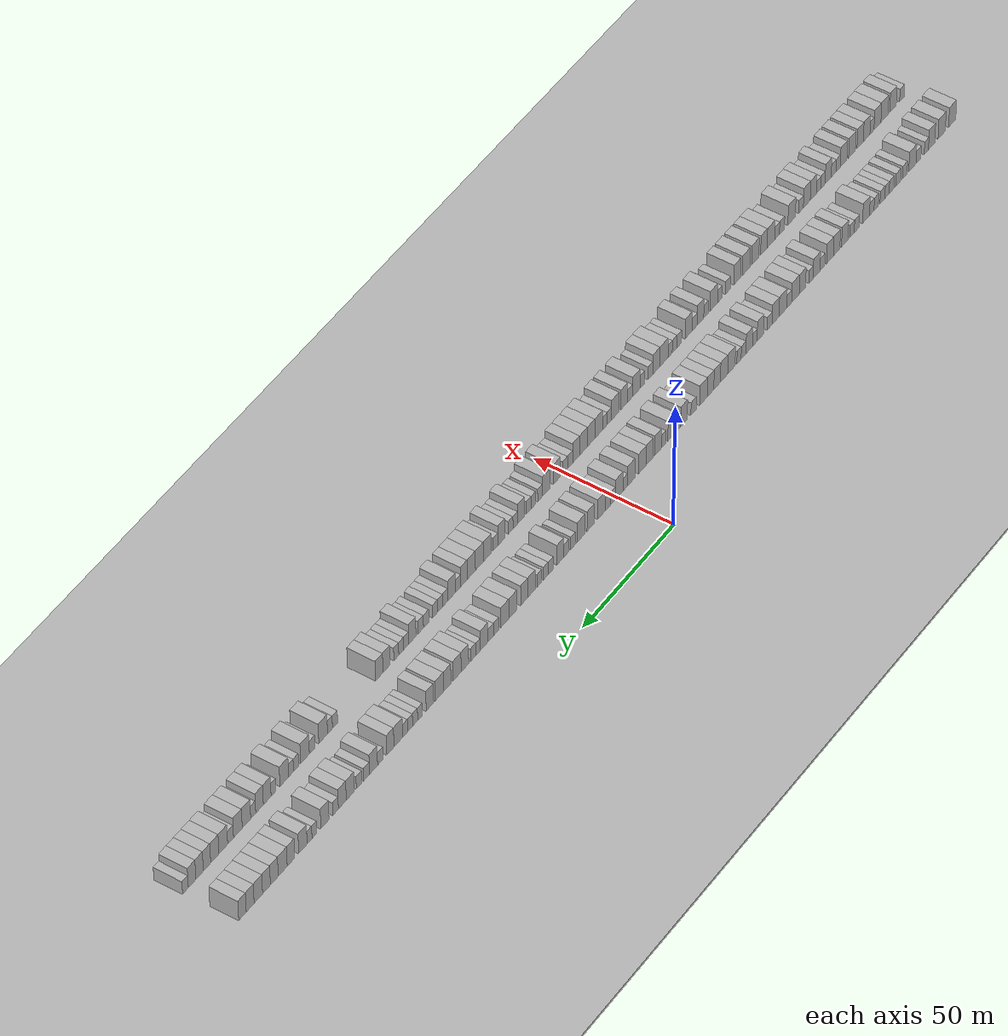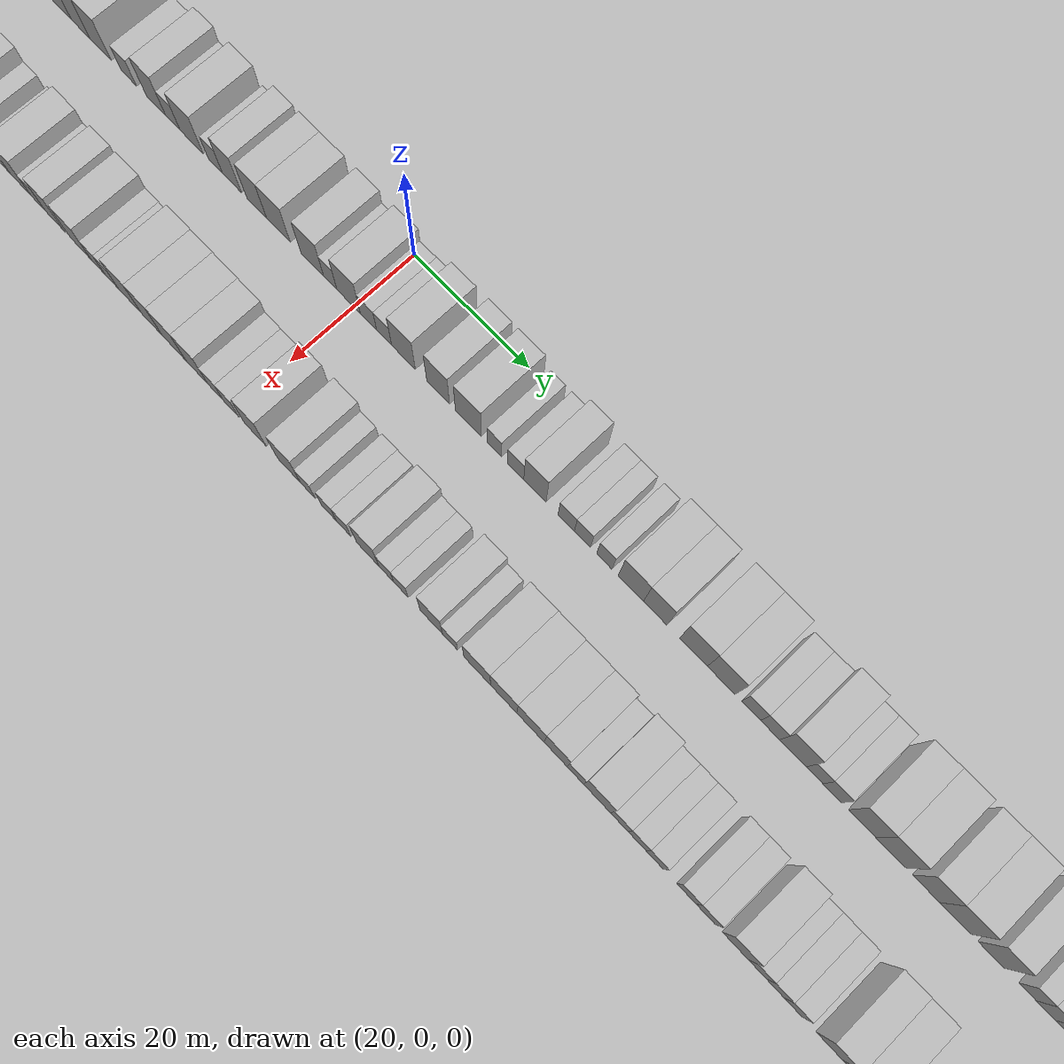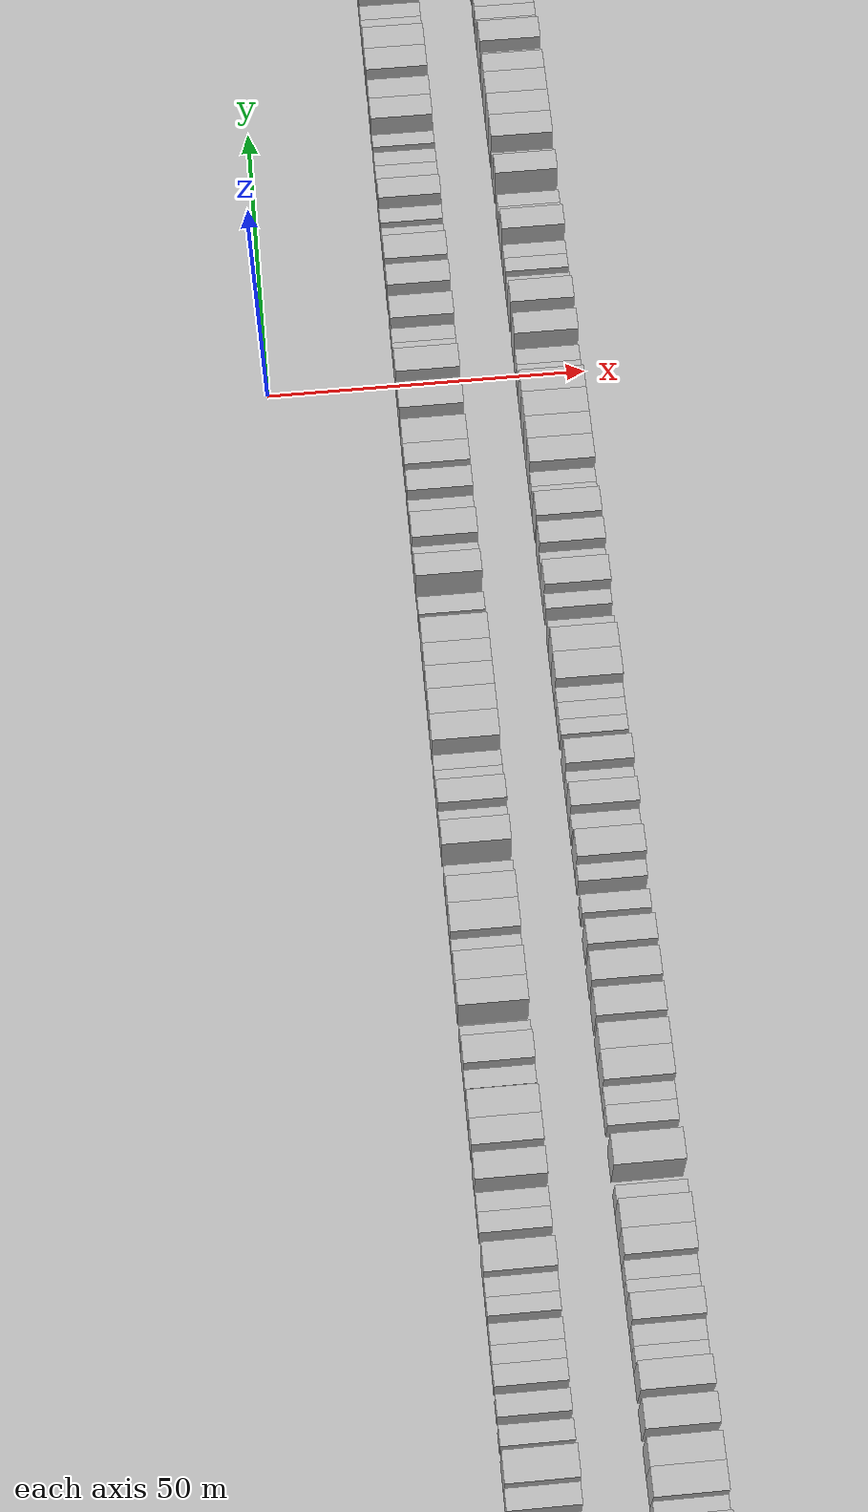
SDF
<?xml version="1.0" encoding="utf-8"?>

<sdf version="1.6">

   <world name="default">

      <gui fullscreen="0">

         <camera name="user_camera">

            <pose>-15 0 4.57585 0 0 0</pose>

            <view_controller>orbit</view_controller>

         </camera>

      </gui>

      <scene>

         <sky>

           <clouds>

             <speed>12</speed>

           </clouds>

         </sky>

         <ambient>0.4 0.4 0.4 1</ambient>

         <background>0.7 0.7 0.7 1</background>

         <shadows>1</shadows>

      </scene>

      <gravity>0 0 -9.8066</gravity>

      <magnetic_field>6e-06 2.3e-05 -4.2e-05</magnetic_field>

      <physics default="0" name="default_physics" type="ode">

         <ode>

            <solver>

               <type>quick</type>

               <iters>10</iters>

               <sor>1.0</sor>

               <use_dynamic_moi_rescaling>0</use_dynamic_moi_rescaling>

            </solver>

            <constraints>

               <cfm>0</cfm>

               <erp>0.2</erp>

               <contact_max_correcting_vel>100</contact_max_correcting_vel>

               <contact_surface_layer>0.001</contact_surface_layer>

            </constraints>

         </ode>

         <max_step_size>0.004</max_step_size>

         <real_time_factor>1</real_time_factor>

         <real_time_update_rate>250</real_time_update_rate>

      </physics>

      <light name="sun" type="directional">

         <cast_shadows>1</cast_shadows>

         <pose>0 0 10 0 0 0</pose>

         <diffuse>0.8 0.8 0.8 1</diffuse>

         <specular>0.2 0.2 0.2 1</specular>

         <attenuation>

            <range>1000</range>

            <constant>0.9</constant>

            <linear>0.01</linear>

            <quadratic>0.001</quadratic>

         </attenuation>

         <direction>-0.5 0.1 -0.9</direction>

      </light>

      <include>

         <name>ground_plane_1</name>

         <uri>model://HANNAS_ground_plane</uri>

         <pose>0 0 0  0 0 0</pose>

      </include>

      <include>

         <name>ground_plane_2</name>

         <uri>model://HANNAS_ground_plane</uri>

         <pose>100 0 0  0 0 0</pose>

      </include>

      <model name="building_1">

         <static>1</static>

         <pose frame="">25.0000 -193.8158 0 0.000000 0.000000 0.000000</pose>

         <link name="link">

            <pose frame="">0 0 4.50 0 0 0</pose>

            <collision name="collision">

               <geometry>

                  <box>

                     <size>10.0000 4.3684 9.0000</size>

                  </box>

               </geometry>

               <max_contacts>10</max_contacts>

               <surface>

                  <contact>

                     <ode/>

                  </contact>

                  <bounce/>

                  <friction>

                     <torsional>

                        <ode/>

                     </torsional>

                     <ode/>

                  </friction>

               </surface>

            </collision>

            <visual name="visual">

               <cast_shadows>0</cast_shadows>

               <geometry>

                  <box>

                     <size>10.0000 4.3684 9.0000</size>

                  </box>

               </geometry>

               <material>

                  <script>

                     <uri>model://HANNAS_wall/materials/scripts</uri>

                     <uri>model://HANNAS_wall/materials/textures</uri>

                     <name>vrc/HANNAS_wall</name>

                  </script>

               </material>

            </visual>

            <self_collide>0</self_collide>

            <enable_wind>0</enable_wind>

            <kinematic>0</kinematic>

         </link>

      </model>

      <model name="building_2">

         <static>1</static>

         <pose frame="">25.0000 -187.4252 0 0.000000 0.000000 0.000000</pose>

         <link name="link">

            <pose frame="">0 0 4.50 0 0 0</pose>

            <collision name="collision">

               <geometry>

                  <box>

                     <size>10.0000 4.4127 9.0000</size>

                  </box>

               </geometry>

               <max_contacts>10</max_contacts>

               <surface>

                  <contact>

                     <ode/>

                  </contact>

                  <bounce/>

                  <friction>

                     <torsional>

                        <ode/>

                     </torsional>

                     <ode/>

                  </friction>

               </surface>

            </collision>

            <visual name="visual">

               <cast_shadows>0</cast_shadows>

               <geometry>

                  <box>

                     <size>10.0000 4.4127 9.0000</size>

                  </box>

               </geometry>

               <material>

                  <script>

                     <uri>model://HANNAS_wall/materials/scripts</uri>

                     <uri>model://HANNAS_wall/materials/textures</uri>

                     <name>vrc/HANNAS_wall</name>

                  </script>

               </material>

            </visual>

            <self_collide>0</self_collide>

            <enable_wind>0</enable_wind>

            <kinematic>0</kinematic>

         </link>

      </model>

      <model name="building_3">

         <static>1</static>

         <pose frame="">25.0000 -181.3065 0 0.000000 0.000000 0.000000</pose>

         <link name="link">

            <pose frame="">0 0 4.50 0 0 0</pose>

            <collision name="collision">

               <geometry>

                  <box>

                     <size>10.0000 3.8246 9.0000</size>

                  </box>

               </geometry>

               <max_contacts>10</max_contacts>

               <surface>

                  <contact>

                     <ode/>

                  </contact>

                  <bounce/>

                  <friction>

                     <torsional>

                        <ode/>

                     </torsional>

                     <ode/>

                  </friction>

               </surface>

            </collision>

            <visual name="visual">

               <cast_shadows>0</cast_shadows>

               <geometry>

                  <box>

                     <size>10.0000 3.8246 9.0000</size>

                  </box>

               </geometry>

               <material>

                  <script>

                     <uri>model://HANNAS_wall/materials/scripts</uri>

                     <uri>model://HANNAS_wall/materials/textures</uri>

                     <name>vrc/HANNAS_wall</name>

                  </script>

               </material>

            </visual>

            <self_collide>0</self_collide>

            <enable_wind>0</enable_wind>

            <kinematic>0</kinematic>

         </link>

      </model>

      <model name="building_4">

         <static>1</static>

         <pose frame="">25.0000 -178.1168 0 0.000000 0.000000 0.000000</pose>

         <link name="link">

            <pose frame="">0 0 3.00 0 0 0</pose>

            <collision name="collision">

               <geometry>

                  <box>

                     <size>10.0000 2.5548 6.0000</size>

                  </box>

               </geometry>

               <max_contacts>10</max_contacts>

               <surface>

                  <contact>

                     <ode/>

                  </contact>

                  <bounce/>

                  <friction>

                     <torsional>

                        <ode/>

                     </torsional>

                     <ode/>

                  </friction>

               </surface>

            </collision>

            <visual name="visual">

               <cast_shadows>0</cast_shadows>

               <geometry>

                  <box>

                     <size>10.0000 2.5548 6.0000</size>

                  </box>

               </geometry>

               <material>

                  <script>

                     <uri>model://HANNAS_wall/materials/scripts</uri>

                     <uri>model://HANNAS_wall/materials/textures</uri>

                     <name>vrc/HANNAS_wall</name>

                  </script>

               </material>

            </visual>

            <self_collide>0</self_collide>

            <enable_wind>0</enable_wind>

            <kinematic>0</kinematic>

         </link>

      </model>

      <model name="building_5">

         <static>1</static>

         <pose frame="">25.0000 -173.3668 0 0.000000 0.000000 0.000000</pose>

         <link name="link">

            <pose frame="">0 0 3.00 0 0 0</pose>

            <collision name="collision">

               <geometry>

                  <box>

                     <size>10.0000 2.9451 6.0000</size>

                  </box>

               </geometry>

               <max_contacts>10</max_contacts>

               <surface>

                  <contact>

                     <ode/>

                  </contact>

                  <bounce/>

                  <friction>

                     <torsional>

                        <ode/>

                     </torsional>

                     <ode/>

                  </friction>

               </surface>

            </collision>

            <visual name="visual">

               <cast_shadows>0</cast_shadows>

               <geometry>

                  <box>

                     <size>10.0000 2.9451 6.0000</size>

                  </box>

               </geometry>

               <material>

                  <script>

                     <uri>model://HANNAS_wall/materials/scripts</uri>

                     <uri>model://HANNAS_wall/materials/textures</uri>

                     <name>vrc/HANNAS_wall</name>

                  </script>

               </material>

            </visual>

            <self_collide>0</self_collide>

            <enable_wind>0</enable_wind>

            <kinematic>0</kinematic>

         </link>

      </model>

      <model name="building_6">

         <static>1</static>

         <pose frame="">25.0000 -169.7110 0 0.000000 0.000000 0.000000</pose>

         <link name="link">

            <pose frame="">0 0 4.50 0 0 0</pose>

            <collision name="collision">

               <geometry>

                  <box>

                     <size>10.0000 4.3665 9.0000</size>

                  </box>

               </geometry>

               <max_contacts>10</max_contacts>

               <surface>

                  <contact>

                     <ode/>

                  </contact>

                  <bounce/>

                  <friction>

                     <torsional>

                        <ode/>

                     </torsional>

                     <ode/>

                  </friction>

               </surface>

            </collision>

            <visual name="visual">

               <cast_shadows>0</cast_shadows>

               <geometry>

                  <box>

                     <size>10.0000 4.3665 9.0000</size>

                  </box>

               </geometry>

               <material>

                  <script>

                     <uri>model://HANNAS_wall/materials/scripts</uri>

                     <uri>model://HANNAS_wall/materials/textures</uri>

                     <name>vrc/HANNAS_wall</name>

                  </script>

               </material>

            </visual>

            <self_collide>0</self_collide>

            <enable_wind>0</enable_wind>

            <kinematic>0</kinematic>

         </link>

      </model>

      <model name="building_7">

         <static>1</static>

         <pose frame="">25.0000 -165.1141 0 0.000000 0.000000 0.000000</pose>

         <link name="link">

            <pose frame="">0 0 3.00 0 0 0</pose>

            <collision name="collision">

               <geometry>

                  <box>

                     <size>10.0000 2.8274 6.0000</size>

                  </box>

               </geometry>

               <max_contacts>10</max_contacts>

               <surface>

                  <contact>

                     <ode/>

                  </contact>

                  <bounce/>

                  <friction>

                     <torsional>

                        <ode/>

                     </torsional>

                     <ode/>

                  </friction>

               </surface>

            </collision>

            <visual name="visual">

               <cast_shadows>0</cast_shadows>

               <geometry>

                  <box>

                     <size>10.0000 2.8274 6.0000</size>

                  </box>

               </geometry>

               <material>

                  <script>

                     <uri>model://HANNAS_wall/materials/scripts</uri>

                     <uri>model://HANNAS_wall/materials/textures</uri>

                     <name>vrc/HANNAS_wall</name>

                  </script>

               </material>

            </visual>

            <self_collide>0</self_collide>

            <enable_wind>0</enable_wind>

            <kinematic>0</kinematic>

         </link>

      </model>

      <model name="building_8">

         <static>1</static>

         <pose frame="">25.0000 -161.2014 0 0.000000 0.000000 0.000000</pose>

         <link name="link">

            <pose frame="">0 0 3.00 0 0 0</pose>

            <collision name="collision">

               <geometry>

                  <box>

                     <size>10.0000 2.9981 6.0000</size>

                  </box>

               </geometry>

               <max_contacts>10</max_contacts>

               <surface>

                  <contact>

                     <ode/>

                  </contact>

                  <bounce/>

                  <friction>

                     <torsional>

                        <ode/>

                     </torsional>

                     <ode/>

                  </friction>

               </surface>

            </collision>

            <visual name="visual">

               <cast_shadows>0</cast_shadows>

               <geometry>

                  <box>

                     <size>10.0000 2.9981 6.0000</size>

                  </box>

               </geometry>

               <material>

                  <script>

                     <uri>model://HANNAS_wall/materials/scripts</uri>

                     <uri>model://HANNAS_wall/materials/textures</uri>

                     <name>vrc/HANNAS_wall</name>

                  </script>

               </material>

            </visual>

            <self_collide>0</self_collide>

            <enable_wind>0</enable_wind>

            <kinematic>0</kinematic>

         </link>

      </model>

      <model name="building_9">

         <static>1</static>

         <pose frame="">25.0000 -157.2229 0 0.000000 0.000000 0.000000</pose>

         <link name="link">

            <pose frame="">0 0 3.00 0 0 0</pose>

            <collision name="collision">

               <geometry>

                  <box>

                     <size>10.0000 2.9589 6.0000</size>

                  </box>

               </geometry>

               <max_contacts>10</max_contacts>

               <surface>

                  <contact>

                     <ode/>

                  </contact>

                  <bounce/>

                  <friction>

                     <torsional>

                        <ode/>

                     </torsional>

                     <ode/>

                  </friction>

               </surface>

            </collision>

            <visual name="visual">

               <cast_shadows>0</cast_shadows>

               <geometry>

                  <box>

                     <size>10.0000 2.9589 6.0000</size>

                  </box>

               </geometry>

               <material>

                  <script>

                     <uri>model://HANNAS_wall/materials/scripts</uri>

                     <uri>model://HANNAS_wall/materials/textures</uri>

                     <name>vrc/HANNAS_wall</name>

                  </script>

               </material>

            </visual>

            <self_collide>0</self_collide>

            <enable_wind>0</enable_wind>

            <kinematic>0</kinematic>

         </link>

      </model>

      <model name="building_10">

         <static>1</static>

         <pose frame="">25.0000 -154.4646 0 0.000000 0.000000 0.000000</pose>

         <link name="link">

            <pose frame="">0 0 3.00 0 0 0</pose>

            <collision name="collision">

               <geometry>

                  <box>

                     <size>10.0000 2.5576 6.0000</size>

                  </box>

               </geometry>

               <max_contacts>10</max_contacts>

               <surface>

                  <contact>

                     <ode/>

                  </contact>

                  <bounce/>

                  <friction>

                     <torsional>

                        <ode/>

                     </torsional>

                     <ode/>

                  </friction>

               </surface>

            </collision>

            <visual name="visual">

               <cast_shadows>0</cast_shadows>

               <geometry>

                  <box>

                     <size>10.0000 2.5576 6.0000</size>

                  </box>

               </geometry>

               <material>

                  <script>

                     <uri>model://HANNAS_wall/materials/scripts</uri>

                     <uri>model://HANNAS_wall/materials/textures</uri>

                     <name>vrc/HANNAS_wall</name>

                  </script>

               </material>

            </visual>

            <self_collide>0</self_collide>

            <enable_wind>0</enable_wind>

            <kinematic>0</kinematic>

         </link>

      </model>

      <model name="building_11">

         <static>1</static>

         <pose frame="">25.0000 -151.7313 0 0.000000 0.000000 0.000000</pose>

         <link name="link">

            <pose frame="">0 0 3.00 0 0 0</pose>

            <collision name="collision">

               <geometry>

                  <box>

                     <size>10.0000 2.9090 6.0000</size>

                  </box>

               </geometry>

               <max_contacts>10</max_contacts>

               <surface>

                  <contact>

                     <ode/>

                  </contact>

                  <bounce/>

                  <friction>

                     <torsional>

                        <ode/>

                     </torsional>

                     <ode/>

                  </friction>

               </surface>

            </collision>

            <visual name="visual">

               <cast_shadows>0</cast_shadows>

               <geometry>

                  <box>

                     <size>10.0000 2.9090 6.0000</size>

                  </box>

               </geometry>

               <material>

                  <script>

                     <uri>model://HANNAS_wall/materials/scripts</uri>

                     <uri>model://HANNAS_wall/materials/textures</uri>

                     <name>vrc/HANNAS_wall</name>

                  </script>

               </material>

            </visual>

            <self_collide>0</self_collide>

            <enable_wind>0</enable_wind>

            <kinematic>0</kinematic>

         </link>

      </model>

      <model name="building_12">

         <static>1</static>

         <pose frame="">25.0000 -148.0010 0 0.000000 0.000000 0.000000</pose>

         <link name="link">

            <pose frame="">0 0 3.00 0 0 0</pose>

            <collision name="collision">

               <geometry>

                  <box>

                     <size>10.0000 2.5517 6.0000</size>

                  </box>

               </geometry>

               <max_contacts>10</max_contacts>

               <surface>

                  <contact>

                     <ode/>

                  </contact>

                  <bounce/>

                  <friction>

                     <torsional>

                        <ode/>

                     </torsional>

                     <ode/>

                  </friction>

               </surface>

            </collision>

            <visual name="visual">

               <cast_shadows>0</cast_shadows>

               <geometry>

                  <box>

                     <size>10.0000 2.5517 6.0000</size>

                  </box>

               </geometry>

               <material>

                  <script>

                     <uri>model://HANNAS_wall/materials/scripts</uri>

                     <uri>model://HANNAS_wall/materials/textures</uri>

                     <name>vrc/HANNAS_wall</name>

                  </script>

               </material>

            </visual>

            <self_collide>0</self_collide>

            <enable_wind>0</enable_wind>

            <kinematic>0</kinematic>

         </link>

      </model>

      <model name="building_13">

         <static>1</static>

         <pose frame="">25.0000 -145.3806 0 0.000000 0.000000 0.000000</pose>

         <link name="link">

            <pose frame="">0 0 3.00 0 0 0</pose>

            <collision name="collision">

               <geometry>

                  <box>

                     <size>10.0000 2.6890 6.0000</size>

                  </box>

               </geometry>

               <max_contacts>10</max_contacts>

               <surface>

                  <contact>

                     <ode/>

                  </contact>

                  <bounce/>

                  <friction>

                     <torsional>

                        <ode/>

                     </torsional>

                     <ode/>

                  </friction>

               </surface>

            </collision>

            <visual name="visual">

               <cast_shadows>0</cast_shadows>

               <geometry>

                  <box>

                     <size>10.0000 2.6890 6.0000</size>

                  </box>

               </geometry>

               <material>

                  <script>

                     <uri>model://HANNAS_wall/materials/scripts</uri>

                     <uri>model://HANNAS_wall/materials/textures</uri>

                     <name>vrc/HANNAS_wall</name>

                  </script>

               </material>

            </visual>

            <self_collide>0</self_collide>

            <enable_wind>0</enable_wind>

            <kinematic>0</kinematic>

         </link>

      </model>

      <model name="building_14">

         <static>1</static>

         <pose frame="">25.0000 -141.9866 0 0.000000 0.000000 0.000000</pose>

         <link name="link">

            <pose frame="">0 0 4.50 0 0 0</pose>

            <collision name="collision">

               <geometry>

                  <box>

                     <size>10.0000 4.0990 9.0000</size>

                  </box>

               </geometry>

               <max_contacts>10</max_contacts>

               <surface>

                  <contact>

                     <ode/>

                  </contact>

                  <bounce/>

                  <friction>

                     <torsional>

                        <ode/>

                     </torsional>

                     <ode/>

                  </friction>

               </surface>

            </collision>

            <visual name="visual">

               <cast_shadows>0</cast_shadows>

               <geometry>

                  <box>

                     <size>10.0000 4.0990 9.0000</size>

                  </box>

               </geometry>

               <material>

                  <script>

                     <uri>model://HANNAS_wall/materials/scripts</uri>

                     <uri>model://HANNAS_wall/materials/textures</uri>

                     <name>vrc/HANNAS_wall</name>

                  </script>

               </material>

            </visual>

            <self_collide>0</self_collide>

            <enable_wind>0</enable_wind>

            <kinematic>0</kinematic>

         </link>

      </model>

      <model name="building_15">

         <static>1</static>

         <pose frame="">25.0000 -136.4802 0 0.000000 0.000000 0.000000</pose>

         <link name="link">

            <pose frame="">0 0 3.00 0 0 0</pose>

            <collision name="collision">

               <geometry>

                  <box>

                     <size>10.0000 2.9137 6.0000</size>

                  </box>

               </geometry>

               <max_contacts>10</max_contacts>

               <surface>

                  <contact>

                     <ode/>

                  </contact>

                  <bounce/>

                  <friction>

                     <torsional>

                        <ode/>

                     </torsional>

                     <ode/>

                  </friction>

               </surface>

            </collision>

            <visual name="visual">

               <cast_shadows>0</cast_shadows>

               <geometry>

                  <box>

                     <size>10.0000 2.9137 6.0000</size>

                  </box>

               </geometry>

               <material>

                  <script>

                     <uri>model://HANNAS_wall/materials/scripts</uri>

                     <uri>model://HANNAS_wall/materials/textures</uri>

                     <name>vrc/HANNAS_wall</name>

                  </script>

               </material>

            </visual>

            <self_collide>0</self_collide>

            <enable_wind>0</enable_wind>

            <kinematic>0</kinematic>

         </link>

      </model>

      <model name="building_16">

         <static>1</static>

         <pose frame="">25.0000 -133.6682 0 0.000000 0.000000 0.000000</pose>

         <link name="link">

            <pose frame="">0 0 3.00 0 0 0</pose>

            <collision name="collision">

               <geometry>

                  <box>

                     <size>10.0000 2.7104 6.0000</size>

                  </box>

               </geometry>

               <max_contacts>10</max_contacts>

               <surface>

                  <contact>

                     <ode/>

                  </contact>

                  <bounce/>

                  <friction>

                     <torsional>

                        <ode/>

                     </torsional>

                     <ode/>

                  </friction>

               </surface>

            </collision>

            <visual name="visual">

               <cast_shadows>0</cast_shadows>

               <geometry>

                  <box>

                     <size>10.0000 2.7104 6.0000</size>

                  </box>

               </geometry>

               <material>

                  <script>

                     <uri>model://HANNAS_wall/materials/scripts</uri>

                     <uri>model://HANNAS_wall/materials/textures</uri>

                     <name>vrc/HANNAS_wall</name>

                  </script>

               </material>

            </visual>

            <self_collide>0</self_collide>

            <enable_wind>0</enable_wind>

            <kinematic>0</kinematic>

         </link>

      </model>

      <model name="building_17">

         <static>1</static>

         <pose frame="">25.0000 -129.4004 0 0.000000 0.000000 0.000000</pose>

         <link name="link">

            <pose frame="">0 0 4.50 0 0 0</pose>

            <collision name="collision">

               <geometry>

                  <box>

                     <size>10.0000 3.8253 9.0000</size>

                  </box>

               </geometry>

               <max_contacts>10</max_contacts>

               <surface>

                  <contact>

                     <ode/>

                  </contact>

                  <bounce/>

                  <friction>

                     <torsional>

                        <ode/>

                     </torsional>

                     <ode/>

                  </friction>

               </surface>

            </collision>

            <visual name="visual">

               <cast_shadows>0</cast_shadows>

               <geometry>

                  <box>

                     <size>10.0000 3.8253 9.0000</size>

                  </box>

               </geometry>

               <material>

                  <script>

                     <uri>model://HANNAS_wall/materials/scripts</uri>

                     <uri>model://HANNAS_wall/materials/textures</uri>

                     <name>vrc/HANNAS_wall</name>

                  </script>

               </material>

            </visual>

            <self_collide>0</self_collide>

            <enable_wind>0</enable_wind>

            <kinematic>0</kinematic>

         </link>

      </model>

      <model name="building_18">

         <static>1</static>

         <pose frame="">25.0000 -124.5874 0 0.000000 0.000000 0.000000</pose>

         <link name="link">

            <pose frame="">0 0 4.50 0 0 0</pose>

            <collision name="collision">

               <geometry>

                  <box>

                     <size>10.0000 3.8006 9.0000</size>

                  </box>

               </geometry>

               <max_contacts>10</max_contacts>

               <surface>

                  <contact>

                     <ode/>

                  </contact>

                  <bounce/>

                  <friction>

                     <torsional>

                        <ode/>

                     </torsional>

                     <ode/>

                  </friction>

               </surface>

            </collision>

            <visual name="visual">

               <cast_shadows>0</cast_shadows>

               <geometry>

                  <box>

                     <size>10.0000 3.8006 9.0000</size>

                  </box>

               </geometry>

               <material>

                  <script>

                     <uri>model://HANNAS_wall/materials/scripts</uri>

                     <uri>model://HANNAS_wall/materials/textures</uri>

                     <name>vrc/HANNAS_wall</name>

                  </script>

               </material>

            </visual>

            <self_collide>0</self_collide>

            <enable_wind>0</enable_wind>

            <kinematic>0</kinematic>

         </link>

      </model>

      <model name="building_19">

         <static>1</static>

         <pose frame="">25.0000 -120.6496 0 0.000000 0.000000 0.000000</pose>

         <link name="link">

            <pose frame="">0 0 4.50 0 0 0</pose>

            <collision name="collision">

               <geometry>

                  <box>

                     <size>10.0000 4.0750 9.0000</size>

                  </box>

               </geometry>

               <max_contacts>10</max_contacts>

               <surface>

                  <contact>

                     <ode/>

                  </contact>

                  <bounce/>

                  <friction>

                     <torsional>

                        <ode/>

                     </torsional>

                     <ode/>

                  </friction>

               </surface>

            </collision>

            <visual name="visual">

               <cast_shadows>0</cast_shadows>

               <geometry>

                  <box>

                     <size>10.0000 4.0750 9.0000</size>

                  </box>

               </geometry>

               <material>

                  <script>

                     <uri>model://HANNAS_wall/materials/scripts</uri>

                     <uri>model://HANNAS_wall/materials/textures</uri>

                     <name>vrc/HANNAS_wall</name>

                  </script>

               </material>

            </visual>

            <self_collide>0</self_collide>

            <enable_wind>0</enable_wind>

            <kinematic>0</kinematic>

         </link>

      </model>

      <model name="building_20">

         <static>1</static>

         <pose frame="">25.0000 -116.2314 0 0.000000 0.000000 0.000000</pose>

         <link name="link">

            <pose frame="">0 0 3.00 0 0 0</pose>

            <collision name="collision">

               <geometry>

                  <box>

                     <size>10.0000 2.7614 6.0000</size>

                  </box>

               </geometry>

               <max_contacts>10</max_contacts>

               <surface>

                  <contact>

                     <ode/>

                  </contact>

                  <bounce/>

                  <friction>

                     <torsional>

                        <ode/>

                     </torsional>

                     <ode/>

                  </friction>

               </surface>

            </collision>

            <visual name="visual">

               <cast_shadows>0</cast_shadows>

               <geometry>

                  <box>

                     <size>10.0000 2.7614 6.0000</size>

                  </box>

               </geometry>

               <material>

                  <script>

                     <uri>model://HANNAS_wall/materials/scripts</uri>

                     <uri>model://HANNAS_wall/materials/textures</uri>

                     <name>vrc/HANNAS_wall</name>

                  </script>

               </material>

            </visual>

            <self_collide>0</self_collide>

            <enable_wind>0</enable_wind>

            <kinematic>0</kinematic>

         </link>

      </model>

      <model name="building_21">

         <static>1</static>

         <pose frame="">25.0000 -112.8315 0 0.000000 0.000000 0.000000</pose>

         <link name="link">

            <pose frame="">0 0 4.50 0 0 0</pose>

            <collision name="collision">

               <geometry>

                  <box>

                     <size>10.0000 4.0385 9.0000</size>

                  </box>

               </geometry>

               <max_contacts>10</max_contacts>

               <surface>

                  <contact>

                     <ode/>

                  </contact>

                  <bounce/>

                  <friction>

                     <torsional>

                        <ode/>

                     </torsional>

                     <ode/>

                  </friction>

               </surface>

            </collision>

            <visual name="visual">

               <cast_shadows>0</cast_shadows>

               <geometry>

                  <box>

                     <size>10.0000 4.0385 9.0000</size>

                  </box>

               </geometry>

               <material>

                  <script>

                     <uri>model://HANNAS_wall/materials/scripts</uri>

                     <uri>model://HANNAS_wall/materials/textures</uri>

                     <name>vrc/HANNAS_wall</name>

                  </script>

               </material>

            </visual>

            <self_collide>0</self_collide>

            <enable_wind>0</enable_wind>

            <kinematic>0</kinematic>

         </link>

      </model>

      <model name="building_22">

         <static>1</static>

         <pose frame="">25.0000 -109.6122 0 0.000000 0.000000 0.000000</pose>

         <link name="link">

            <pose frame="">0 0 3.00 0 0 0</pose>

            <collision name="collision">

               <geometry>

                  <box>

                     <size>10.0000 2.4001 6.0000</size>

                  </box>

               </geometry>

               <max_contacts>10</max_contacts>

               <surface>

                  <contact>

                     <ode/>

                  </contact>

                  <bounce/>

                  <friction>

                     <torsional>

                        <ode/>

                     </torsional>

                     <ode/>

                  </friction>

               </surface>

            </collision>

            <visual name="visual">

               <cast_shadows>0</cast_shadows>

               <geometry>

                  <box>

                     <size>10.0000 2.4001 6.0000</size>

                  </box>

               </geometry>

               <material>

                  <script>

                     <uri>model://HANNAS_wall/materials/scripts</uri>

                     <uri>model://HANNAS_wall/materials/textures</uri>

                     <name>vrc/HANNAS_wall</name>

                  </script>

               </material>

            </visual>

            <self_collide>0</self_collide>

            <enable_wind>0</enable_wind>

            <kinematic>0</kinematic>

         </link>

      </model>

      <model name="building_23">

         <static>1</static>

         <pose frame="">25.0000 -104.5498 0 0.000000 0.000000 0.000000</pose>

         <link name="link">

            <pose frame="">0 0 4.50 0 0 0</pose>

            <collision name="collision">

               <geometry>

                  <box>

                     <size>10.0000 3.7247 9.0000</size>

                  </box>

               </geometry>

               <max_contacts>10</max_contacts>

               <surface>

                  <contact>

                     <ode/>

                  </contact>

                  <bounce/>

                  <friction>

                     <torsional>

                        <ode/>

                     </torsional>

                     <ode/>

                  </friction>

               </surface>

            </collision>

            <visual name="visual">

               <cast_shadows>0</cast_shadows>

               <geometry>

                  <box>

                     <size>10.0000 3.7247 9.0000</size>

                  </box>

               </geometry>

               <material>

                  <script>

                     <uri>model://HANNAS_wall/materials/scripts</uri>

                     <uri>model://HANNAS_wall/materials/textures</uri>

                     <name>vrc/HANNAS_wall</name>

                  </script>

               </material>

            </visual>

            <self_collide>0</self_collide>

            <enable_wind>0</enable_wind>

            <kinematic>0</kinematic>

         </link>

      </model>

      <model name="building_24">

         <static>1</static>

         <pose frame="">25.0000 -100.5147 0 0.000000 0.000000 0.000000</pose>

         <link name="link">

            <pose frame="">0 0 4.50 0 0 0</pose>

            <collision name="collision">

               <geometry>

                  <box>

                     <size>10.0000 4.3453 9.0000</size>

                  </box>

               </geometry>

               <max_contacts>10</max_contacts>

               <surface>

                  <contact>

                     <ode/>

                  </contact>

                  <bounce/>

                  <friction>

                     <torsional>

                        <ode/>

                     </torsional>

                     <ode/>

                  </friction>

               </surface>

            </collision>

            <visual name="visual">

               <cast_shadows>0</cast_shadows>

               <geometry>

                  <box>

                     <size>10.0000 4.3453 9.0000</size>

                  </box>

               </geometry>

               <material>

                  <script>

                     <uri>model://HANNAS_wall/materials/scripts</uri>

                     <uri>model://HANNAS_wall/materials/textures</uri>

                     <name>vrc/HANNAS_wall</name>

                  </script>

               </material>

            </visual>

            <self_collide>0</self_collide>

            <enable_wind>0</enable_wind>

            <kinematic>0</kinematic>

         </link>

      </model>

      <model name="building_25">

         <static>1</static>

         <pose frame="">25.0000 -96.9032 0 0.000000 0.000000 0.000000</pose>

         <link name="link">

            <pose frame="">0 0 3.00 0 0 0</pose>

            <collision name="collision">

               <geometry>

                  <box>

                     <size>10.0000 2.8777 6.0000</size>

                  </box>

               </geometry>

               <max_contacts>10</max_contacts>

               <surface>

                  <contact>

                     <ode/>

                  </contact>

                  <bounce/>

                  <friction>

                     <torsional>

                        <ode/>

                     </torsional>

                     <ode/>

                  </friction>

               </surface>

            </collision>

            <visual name="visual">

               <cast_shadows>0</cast_shadows>

               <geometry>

                  <box>

                     <size>10.0000 2.8777 6.0000</size>

                  </box>

               </geometry>

               <material>

                  <script>

                     <uri>model://HANNAS_wall/materials/scripts</uri>

                     <uri>model://HANNAS_wall/materials/textures</uri>

                     <name>vrc/HANNAS_wall</name>

                  </script>

               </material>

            </visual>

            <self_collide>0</self_collide>

            <enable_wind>0</enable_wind>

            <kinematic>0</kinematic>

         </link>

      </model>

      <model name="building_26">

         <static>1</static>

         <pose frame="">25.0000 -93.2507 0 0.000000 0.000000 0.000000</pose>

         <link name="link">

            <pose frame="">0 0 4.50 0 0 0</pose>

            <collision name="collision">

               <geometry>

                  <box>

                     <size>10.0000 4.4274 9.0000</size>

                  </box>

               </geometry>

               <max_contacts>10</max_contacts>

               <surface>

                  <contact>

                     <ode/>

                  </contact>

                  <bounce/>

                  <friction>

                     <torsional>

                        <ode/>

                     </torsional>

                     <ode/>

                  </friction>

               </surface>

            </collision>

            <visual name="visual">

               <cast_shadows>0</cast_shadows>

               <geometry>

                  <box>

                     <size>10.0000 4.4274 9.0000</size>

                  </box>

               </geometry>

               <material>

                  <script>

                     <uri>model://HANNAS_wall/materials/scripts</uri>

                     <uri>model://HANNAS_wall/materials/textures</uri>

                     <name>vrc/HANNAS_wall</name>

                  </script>

               </material>

            </visual>

            <self_collide>0</self_collide>

            <enable_wind>0</enable_wind>

            <kinematic>0</kinematic>

         </link>

      </model>

      <model name="building_27">

         <static>1</static>

         <pose frame="">25.0000 -89.0107 0 0.000000 0.000000 0.000000</pose>

         <link name="link">

            <pose frame="">0 0 4.50 0 0 0</pose>

            <collision name="collision">

               <geometry>

                  <box>

                     <size>10.0000 4.0526 9.0000</size>

                  </box>

               </geometry>

               <max_contacts>10</max_contacts>

               <surface>

                  <contact>

                     <ode/>

                  </contact>

                  <bounce/>

                  <friction>

                     <torsional>

                        <ode/>

                     </torsional>

                     <ode/>

                  </friction>

               </surface>

            </collision>

            <visual name="visual">

               <cast_shadows>0</cast_shadows>

               <geometry>

                  <box>

                     <size>10.0000 4.0526 9.0000</size>

                  </box>

               </geometry>

               <material>

                  <script>

                     <uri>model://HANNAS_wall/materials/scripts</uri>

                     <uri>model://HANNAS_wall/materials/textures</uri>

                     <name>vrc/HANNAS_wall</name>

                  </script>

               </material>

            </visual>

            <self_collide>0</self_collide>

            <enable_wind>0</enable_wind>

            <kinematic>0</kinematic>

         </link>

      </model>

      <model name="building_28">

         <static>1</static>

         <pose frame="">25.0000 -85.5695 0 0.000000 0.000000 0.000000</pose>

         <link name="link">

            <pose frame="">0 0 3.00 0 0 0</pose>

            <collision name="collision">

               <geometry>

                  <box>

                     <size>10.0000 2.8299 6.0000</size>

                  </box>

               </geometry>

               <max_contacts>10</max_contacts>

               <surface>

                  <contact>

                     <ode/>

                  </contact>

                  <bounce/>

                  <friction>

                     <torsional>

                        <ode/>

                     </torsional>

                     <ode/>

                  </friction>

               </surface>

            </collision>

            <visual name="visual">

               <cast_shadows>0</cast_shadows>

               <geometry>

                  <box>

                     <size>10.0000 2.8299 6.0000</size>

                  </box>

               </geometry>

               <material>

                  <script>

                     <uri>model://HANNAS_wall/materials/scripts</uri>

                     <uri>model://HANNAS_wall/materials/textures</uri>

                     <name>vrc/HANNAS_wall</name>

                  </script>

               </material>

            </visual>

            <self_collide>0</self_collide>

            <enable_wind>0</enable_wind>

            <kinematic>0</kinematic>

         </link>

      </model>

      <model name="building_29">

         <static>1</static>

         <pose frame="">25.0000 -80.2502 0 0.000000 0.000000 0.000000</pose>

         <link name="link">

            <pose frame="">0 0 4.50 0 0 0</pose>

            <collision name="collision">

               <geometry>

                  <box>

                     <size>10.0000 3.8086 9.0000</size>

                  </box>

               </geometry>

               <max_contacts>10</max_contacts>

               <surface>

                  <contact>

                     <ode/>

                  </contact>

                  <bounce/>

                  <friction>

                     <torsional>

                        <ode/>

                     </torsional>

                     <ode/>

                  </friction>

               </surface>

            </collision>

            <visual name="visual">

               <cast_shadows>0</cast_shadows>

               <geometry>

                  <box>

                     <size>10.0000 3.8086 9.0000</size>

                  </box>

               </geometry>

               <material>

                  <script>

                     <uri>model://HANNAS_wall/materials/scripts</uri>

                     <uri>model://HANNAS_wall/materials/textures</uri>

                     <name>vrc/HANNAS_wall</name>

                  </script>

               </material>

            </visual>

            <self_collide>0</self_collide>

            <enable_wind>0</enable_wind>

            <kinematic>0</kinematic>

         </link>

      </model>

      <model name="building_30">

         <static>1</static>

         <pose frame="">25.0000 -77.0159 0 0.000000 0.000000 0.000000</pose>

         <link name="link">

            <pose frame="">0 0 3.00 0 0 0</pose>

            <collision name="collision">

               <geometry>

                  <box>

                     <size>10.0000 2.6602 6.0000</size>

                  </box>

               </geometry>

               <max_contacts>10</max_contacts>

               <surface>

                  <contact>

                     <ode/>

                  </contact>

                  <bounce/>

                  <friction>

                     <torsional>

                        <ode/>

                     </torsional>

                     <ode/>

                  </friction>

               </surface>

            </collision>

            <visual name="visual">

               <cast_shadows>0</cast_shadows>

               <geometry>

                  <box>

                     <size>10.0000 2.6602 6.0000</size>

                  </box>

               </geometry>

               <material>

                  <script>

                     <uri>model://HANNAS_wall/materials/scripts</uri>

                     <uri>model://HANNAS_wall/materials/textures</uri>

                     <name>vrc/HANNAS_wall</name>

                  </script>

               </material>

            </visual>

            <self_collide>0</self_collide>

            <enable_wind>0</enable_wind>

            <kinematic>0</kinematic>

         </link>

      </model>

      <model name="building_31">

         <static>1</static>

         <pose frame="">25.0000 -73.8317 0 0.000000 0.000000 0.000000</pose>

         <link name="link">

            <pose frame="">0 0 4.50 0 0 0</pose>

            <collision name="collision">

               <geometry>

                  <box>

                     <size>10.0000 3.7082 9.0000</size>

                  </box>

               </geometry>

               <max_contacts>10</max_contacts>

               <surface>

                  <contact>

                     <ode/>

                  </contact>

                  <bounce/>

                  <friction>

                     <torsional>

                        <ode/>

                     </torsional>

                     <ode/>

                  </friction>

               </surface>

            </collision>

            <visual name="visual">

               <cast_shadows>0</cast_shadows>

               <geometry>

                  <box>

                     <size>10.0000 3.7082 9.0000</size>

                  </box>

               </geometry>

               <material>

                  <script>

                     <uri>model://HANNAS_wall/materials/scripts</uri>

                     <uri>model://HANNAS_wall/materials/textures</uri>

                     <name>vrc/HANNAS_wall</name>

                  </script>

               </material>

            </visual>

            <self_collide>0</self_collide>

            <enable_wind>0</enable_wind>

            <kinematic>0</kinematic>

         </link>

      </model>

      <model name="building_32">

         <static>1</static>

         <pose frame="">25.0000 -70.5869 0 0.000000 0.000000 0.000000</pose>

         <link name="link">

            <pose frame="">0 0 3.00 0 0 0</pose>

            <collision name="collision">

               <geometry>

                  <box>

                     <size>10.0000 2.7813 6.0000</size>

                  </box>

               </geometry>

               <max_contacts>10</max_contacts>

               <surface>

                  <contact>

                     <ode/>

                  </contact>

                  <bounce/>

                  <friction>

                     <torsional>

                        <ode/>

                     </torsional>

                     <ode/>

                  </friction>

               </surface>

            </collision>

            <visual name="visual">

               <cast_shadows>0</cast_shadows>

               <geometry>

                  <box>

                     <size>10.0000 2.7813 6.0000</size>

                  </box>

               </geometry>

               <material>

                  <script>

                     <uri>model://HANNAS_wall/materials/scripts</uri>

                     <uri>model://HANNAS_wall/materials/textures</uri>

                     <name>vrc/HANNAS_wall</name>

                  </script>

               </material>

            </visual>

            <self_collide>0</self_collide>

            <enable_wind>0</enable_wind>

            <kinematic>0</kinematic>

         </link>

      </model>

      <model name="building_33">

         <static>1</static>

         <pose frame="">25.0000 -67.9731 0 0.000000 0.000000 0.000000</pose>

         <link name="link">

            <pose frame="">0 0 3.00 0 0 0</pose>

            <collision name="collision">

               <geometry>

                  <box>

                     <size>10.0000 2.4463 6.0000</size>

                  </box>

               </geometry>

               <max_contacts>10</max_contacts>

               <surface>

                  <contact>

                     <ode/>

                  </contact>

                  <bounce/>

                  <friction>

                     <torsional>

                        <ode/>

                     </torsional>

                     <ode/>

                  </friction>

               </surface>

            </collision>

            <visual name="visual">

               <cast_shadows>0</cast_shadows>

               <geometry>

                  <box>

                     <size>10.0000 2.4463 6.0000</size>

                  </box>

               </geometry>

               <material>

                  <script>

                     <uri>model://HANNAS_wall/materials/scripts</uri>

                     <uri>model://HANNAS_wall/materials/textures</uri>

                     <name>vrc/HANNAS_wall</name>

                  </script>

               </material>

            </visual>

            <self_collide>0</self_collide>

            <enable_wind>0</enable_wind>

            <kinematic>0</kinematic>

         </link>

      </model>

      <model name="building_34">

         <static>1</static>

         <pose frame="">25.0000 -63.6120 0 0.000000 0.000000 0.000000</pose>

         <link name="link">

            <pose frame="">0 0 4.50 0 0 0</pose>

            <collision name="collision">

               <geometry>

                  <box>

                     <size>10.0000 4.2760 9.0000</size>

                  </box>

               </geometry>

               <max_contacts>10</max_contacts>

               <surface>

                  <contact>

                     <ode/>

                  </contact>

                  <bounce/>

                  <friction>

                     <torsional>

                        <ode/>

                     </torsional>

                     <ode/>

                  </friction>

               </surface>

            </collision>

            <visual name="visual">

               <cast_shadows>0</cast_shadows>

               <geometry>

                  <box>

                     <size>10.0000 4.2760 9.0000</size>

                  </box>

               </geometry>

               <material>

                  <script>

                     <uri>model://HANNAS_wall/materials/scripts</uri>

                     <uri>model://HANNAS_wall/materials/textures</uri>

                     <name>vrc/HANNAS_wall</name>

                  </script>

               </material>

            </visual>

            <self_collide>0</self_collide>

            <enable_wind>0</enable_wind>

            <kinematic>0</kinematic>

         </link>

      </model>

      <model name="building_35">

         <static>1</static>

         <pose frame="">25.0000 -59.4427 0 0.000000 0.000000 0.000000</pose>

         <link name="link">

            <pose frame="">0 0 4.50 0 0 0</pose>

            <collision name="collision">

               <geometry>

                  <box>

                     <size>10.0000 4.0625 9.0000</size>

                  </box>

               </geometry>

               <max_contacts>10</max_contacts>

               <surface>

                  <contact>

                     <ode/>

                  </contact>

                  <bounce/>

                  <friction>

                     <torsional>

                        <ode/>

                     </torsional>

                     <ode/>

                  </friction>

               </surface>

            </collision>

            <visual name="visual">

               <cast_shadows>0</cast_shadows>

               <geometry>

                  <box>

                     <size>10.0000 4.0625 9.0000</size>

                  </box>

               </geometry>

               <material>

                  <script>

                     <uri>model://HANNAS_wall/materials/scripts</uri>

                     <uri>model://HANNAS_wall/materials/textures</uri>

                     <name>vrc/HANNAS_wall</name>

                  </script>

               </material>

            </visual>

            <self_collide>0</self_collide>

            <enable_wind>0</enable_wind>

            <kinematic>0</kinematic>

         </link>

      </model>

      <model name="building_36">

         <static>1</static>

         <pose frame="">25.0000 -55.5194 0 0.000000 0.000000 0.000000</pose>

         <link name="link">

            <pose frame="">0 0 4.50 0 0 0</pose>

            <collision name="collision">

               <geometry>

                  <box>

                     <size>10.0000 3.7842 9.0000</size>

                  </box>

               </geometry>

               <max_contacts>10</max_contacts>

               <surface>

                  <contact>

                     <ode/>

                  </contact>

                  <bounce/>

                  <friction>

                     <torsional>

                        <ode/>

                     </torsional>

                     <ode/>

                  </friction>

               </surface>

            </collision>

            <visual name="visual">

               <cast_shadows>0</cast_shadows>

               <geometry>

                  <box>

                     <size>10.0000 3.7842 9.0000</size>

                  </box>

               </geometry>

               <material>

                  <script>

                     <uri>model://HANNAS_wall/materials/scripts</uri>

                     <uri>model://HANNAS_wall/materials/textures</uri>

                     <name>vrc/HANNAS_wall</name>

                  </script>

               </material>

            </visual>

            <self_collide>0</self_collide>

            <enable_wind>0</enable_wind>

            <kinematic>0</kinematic>

         </link>

      </model>

      <model name="building_37">

         <static>1</static>

         <pose frame="">25.0000 -51.7592 0 0.000000 0.000000 0.000000</pose>

         <link name="link">

            <pose frame="">0 0 4.50 0 0 0</pose>

            <collision name="collision">

               <geometry>

                  <box>

                     <size>10.0000 3.7362 9.0000</size>

                  </box>

               </geometry>

               <max_contacts>10</max_contacts>

               <surface>

                  <contact>

                     <ode/>

                  </contact>

                  <bounce/>

                  <friction>

                     <torsional>

                        <ode/>

                     </torsional>

                     <ode/>

                  </friction>

               </surface>

            </collision>

            <visual name="visual">

               <cast_shadows>0</cast_shadows>

               <geometry>

                  <box>

                     <size>10.0000 3.7362 9.0000</size>

                  </box>

               </geometry>

               <material>

                  <script>

                     <uri>model://HANNAS_wall/materials/scripts</uri>

                     <uri>model://HANNAS_wall/materials/textures</uri>

                     <name>vrc/HANNAS_wall</name>

                  </script>

               </material>

            </visual>

            <self_collide>0</self_collide>

            <enable_wind>0</enable_wind>

            <kinematic>0</kinematic>

         </link>

      </model>

      <model name="building_38">

         <static>1</static>

         <pose frame="">25.0000 -47.7667 0 0.000000 0.000000 0.000000</pose>

         <link name="link">

            <pose frame="">0 0 4.50 0 0 0</pose>

            <collision name="collision">

               <geometry>

                  <box>

                     <size>10.0000 4.2488 9.0000</size>

                  </box>

               </geometry>

               <max_contacts>10</max_contacts>

               <surface>

                  <contact>

                     <ode/>

                  </contact>

                  <bounce/>

                  <friction>

                     <torsional>

                        <ode/>

                     </torsional>

                     <ode/>

                  </friction>

               </surface>

            </collision>

            <visual name="visual">

               <cast_shadows>0</cast_shadows>

               <geometry>

                  <box>

                     <size>10.0000 4.2488 9.0000</size>

                  </box>

               </geometry>

               <material>

                  <script>

                     <uri>model://HANNAS_wall/materials/scripts</uri>

                     <uri>model://HANNAS_wall/materials/textures</uri>

                     <name>vrc/HANNAS_wall</name>

                  </script>

               </material>

            </visual>

            <self_collide>0</self_collide>

            <enable_wind>0</enable_wind>

            <kinematic>0</kinematic>

         </link>

      </model>

      <model name="building_39">

         <static>1</static>

         <pose frame="">25.0000 -42.1554 0 0.000000 0.000000 0.000000</pose>

         <link name="link">

            <pose frame="">0 0 3.00 0 0 0</pose>

            <collision name="collision">

               <geometry>

                  <box>

                     <size>10.0000 2.9738 6.0000</size>

                  </box>

               </geometry>

               <max_contacts>10</max_contacts>

               <surface>

                  <contact>

                     <ode/>

                  </contact>

                  <bounce/>

                  <friction>

                     <torsional>

                        <ode/>

                     </torsional>

                     <ode/>

                  </friction>

               </surface>

            </collision>

            <visual name="visual">

               <cast_shadows>0</cast_shadows>

               <geometry>

                  <box>

                     <size>10.0000 2.9738 6.0000</size>

                  </box>

               </geometry>

               <material>

                  <script>

                     <uri>model://HANNAS_wall/materials/scripts</uri>

                     <uri>model://HANNAS_wall/materials/textures</uri>

                     <name>vrc/HANNAS_wall</name>

                  </script>

               </material>

            </visual>

            <self_collide>0</self_collide>

            <enable_wind>0</enable_wind>

            <kinematic>0</kinematic>

         </link>

      </model>

      <model name="building_40">

         <static>1</static>

         <pose frame="">25.0000 -36.8088 0 0.000000 0.000000 0.000000</pose>

         <link name="link">

            <pose frame="">0 0 4.50 0 0 0</pose>

            <collision name="collision">

               <geometry>

                  <box>

                     <size>10.0000 3.7194 9.0000</size>

                  </box>

               </geometry>

               <max_contacts>10</max_contacts>

               <surface>

                  <contact>

                     <ode/>

                  </contact>

                  <bounce/>

                  <friction>

                     <torsional>

                        <ode/>

                     </torsional>

                     <ode/>

                  </friction>

               </surface>

            </collision>

            <visual name="visual">

               <cast_shadows>0</cast_shadows>

               <geometry>

                  <box>

                     <size>10.0000 3.7194 9.0000</size>

                  </box>

               </geometry>

               <material>

                  <script>

                     <uri>model://HANNAS_wall/materials/scripts</uri>

                     <uri>model://HANNAS_wall/materials/textures</uri>

                     <name>vrc/HANNAS_wall</name>

                  </script>

               </material>

            </visual>

            <self_collide>0</self_collide>

            <enable_wind>0</enable_wind>

            <kinematic>0</kinematic>

         </link>

      </model>

      <model name="building_41">

         <static>1</static>

         <pose frame="">25.0000 -33.5397 0 0.000000 0.000000 0.000000</pose>

         <link name="link">

            <pose frame="">0 0 3.00 0 0 0</pose>

            <collision name="collision">

               <geometry>

                  <box>

                     <size>10.0000 2.8187 6.0000</size>

                  </box>

               </geometry>

               <max_contacts>10</max_contacts>

               <surface>

                  <contact>

                     <ode/>

                  </contact>

                  <bounce/>

                  <friction>

                     <torsional>

                        <ode/>

                     </torsional>

                     <ode/>

                  </friction>

               </surface>

            </collision>

            <visual name="visual">

               <cast_shadows>0</cast_shadows>

               <geometry>

                  <box>

                     <size>10.0000 2.8187 6.0000</size>

                  </box>

               </geometry>

               <material>

                  <script>

                     <uri>model://HANNAS_wall/materials/scripts</uri>

                     <uri>model://HANNAS_wall/materials/textures</uri>

                     <name>vrc/HANNAS_wall</name>

                  </script>

               </material>

            </visual>

            <self_collide>0</self_collide>

            <enable_wind>0</enable_wind>

            <kinematic>0</kinematic>

         </link>

      </model>

      <model name="building_42">

         <static>1</static>

         <pose frame="">25.0000 -29.9237 0 0.000000 0.000000 0.000000</pose>

         <link name="link">

            <pose frame="">0 0 4.50 0 0 0</pose>

            <collision name="collision">

               <geometry>

                  <box>

                     <size>10.0000 4.4133 9.0000</size>

                  </box>

               </geometry>

               <max_contacts>10</max_contacts>

               <surface>

                  <contact>

                     <ode/>

                  </contact>

                  <bounce/>

                  <friction>

                     <torsional>

                        <ode/>

                     </torsional>

                     <ode/>

                  </friction>

               </surface>

            </collision>

            <visual name="visual">

               <cast_shadows>0</cast_shadows>

               <geometry>

                  <box>

                     <size>10.0000 4.4133 9.0000</size>

                  </box>

               </geometry>

               <material>

                  <script>

                     <uri>model://HANNAS_wall/materials/scripts</uri>

                     <uri>model://HANNAS_wall/materials/textures</uri>

                     <name>vrc/HANNAS_wall</name>

                  </script>

               </material>

            </visual>

            <self_collide>0</self_collide>

            <enable_wind>0</enable_wind>

            <kinematic>0</kinematic>

         </link>

      </model>

      <model name="building_43">

         <static>1</static>

         <pose frame="">25.0000 -25.3851 0 0.000000 0.000000 0.000000</pose>

         <link name="link">

            <pose frame="">0 0 3.00 0 0 0</pose>

            <collision name="collision">

               <geometry>

                  <box>

                     <size>10.0000 2.6640 6.0000</size>

                  </box>

               </geometry>

               <max_contacts>10</max_contacts>

               <surface>

                  <contact>

                     <ode/>

                  </contact>

                  <bounce/>

                  <friction>

                     <torsional>

                        <ode/>

                     </torsional>

                     <ode/>

                  </friction>

               </surface>

            </collision>

            <visual name="visual">

               <cast_shadows>0</cast_shadows>

               <geometry>

                  <box>

                     <size>10.0000 2.6640 6.0000</size>

                  </box>

               </geometry>

               <material>

                  <script>

                     <uri>model://HANNAS_wall/materials/scripts</uri>

                     <uri>model://HANNAS_wall/materials/textures</uri>

                     <name>vrc/HANNAS_wall</name>

                  </script>

               </material>

            </visual>

            <self_collide>0</self_collide>

            <enable_wind>0</enable_wind>

            <kinematic>0</kinematic>

         </link>

      </model>

      <model name="building_44">

         <static>1</static>

         <pose frame="">25.0000 -22.2529 0 0.000000 0.000000 0.000000</pose>

         <link name="link">

            <pose frame="">0 0 4.50 0 0 0</pose>

            <collision name="collision">

               <geometry>

                  <box>

                     <size>10.0000 3.6002 9.0000</size>

                  </box>

               </geometry>

               <max_contacts>10</max_contacts>

               <surface>

                  <contact>

                     <ode/>

                  </contact>

                  <bounce/>

                  <friction>

                     <torsional>

                        <ode/>

                     </torsional>

                     <ode/>

                  </friction>

               </surface>

            </collision>

            <visual name="visual">

               <cast_shadows>0</cast_shadows>

               <geometry>

                  <box>

                     <size>10.0000 3.6002 9.0000</size>

                  </box>

               </geometry>

               <material>

                  <script>

                     <uri>model://HANNAS_wall/materials/scripts</uri>

                     <uri>model://HANNAS_wall/materials/textures</uri>

                     <name>vrc/HANNAS_wall</name>

                  </script>

               </material>

            </visual>

            <self_collide>0</self_collide>

            <enable_wind>0</enable_wind>

            <kinematic>0</kinematic>

         </link>

      </model>

      <model name="building_45">

         <static>1</static>

         <pose frame="">25.0000 -17.6138 0 0.000000 0.000000 0.000000</pose>

         <link name="link">

            <pose frame="">0 0 4.50 0 0 0</pose>

            <collision name="collision">

               <geometry>

                  <box>

                     <size>10.0000 3.6782 9.0000</size>

                  </box>

               </geometry>

               <max_contacts>10</max_contacts>

               <surface>

                  <contact>

                     <ode/>

                  </contact>

                  <bounce/>

                  <friction>

                     <torsional>

                        <ode/>

                     </torsional>

                     <ode/>

                  </friction>

               </surface>

            </collision>

            <visual name="visual">

               <cast_shadows>0</cast_shadows>

               <geometry>

                  <box>

                     <size>10.0000 3.6782 9.0000</size>

                  </box>

               </geometry>

               <material>

                  <script>

                     <uri>model://HANNAS_wall/materials/scripts</uri>

                     <uri>model://HANNAS_wall/materials/textures</uri>

                     <name>vrc/HANNAS_wall</name>

                  </script>

               </material>

            </visual>

            <self_collide>0</self_collide>

            <enable_wind>0</enable_wind>

            <kinematic>0</kinematic>

         </link>

      </model>

      <model name="building_46">

         <static>1</static>

         <pose frame="">25.0000 -13.5874 0 0.000000 0.000000 0.000000</pose>

         <link name="link">

            <pose frame="">0 0 4.50 0 0 0</pose>

            <collision name="collision">

               <geometry>

                  <box>

                     <size>10.0000 4.3746 9.0000</size>

                  </box>

               </geometry>

               <max_contacts>10</max_contacts>

               <surface>

                  <contact>

                     <ode/>

                  </contact>

                  <bounce/>

                  <friction>

                     <torsional>

                        <ode/>

                     </torsional>

                     <ode/>

                  </friction>

               </surface>

            </collision>

            <visual name="visual">

               <cast_shadows>0</cast_shadows>

               <geometry>

                  <box>

                     <size>10.0000 4.3746 9.0000</size>

                  </box>

               </geometry>

               <material>

                  <script>

                     <uri>model://HANNAS_wall/materials/scripts</uri>

                     <uri>model://HANNAS_wall/materials/textures</uri>

                     <name>vrc/HANNAS_wall</name>

                  </script>

               </material>

            </visual>

            <self_collide>0</self_collide>

            <enable_wind>0</enable_wind>

            <kinematic>0</kinematic>

         </link>

      </model>

      <model name="building_47">

         <static>1</static>

         <pose frame="">25.0000 -7.3509 0 0.000000 0.000000 0.000000</pose>

         <link name="link">

            <pose frame="">0 0 4.50 0 0 0</pose>

            <collision name="collision">

               <geometry>

                  <box>

                     <size>10.0000 4.0982 9.0000</size>

                  </box>

               </geometry>

               <max_contacts>10</max_contacts>

               <surface>

                  <contact>

                     <ode/>

                  </contact>

                  <bounce/>

                  <friction>

                     <torsional>

                        <ode/>

                     </torsional>

                     <ode/>

                  </friction>

               </surface>

            </collision>

            <visual name="visual">

               <cast_shadows>0</cast_shadows>

               <geometry>

                  <box>

                     <size>10.0000 4.0982 9.0000</size>

                  </box>

               </geometry>

               <material>

                  <script>

                     <uri>model://HANNAS_wall/materials/scripts</uri>

                     <uri>model://HANNAS_wall/materials/textures</uri>

                     <name>vrc/HANNAS_wall</name>

                  </script>

               </material>

            </visual>

            <self_collide>0</self_collide>

            <enable_wind>0</enable_wind>

            <kinematic>0</kinematic>

         </link>

      </model>

      <model name="building_48">

         <static>1</static>

         <pose frame="">25.0000 -4.0877 0 0.000000 0.000000 0.000000</pose>

         <link name="link">

            <pose frame="">0 0 3.00 0 0 0</pose>

            <collision name="collision">

               <geometry>

                  <box>

                     <size>10.0000 2.4283 6.0000</size>

                  </box>

               </geometry>

               <max_contacts>10</max_contacts>

               <surface>

                  <contact>

                     <ode/>

                  </contact>

                  <bounce/>

                  <friction>

                     <torsional>

                        <ode/>

                     </torsional>

                     <ode/>

                  </friction>

               </surface>

            </collision>

            <visual name="visual">

               <cast_shadows>0</cast_shadows>

               <geometry>

                  <box>

                     <size>10.0000 2.4283 6.0000</size>

                  </box>

               </geometry>

               <material>

                  <script>

                     <uri>model://HANNAS_wall/materials/scripts</uri>

                     <uri>model://HANNAS_wall/materials/textures</uri>

                     <name>vrc/HANNAS_wall</name>

                  </script>

               </material>

            </visual>

            <self_collide>0</self_collide>

            <enable_wind>0</enable_wind>

            <kinematic>0</kinematic>

         </link>

      </model>

      <model name="building_49">

         <static>1</static>

         <pose frame="">25.0000 -0.7692 0 0.000000 0.000000 0.000000</pose>

         <link name="link">

            <pose frame="">0 0 4.50 0 0 0</pose>

            <collision name="collision">

               <geometry>

                  <box>

                     <size>10.0000 4.2088 9.0000</size>

                  </box>

               </geometry>

               <max_contacts>10</max_contacts>

               <surface>

                  <contact>

                     <ode/>

                  </contact>

                  <bounce/>

                  <friction>

                     <torsional>

                        <ode/>

                     </torsional>

                     <ode/>

                  </friction>

               </surface>

            </collision>

            <visual name="visual">

               <cast_shadows>0</cast_shadows>

               <geometry>

                  <box>

                     <size>10.0000 4.2088 9.0000</size>

                  </box>

               </geometry>

               <material>

                  <script>

                     <uri>model://HANNAS_wall/materials/scripts</uri>

                     <uri>model://HANNAS_wall/materials/textures</uri>

                     <name>vrc/HANNAS_wall</name>

                  </script>

               </material>

            </visual>

            <self_collide>0</self_collide>

            <enable_wind>0</enable_wind>

            <kinematic>0</kinematic>

         </link>

      </model>

      <model name="building_50">

         <static>1</static>

         <pose frame="">25.0000 2.7833 0 0.000000 0.000000 0.000000</pose>

         <link name="link">

            <pose frame="">0 0 3.00 0 0 0</pose>

            <collision name="collision">

               <geometry>

                  <box>

                     <size>10.0000 2.8960 6.0000</size>

                  </box>

               </geometry>

               <max_contacts>10</max_contacts>

               <surface>

                  <contact>

                     <ode/>

                  </contact>

                  <bounce/>

                  <friction>

                     <torsional>

                        <ode/>

                     </torsional>

                     <ode/>

                  </friction>

               </surface>

            </collision>

            <visual name="visual">

               <cast_shadows>0</cast_shadows>

               <geometry>

                  <box>

                     <size>10.0000 2.8960 6.0000</size>

                  </box>

               </geometry>

               <material>

                  <script>

                     <uri>model://HANNAS_wall/materials/scripts</uri>

                     <uri>model://HANNAS_wall/materials/textures</uri>

                     <name>vrc/HANNAS_wall</name>

                  </script>

               </material>

            </visual>

            <self_collide>0</self_collide>

            <enable_wind>0</enable_wind>

            <kinematic>0</kinematic>

         </link>

      </model>

      <model name="building_51">

         <static>1</static>

         <pose frame="">25.0000 5.5601 0 0.000000 0.000000 0.000000</pose>

         <link name="link">

            <pose frame="">0 0 3.00 0 0 0</pose>

            <collision name="collision">

               <geometry>

                  <box>

                     <size>10.0000 2.6575 6.0000</size>

                  </box>

               </geometry>

               <max_contacts>10</max_contacts>

               <surface>

                  <contact>

                     <ode/>

                  </contact>

                  <bounce/>

                  <friction>

                     <torsional>

                        <ode/>

                     </torsional>

                     <ode/>

                  </friction>

               </surface>

            </collision>

            <visual name="visual">

               <cast_shadows>0</cast_shadows>

               <geometry>

                  <box>

                     <size>10.0000 2.6575 6.0000</size>

                  </box>

               </geometry>

               <material>

                  <script>

                     <uri>model://HANNAS_wall/materials/scripts</uri>

                     <uri>model://HANNAS_wall/materials/textures</uri>

                     <name>vrc/HANNAS_wall</name>

                  </script>

               </material>

            </visual>

            <self_collide>0</self_collide>

            <enable_wind>0</enable_wind>

            <kinematic>0</kinematic>

         </link>

      </model>

      <model name="building_52">

         <static>1</static>

         <pose frame="">25.0000 8.9630 0 0.000000 0.000000 0.000000</pose>

         <link name="link">

            <pose frame="">0 0 4.50 0 0 0</pose>

            <collision name="collision">

               <geometry>

                  <box>

                     <size>10.0000 4.1483 9.0000</size>

                  </box>

               </geometry>

               <max_contacts>10</max_contacts>

               <surface>

                  <contact>

                     <ode/>

                  </contact>

                  <bounce/>

                  <friction>

                     <torsional>

                        <ode/>

                     </torsional>

                     <ode/>

                  </friction>

               </surface>

            </collision>

            <visual name="visual">

               <cast_shadows>0</cast_shadows>

               <geometry>

                  <box>

                     <size>10.0000 4.1483 9.0000</size>

                  </box>

               </geometry>

               <material>

                  <script>

                     <uri>model://HANNAS_wall/materials/scripts</uri>

                     <uri>model://HANNAS_wall/materials/textures</uri>

                     <name>vrc/HANNAS_wall</name>

                  </script>

               </material>

            </visual>

            <self_collide>0</self_collide>

            <enable_wind>0</enable_wind>

            <kinematic>0</kinematic>

         </link>

      </model>

      <model name="building_53">

         <static>1</static>

         <pose frame="">25.0000 15.0030 0 0.000000 0.000000 0.000000</pose>

         <link name="link">

            <pose frame="">0 0 4.50 0 0 0</pose>

            <collision name="collision">

               <geometry>

                  <box>

                     <size>10.0000 3.9316 9.0000</size>

                  </box>

               </geometry>

               <max_contacts>10</max_contacts>

               <surface>

                  <contact>

                     <ode/>

                  </contact>

                  <bounce/>

                  <friction>

                     <torsional>

                        <ode/>

                     </torsional>

                     <ode/>

                  </friction>

               </surface>

            </collision>

            <visual name="visual">

               <cast_shadows>0</cast_shadows>

               <geometry>

                  <box>

                     <size>10.0000 3.9316 9.0000</size>

                  </box>

               </geometry>

               <material>

                  <script>

                     <uri>model://HANNAS_wall/materials/scripts</uri>

                     <uri>model://HANNAS_wall/materials/textures</uri>

                     <name>vrc/HANNAS_wall</name>

                  </script>

               </material>

            </visual>

            <self_collide>0</self_collide>

            <enable_wind>0</enable_wind>

            <kinematic>0</kinematic>

         </link>

      </model>

      <model name="building_54">

         <static>1</static>

         <pose frame="">25.0000 20.1888 0 0.000000 0.000000 0.000000</pose>

         <link name="link">

            <pose frame="">0 0 4.50 0 0 0</pose>

            <collision name="collision">

               <geometry>

                  <box>

                     <size>10.0000 4.4401 9.0000</size>

                  </box>

               </geometry>

               <max_contacts>10</max_contacts>

               <surface>

                  <contact>

                     <ode/>

                  </contact>

                  <bounce/>

                  <friction>

                     <torsional>

                        <ode/>

                     </torsional>

                     <ode/>

                  </friction>

               </surface>

            </collision>

            <visual name="visual">

               <cast_shadows>0</cast_shadows>

               <geometry>

                  <box>

                     <size>10.0000 4.4401 9.0000</size>

                  </box>

               </geometry>

               <material>

                  <script>

                     <uri>model://HANNAS_wall/materials/scripts</uri>

                     <uri>model://HANNAS_wall/materials/textures</uri>

                     <name>vrc/HANNAS_wall</name>

                  </script>

               </material>

            </visual>

            <self_collide>0</self_collide>

            <enable_wind>0</enable_wind>

            <kinematic>0</kinematic>

         </link>

      </model>

      <model name="building_55">

         <static>1</static>

         <pose frame="">25.0000 24.6258 0 0.000000 0.000000 0.000000</pose>

         <link name="link">

            <pose frame="">0 0 3.00 0 0 0</pose>

            <collision name="collision">

               <geometry>

                  <box>

                     <size>10.0000 2.4338 6.0000</size>

                  </box>

               </geometry>

               <max_contacts>10</max_contacts>

               <surface>

                  <contact>

                     <ode/>

                  </contact>

                  <bounce/>

                  <friction>

                     <torsional>

                        <ode/>

                     </torsional>

                     <ode/>

                  </friction>

               </surface>

            </collision>

            <visual name="visual">

               <cast_shadows>0</cast_shadows>

               <geometry>

                  <box>

                     <size>10.0000 2.4338 6.0000</size>

                  </box>

               </geometry>

               <material>

                  <script>

                     <uri>model://HANNAS_wall/materials/scripts</uri>

                     <uri>model://HANNAS_wall/materials/textures</uri>

                     <name>vrc/HANNAS_wall</name>

                  </script>

               </material>

            </visual>

            <self_collide>0</self_collide>

            <enable_wind>0</enable_wind>

            <kinematic>0</kinematic>

         </link>

      </model>

      <model name="building_56">

         <static>1</static>

         <pose frame="">25.0000 28.2052 0 0.000000 0.000000 0.000000</pose>

         <link name="link">

            <pose frame="">0 0 3.00 0 0 0</pose>

            <collision name="collision">

               <geometry>

                  <box>

                     <size>10.0000 2.7251 6.0000</size>

                  </box>

               </geometry>

               <max_contacts>10</max_contacts>

               <surface>

                  <contact>

                     <ode/>

                  </contact>

                  <bounce/>

                  <friction>

                     <torsional>

                        <ode/>

                     </torsional>

                     <ode/>

                  </friction>

               </surface>

            </collision>

            <visual name="visual">

               <cast_shadows>0</cast_shadows>

               <geometry>

                  <box>

                     <size>10.0000 2.7251 6.0000</size>

                  </box>

               </geometry>

               <material>

                  <script>

                     <uri>model://HANNAS_wall/materials/scripts</uri>

                     <uri>model://HANNAS_wall/materials/textures</uri>

                     <name>vrc/HANNAS_wall</name>

                  </script>

               </material>

            </visual>

            <self_collide>0</self_collide>

            <enable_wind>0</enable_wind>

            <kinematic>0</kinematic>

         </link>

      </model>

      <model name="building_57">

         <static>1</static>

         <pose frame="">25.0000 31.4204 0 0.000000 0.000000 0.000000</pose>

         <link name="link">

            <pose frame="">0 0 4.50 0 0 0</pose>

            <collision name="collision">

               <geometry>

                  <box>

                     <size>10.0000 3.7054 9.0000</size>

                  </box>

               </geometry>

               <max_contacts>10</max_contacts>

               <surface>

                  <contact>

                     <ode/>

                  </contact>

                  <bounce/>

                  <friction>

                     <torsional>

                        <ode/>

                     </torsional>

                     <ode/>

                  </friction>

               </surface>

            </collision>

            <visual name="visual">

               <cast_shadows>0</cast_shadows>

               <geometry>

                  <box>

                     <size>10.0000 3.7054 9.0000</size>

                  </box>

               </geometry>

               <material>

                  <script>

                     <uri>model://HANNAS_wall/materials/scripts</uri>

                     <uri>model://HANNAS_wall/materials/textures</uri>

                     <name>vrc/HANNAS_wall</name>

                  </script>

               </material>

            </visual>

            <self_collide>0</self_collide>

            <enable_wind>0</enable_wind>

            <kinematic>0</kinematic>

         </link>

      </model>

      <model name="building_58">

         <static>1</static>

         <pose frame="">25.0000 36.6185 0 0.000000 0.000000 0.000000</pose>

         <link name="link">

            <pose frame="">0 0 3.00 0 0 0</pose>

            <collision name="collision">

               <geometry>

                  <box>

                     <size>10.0000 2.6908 6.0000</size>

                  </box>

               </geometry>

               <max_contacts>10</max_contacts>

               <surface>

                  <contact>

                     <ode/>

                  </contact>

                  <bounce/>

                  <friction>

                     <torsional>

                        <ode/>

                     </torsional>

                     <ode/>

                  </friction>

               </surface>

            </collision>

            <visual name="visual">

               <cast_shadows>0</cast_shadows>

               <geometry>

                  <box>

                     <size>10.0000 2.6908 6.0000</size>

                  </box>

               </geometry>

               <material>

                  <script>

                     <uri>model://HANNAS_wall/materials/scripts</uri>

                     <uri>model://HANNAS_wall/materials/textures</uri>

                     <name>vrc/HANNAS_wall</name>

                  </script>

               </material>

            </visual>

            <self_collide>0</self_collide>

            <enable_wind>0</enable_wind>

            <kinematic>0</kinematic>

         </link>

      </model>

      <model name="building_59">

         <static>1</static>

         <pose frame="">25.0000 39.2777 0 0.000000 0.000000 0.000000</pose>

         <link name="link">

            <pose frame="">0 0 3.00 0 0 0</pose>

            <collision name="collision">

               <geometry>

                  <box>

                     <size>10.0000 2.6276 6.0000</size>

                  </box>

               </geometry>

               <max_contacts>10</max_contacts>

               <surface>

                  <contact>

                     <ode/>

                  </contact>

                  <bounce/>

                  <friction>

                     <torsional>

                        <ode/>

                     </torsional>

                     <ode/>

                  </friction>

               </surface>

            </collision>

            <visual name="visual">

               <cast_shadows>0</cast_shadows>

               <geometry>

                  <box>

                     <size>10.0000 2.6276 6.0000</size>

                  </box>

               </geometry>

               <material>

                  <script>

                     <uri>model://HANNAS_wall/materials/scripts</uri>

                     <uri>model://HANNAS_wall/materials/textures</uri>

                     <name>vrc/HANNAS_wall</name>

                  </script>

               </material>

            </visual>

            <self_collide>0</self_collide>

            <enable_wind>0</enable_wind>

            <kinematic>0</kinematic>

         </link>

      </model>

      <model name="building_60">

         <static>1</static>

         <pose frame="">25.0000 42.8340 0 0.000000 0.000000 0.000000</pose>

         <link name="link">

            <pose frame="">0 0 3.00 0 0 0</pose>

            <collision name="collision">

               <geometry>

                  <box>

                     <size>10.0000 2.4851 6.0000</size>

                  </box>

               </geometry>

               <max_contacts>10</max_contacts>

               <surface>

                  <contact>

                     <ode/>

                  </contact>

                  <bounce/>

                  <friction>

                     <torsional>

                        <ode/>

                     </torsional>

                     <ode/>

                  </friction>

               </surface>

            </collision>

            <visual name="visual">

               <cast_shadows>0</cast_shadows>

               <geometry>

                  <box>

                     <size>10.0000 2.4851 6.0000</size>

                  </box>

               </geometry>

               <material>

                  <script>

                     <uri>model://HANNAS_wall/materials/scripts</uri>

                     <uri>model://HANNAS_wall/materials/textures</uri>

                     <name>vrc/HANNAS_wall</name>

                  </script>

               </material>

            </visual>

            <self_collide>0</self_collide>

            <enable_wind>0</enable_wind>

            <kinematic>0</kinematic>

         </link>

      </model>

      <model name="building_61">

         <static>1</static>

         <pose frame="">25.0000 47.1062 0 0.000000 0.000000 0.000000</pose>

         <link name="link">

            <pose frame="">0 0 4.50 0 0 0</pose>

            <collision name="collision">

               <geometry>

                  <box>

                     <size>10.0000 4.0592 9.0000</size>

                  </box>

               </geometry>

               <max_contacts>10</max_contacts>

               <surface>

                  <contact>

                     <ode/>

                  </contact>

                  <bounce/>

                  <friction>

                     <torsional>

                        <ode/>

                     </torsional>

                     <ode/>

                  </friction>

               </surface>

            </collision>

            <visual name="visual">

               <cast_shadows>0</cast_shadows>

               <geometry>

                  <box>

                     <size>10.0000 4.0592 9.0000</size>

                  </box>

               </geometry>

               <material>

                  <script>

                     <uri>model://HANNAS_wall/materials/scripts</uri>

                     <uri>model://HANNAS_wall/materials/textures</uri>

                     <name>vrc/HANNAS_wall</name>

                  </script>

               </material>

            </visual>

            <self_collide>0</self_collide>

            <enable_wind>0</enable_wind>

            <kinematic>0</kinematic>

         </link>

      </model>

      <model name="building_62">

         <static>1</static>

         <pose frame="">25.0000 51.0010 0 0.000000 0.000000 0.000000</pose>

         <link name="link">

            <pose frame="">0 0 4.50 0 0 0</pose>

            <collision name="collision">

               <geometry>

                  <box>

                     <size>10.0000 3.7304 9.0000</size>

                  </box>

               </geometry>

               <max_contacts>10</max_contacts>

               <surface>

                  <contact>

                     <ode/>

                  </contact>

                  <bounce/>

                  <friction>

                     <torsional>

                        <ode/>

                     </torsional>

                     <ode/>

                  </friction>

               </surface>

            </collision>

            <visual name="visual">

               <cast_shadows>0</cast_shadows>

               <geometry>

                  <box>

                     <size>10.0000 3.7304 9.0000</size>

                  </box>

               </geometry>

               <material>

                  <script>

                     <uri>model://HANNAS_wall/materials/scripts</uri>

                     <uri>model://HANNAS_wall/materials/textures</uri>

                     <name>vrc/HANNAS_wall</name>

                  </script>

               </material>

            </visual>

            <self_collide>0</self_collide>

            <enable_wind>0</enable_wind>

            <kinematic>0</kinematic>

         </link>

      </model>

      <model name="building_63">

         <static>1</static>

         <pose frame="">25.0000 57.0351 0 0.000000 0.000000 0.000000</pose>

         <link name="link">

            <pose frame="">0 0 4.50 0 0 0</pose>

            <collision name="collision">

               <geometry>

                  <box>

                     <size>10.0000 4.3378 9.0000</size>

                  </box>

               </geometry>

               <max_contacts>10</max_contacts>

               <surface>

                  <contact>

                     <ode/>

                  </contact>

                  <bounce/>

                  <friction>

                     <torsional>

                        <ode/>

                     </torsional>

                     <ode/>

                  </friction>

               </surface>

            </collision>

            <visual name="visual">

               <cast_shadows>0</cast_shadows>

               <geometry>

                  <box>

                     <size>10.0000 4.3378 9.0000</size>

                  </box>

               </geometry>

               <material>

                  <script>

                     <uri>model://HANNAS_wall/materials/scripts</uri>

                     <uri>model://HANNAS_wall/materials/textures</uri>

                     <name>vrc/HANNAS_wall</name>

                  </script>

               </material>

            </visual>

            <self_collide>0</self_collide>

            <enable_wind>0</enable_wind>

            <kinematic>0</kinematic>

         </link>

      </model>

      <model name="building_64">

         <static>1</static>

         <pose frame="">25.0000 61.3493 0 0.000000 0.000000 0.000000</pose>

         <link name="link">

            <pose frame="">0 0 4.50 0 0 0</pose>

            <collision name="collision">

               <geometry>

                  <box>

                     <size>10.0000 4.2907 9.0000</size>

                  </box>

               </geometry>

               <max_contacts>10</max_contacts>

               <surface>

                  <contact>

                     <ode/>

                  </contact>

                  <bounce/>

                  <friction>

                     <torsional>

                        <ode/>

                     </torsional>

                     <ode/>

                  </friction>

               </surface>

            </collision>

            <visual name="visual">

               <cast_shadows>0</cast_shadows>

               <geometry>

                  <box>

                     <size>10.0000 4.2907 9.0000</size>

                  </box>

               </geometry>

               <material>

                  <script>

                     <uri>model://HANNAS_wall/materials/scripts</uri>

                     <uri>model://HANNAS_wall/materials/textures</uri>

                     <name>vrc/HANNAS_wall</name>

                  </script>

               </material>

            </visual>

            <self_collide>0</self_collide>

            <enable_wind>0</enable_wind>

            <kinematic>0</kinematic>

         </link>

      </model>

      <model name="building_65">

         <static>1</static>

         <pose frame="">25.0000 65.9351 0 0.000000 0.000000 0.000000</pose>

         <link name="link">

            <pose frame="">0 0 3.00 0 0 0</pose>

            <collision name="collision">

               <geometry>

                  <box>

                     <size>10.0000 2.8809 6.0000</size>

                  </box>

               </geometry>

               <max_contacts>10</max_contacts>

               <surface>

                  <contact>

                     <ode/>

                  </contact>

                  <bounce/>

                  <friction>

                     <torsional>

                        <ode/>

                     </torsional>

                     <ode/>

                  </friction>

               </surface>

            </collision>

            <visual name="visual">

               <cast_shadows>0</cast_shadows>

               <geometry>

                  <box>

                     <size>10.0000 2.8809 6.0000</size>

                  </box>

               </geometry>

               <material>

                  <script>

                     <uri>model://HANNAS_wall/materials/scripts</uri>

                     <uri>model://HANNAS_wall/materials/textures</uri>

                     <name>vrc/HANNAS_wall</name>

                  </script>

               </material>

            </visual>

            <self_collide>0</self_collide>

            <enable_wind>0</enable_wind>

            <kinematic>0</kinematic>

         </link>

      </model>

      <model name="building_66">

         <static>1</static>

         <pose frame="">25.0000 68.8346 0 0.000000 0.000000 0.000000</pose>

         <link name="link">

            <pose frame="">0 0 3.00 0 0 0</pose>

            <collision name="collision">

               <geometry>

                  <box>

                     <size>10.0000 2.9181 6.0000</size>

                  </box>

               </geometry>

               <max_contacts>10</max_contacts>

               <surface>

                  <contact>

                     <ode/>

                  </contact>

                  <bounce/>

                  <friction>

                     <torsional>

                        <ode/>

                     </torsional>

                     <ode/>

                  </friction>

               </surface>

            </collision>

            <visual name="visual">

               <cast_shadows>0</cast_shadows>

               <geometry>

                  <box>

                     <size>10.0000 2.9181 6.0000</size>

                  </box>

               </geometry>

               <material>

                  <script>

                     <uri>model://HANNAS_wall/materials/scripts</uri>

                     <uri>model://HANNAS_wall/materials/textures</uri>

                     <name>vrc/HANNAS_wall</name>

                  </script>

               </material>

            </visual>

            <self_collide>0</self_collide>

            <enable_wind>0</enable_wind>

            <kinematic>0</kinematic>

         </link>

      </model>

      <model name="building_67">

         <static>1</static>

         <pose frame="">25.0000 72.2965 0 0.000000 0.000000 0.000000</pose>

         <link name="link">

            <pose frame="">0 0 4.50 0 0 0</pose>

            <collision name="collision">

               <geometry>

                  <box>

                     <size>10.0000 4.0057 9.0000</size>

                  </box>

               </geometry>

               <max_contacts>10</max_contacts>

               <surface>

                  <contact>

                     <ode/>

                  </contact>

                  <bounce/>

                  <friction>

                     <torsional>

                        <ode/>

                     </torsional>

                     <ode/>

                  </friction>

               </surface>

            </collision>

            <visual name="visual">

               <cast_shadows>0</cast_shadows>

               <geometry>

                  <box>

                     <size>10.0000 4.0057 9.0000</size>

                  </box>

               </geometry>

               <material>

                  <script>

                     <uri>model://HANNAS_wall/materials/scripts</uri>

                     <uri>model://HANNAS_wall/materials/textures</uri>

                     <name>vrc/HANNAS_wall</name>

                  </script>

               </material>

            </visual>

            <self_collide>0</self_collide>

            <enable_wind>0</enable_wind>

            <kinematic>0</kinematic>

         </link>

      </model>

      <model name="building_68">

         <static>1</static>

         <pose frame="">25.0000 75.5396 0 0.000000 0.000000 0.000000</pose>

         <link name="link">

            <pose frame="">0 0 3.00 0 0 0</pose>

            <collision name="collision">

               <geometry>

                  <box>

                     <size>10.0000 2.4805 6.0000</size>

                  </box>

               </geometry>

               <max_contacts>10</max_contacts>

               <surface>

                  <contact>

                     <ode/>

                  </contact>

                  <bounce/>

                  <friction>

                     <torsional>

                        <ode/>

                     </torsional>

                     <ode/>

                  </friction>

               </surface>

            </collision>

            <visual name="visual">

               <cast_shadows>0</cast_shadows>

               <geometry>

                  <box>

                     <size>10.0000 2.4805 6.0000</size>

                  </box>

               </geometry>

               <material>

                  <script>

                     <uri>model://HANNAS_wall/materials/scripts</uri>

                     <uri>model://HANNAS_wall/materials/textures</uri>

                     <name>vrc/HANNAS_wall</name>

                  </script>

               </material>

            </visual>

            <self_collide>0</self_collide>

            <enable_wind>0</enable_wind>

            <kinematic>0</kinematic>

         </link>

      </model>

      <model name="building_69">

         <static>1</static>

         <pose frame="">25.0000 78.1669 0 0.000000 0.000000 0.000000</pose>

         <link name="link">

            <pose frame="">0 0 3.00 0 0 0</pose>

            <collision name="collision">

               <geometry>

                  <box>

                     <size>10.0000 2.7742 6.0000</size>

                  </box>

               </geometry>

               <max_contacts>10</max_contacts>

               <surface>

                  <contact>

                     <ode/>

                  </contact>

                  <bounce/>

                  <friction>

                     <torsional>

                        <ode/>

                     </torsional>

                     <ode/>

                  </friction>

               </surface>

            </collision>

            <visual name="visual">

               <cast_shadows>0</cast_shadows>

               <geometry>

                  <box>

                     <size>10.0000 2.7742 6.0000</size>

                  </box>

               </geometry>

               <material>

                  <script>

                     <uri>model://HANNAS_wall/materials/scripts</uri>

                     <uri>model://HANNAS_wall/materials/textures</uri>

                     <name>vrc/HANNAS_wall</name>

                  </script>

               </material>

            </visual>

            <self_collide>0</self_collide>

            <enable_wind>0</enable_wind>

            <kinematic>0</kinematic>

         </link>

      </model>

      <model name="building_70">

         <static>1</static>

         <pose frame="">25.0000 82.5401 0 0.000000 0.000000 0.000000</pose>

         <link name="link">

            <pose frame="">0 0 4.50 0 0 0</pose>

            <collision name="collision">

               <geometry>

                  <box>

                     <size>10.0000 3.9721 9.0000</size>

                  </box>

               </geometry>

               <max_contacts>10</max_contacts>

               <surface>

                  <contact>

                     <ode/>

                  </contact>

                  <bounce/>

                  <friction>

                     <torsional>

                        <ode/>

                     </torsional>

                     <ode/>

                  </friction>

               </surface>

            </collision>

            <visual name="visual">

               <cast_shadows>0</cast_shadows>

               <geometry>

                  <box>

                     <size>10.0000 3.9721 9.0000</size>

                  </box>

               </geometry>

               <material>

                  <script>

                     <uri>model://HANNAS_wall/materials/scripts</uri>

                     <uri>model://HANNAS_wall/materials/textures</uri>

                     <name>vrc/HANNAS_wall</name>

                  </script>

               </material>

            </visual>

            <self_collide>0</self_collide>

            <enable_wind>0</enable_wind>

            <kinematic>0</kinematic>

         </link>

      </model>

      <model name="building_71">

         <static>1</static>

         <pose frame="">25.0000 86.7129 0 0.000000 0.000000 0.000000</pose>

         <link name="link">

            <pose frame="">0 0 4.50 0 0 0</pose>

            <collision name="collision">

               <geometry>

                  <box>

                     <size>10.0000 4.3736 9.0000</size>

                  </box>

               </geometry>

               <max_contacts>10</max_contacts>

               <surface>

                  <contact>

                     <ode/>

                  </contact>

                  <bounce/>

                  <friction>

                     <torsional>

                        <ode/>

                     </torsional>

                     <ode/>

                  </friction>

               </surface>

            </collision>

            <visual name="visual">

               <cast_shadows>0</cast_shadows>

               <geometry>

                  <box>

                     <size>10.0000 4.3736 9.0000</size>

                  </box>

               </geometry>

               <material>

                  <script>

                     <uri>model://HANNAS_wall/materials/scripts</uri>

                     <uri>model://HANNAS_wall/materials/textures</uri>

                     <name>vrc/HANNAS_wall</name>

                  </script>

               </material>

            </visual>

            <self_collide>0</self_collide>

            <enable_wind>0</enable_wind>

            <kinematic>0</kinematic>

         </link>

      </model>

      <model name="building_72">

         <static>1</static>

         <pose frame="">25.0000 91.8360 0 0.000000 0.000000 0.000000</pose>

         <link name="link">

            <pose frame="">0 0 4.50 0 0 0</pose>

            <collision name="collision">

               <geometry>

                  <box>

                     <size>10.0000 3.8725 9.0000</size>

                  </box>

               </geometry>

               <max_contacts>10</max_contacts>

               <surface>

                  <contact>

                     <ode/>

                  </contact>

                  <bounce/>

                  <friction>

                     <torsional>

                        <ode/>

                     </torsional>

                     <ode/>

                  </friction>

               </surface>

            </collision>

            <visual name="visual">

               <cast_shadows>0</cast_shadows>

               <geometry>

                  <box>

                     <size>10.0000 3.8725 9.0000</size>

                  </box>

               </geometry>

               <material>

                  <script>

                     <uri>model://HANNAS_wall/materials/scripts</uri>

                     <uri>model://HANNAS_wall/materials/textures</uri>

                     <name>vrc/HANNAS_wall</name>

                  </script>

               </material>

            </visual>

            <self_collide>0</self_collide>

            <enable_wind>0</enable_wind>

            <kinematic>0</kinematic>

         </link>

      </model>

      <model name="building_73">

         <static>1</static>

         <pose frame="">25.0000 95.9816 0 0.000000 0.000000 0.000000</pose>

         <link name="link">

            <pose frame="">0 0 4.50 0 0 0</pose>

            <collision name="collision">

               <geometry>

                  <box>

                     <size>10.0000 4.4187 9.0000</size>

                  </box>

               </geometry>

               <max_contacts>10</max_contacts>

               <surface>

                  <contact>

                     <ode/>

                  </contact>

                  <bounce/>

                  <friction>

                     <torsional>

                        <ode/>

                     </torsional>

                     <ode/>

                  </friction>

               </surface>

            </collision>

            <visual name="visual">

               <cast_shadows>0</cast_shadows>

               <geometry>

                  <box>

                     <size>10.0000 4.4187 9.0000</size>

                  </box>

               </geometry>

               <material>

                  <script>

                     <uri>model://HANNAS_wall/materials/scripts</uri>

                     <uri>model://HANNAS_wall/materials/textures</uri>

                     <name>vrc/HANNAS_wall</name>

                  </script>

               </material>

            </visual>

            <self_collide>0</self_collide>

            <enable_wind>0</enable_wind>

            <kinematic>0</kinematic>

         </link>

      </model>

      <model name="building_74">

         <static>1</static>

         <pose frame="">25.0000 101.0312 0 0.000000 0.000000 0.000000</pose>

         <link name="link">

            <pose frame="">0 0 4.50 0 0 0</pose>

            <collision name="collision">

               <geometry>

                  <box>

                     <size>10.0000 3.6806 9.0000</size>

                  </box>

               </geometry>

               <max_contacts>10</max_contacts>

               <surface>

                  <contact>

                     <ode/>

                  </contact>

                  <bounce/>

                  <friction>

                     <torsional>

                        <ode/>

                     </torsional>

                     <ode/>

                  </friction>

               </surface>

            </collision>

            <visual name="visual">

               <cast_shadows>0</cast_shadows>

               <geometry>

                  <box>

                     <size>10.0000 3.6806 9.0000</size>

                  </box>

               </geometry>

               <material>

                  <script>

                     <uri>model://HANNAS_wall/materials/scripts</uri>

                     <uri>model://HANNAS_wall/materials/textures</uri>

                     <name>vrc/HANNAS_wall</name>

                  </script>

               </material>

            </visual>

            <self_collide>0</self_collide>

            <enable_wind>0</enable_wind>

            <kinematic>0</kinematic>

         </link>

      </model>

      <model name="building_75">

         <static>1</static>

         <pose frame="">25.0000 106.0870 0 0.000000 0.000000 0.000000</pose>

         <link name="link">

            <pose frame="">0 0 3.00 0 0 0</pose>

            <collision name="collision">

               <geometry>

                  <box>

                     <size>10.0000 2.4309 6.0000</size>

                  </box>

               </geometry>

               <max_contacts>10</max_contacts>

               <surface>

                  <contact>

                     <ode/>

                  </contact>

                  <bounce/>

                  <friction>

                     <torsional>

                        <ode/>

                     </torsional>

                     <ode/>

                  </friction>

               </surface>

            </collision>

            <visual name="visual">

               <cast_shadows>0</cast_shadows>

               <geometry>

                  <box>

                     <size>10.0000 2.4309 6.0000</size>

                  </box>

               </geometry>

               <material>

                  <script>

                     <uri>model://HANNAS_wall/materials/scripts</uri>

                     <uri>model://HANNAS_wall/materials/textures</uri>

                     <name>vrc/HANNAS_wall</name>

                  </script>

               </material>

            </visual>

            <self_collide>0</self_collide>

            <enable_wind>0</enable_wind>

            <kinematic>0</kinematic>

         </link>

      </model>

      <model name="building_76">

         <static>1</static>

         <pose frame="">25.0000 108.6257 0 0.000000 0.000000 0.000000</pose>

         <link name="link">

            <pose frame="">0 0 3.00 0 0 0</pose>

            <collision name="collision">

               <geometry>

                  <box>

                     <size>10.0000 2.6464 6.0000</size>

                  </box>

               </geometry>

               <max_contacts>10</max_contacts>

               <surface>

                  <contact>

                     <ode/>

                  </contact>

                  <bounce/>

                  <friction>

                     <torsional>

                        <ode/>

                     </torsional>

                     <ode/>

                  </friction>

               </surface>

            </collision>

            <visual name="visual">

               <cast_shadows>0</cast_shadows>

               <geometry>

                  <box>

                     <size>10.0000 2.6464 6.0000</size>

                  </box>

               </geometry>

               <material>

                  <script>

                     <uri>model://HANNAS_wall/materials/scripts</uri>

                     <uri>model://HANNAS_wall/materials/textures</uri>

                     <name>vrc/HANNAS_wall</name>

                  </script>

               </material>

            </visual>

            <self_collide>0</self_collide>

            <enable_wind>0</enable_wind>

            <kinematic>0</kinematic>

         </link>

      </model>

      <model name="building_77">

         <static>1</static>

         <pose frame="">25.0000 111.2392 0 0.000000 0.000000 0.000000</pose>

         <link name="link">

            <pose frame="">0 0 3.00 0 0 0</pose>

            <collision name="collision">

               <geometry>

                  <box>

                     <size>10.0000 2.5808 6.0000</size>

                  </box>

               </geometry>

               <max_contacts>10</max_contacts>

               <surface>

                  <contact>

                     <ode/>

                  </contact>

                  <bounce/>

                  <friction>

                     <torsional>

                        <ode/>

                     </torsional>

                     <ode/>

                  </friction>

               </surface>

            </collision>

            <visual name="visual">

               <cast_shadows>0</cast_shadows>

               <geometry>

                  <box>

                     <size>10.0000 2.5808 6.0000</size>

                  </box>

               </geometry>

               <material>

                  <script>

                     <uri>model://HANNAS_wall/materials/scripts</uri>

                     <uri>model://HANNAS_wall/materials/textures</uri>

                     <name>vrc/HANNAS_wall</name>

                  </script>

               </material>

            </visual>

            <self_collide>0</self_collide>

            <enable_wind>0</enable_wind>

            <kinematic>0</kinematic>

         </link>

      </model>

      <model name="building_78">

         <static>1</static>

         <pose frame="">25.0000 113.8284 0 0.000000 0.000000 0.000000</pose>

         <link name="link">

            <pose frame="">0 0 3.00 0 0 0</pose>

            <collision name="collision">

               <geometry>

                  <box>

                     <size>10.0000 2.5975 6.0000</size>

                  </box>

               </geometry>

               <max_contacts>10</max_contacts>

               <surface>

                  <contact>

                     <ode/>

                  </contact>

                  <bounce/>

                  <friction>

                     <torsional>

                        <ode/>

                     </torsional>

                     <ode/>

                  </friction>

               </surface>

            </collision>

            <visual name="visual">

               <cast_shadows>0</cast_shadows>

               <geometry>

                  <box>

                     <size>10.0000 2.5975 6.0000</size>

                  </box>

               </geometry>

               <material>

                  <script>

                     <uri>model://HANNAS_wall/materials/scripts</uri>

                     <uri>model://HANNAS_wall/materials/textures</uri>

                     <name>vrc/HANNAS_wall</name>

                  </script>

               </material>

            </visual>

            <self_collide>0</self_collide>

            <enable_wind>0</enable_wind>

            <kinematic>0</kinematic>

         </link>

      </model>

      <model name="building_79">

         <static>1</static>

         <pose frame="">25.0000 117.3661 0 0.000000 0.000000 0.000000</pose>

         <link name="link">

            <pose frame="">0 0 4.50 0 0 0</pose>

            <collision name="collision">

               <geometry>

                  <box>

                     <size>10.0000 4.4780 9.0000</size>

                  </box>

               </geometry>

               <max_contacts>10</max_contacts>

               <surface>

                  <contact>

                     <ode/>

                  </contact>

                  <bounce/>

                  <friction>

                     <torsional>

                        <ode/>

                     </torsional>

                     <ode/>

                  </friction>

               </surface>

            </collision>

            <visual name="visual">

               <cast_shadows>0</cast_shadows>

               <geometry>

                  <box>

                     <size>10.0000 4.4780 9.0000</size>

                  </box>

               </geometry>

               <material>

                  <script>

                     <uri>model://HANNAS_wall/materials/scripts</uri>

                     <uri>model://HANNAS_wall/materials/textures</uri>

                     <name>vrc/HANNAS_wall</name>

                  </script>

               </material>

            </visual>

            <self_collide>0</self_collide>

            <enable_wind>0</enable_wind>

            <kinematic>0</kinematic>

         </link>

      </model>

      <model name="building_80">

         <static>1</static>

         <pose frame="">25.0000 121.4425 0 0.000000 0.000000 0.000000</pose>

         <link name="link">

            <pose frame="">0 0 4.50 0 0 0</pose>

            <collision name="collision">

               <geometry>

                  <box>

                     <size>10.0000 3.6749 9.0000</size>

                  </box>

               </geometry>

               <max_contacts>10</max_contacts>

               <surface>

                  <contact>

                     <ode/>

                  </contact>

                  <bounce/>

                  <friction>

                     <torsional>

                        <ode/>

                     </torsional>

                     <ode/>

                  </friction>

               </surface>

            </collision>

            <visual name="visual">

               <cast_shadows>0</cast_shadows>

               <geometry>

                  <box>

                     <size>10.0000 3.6749 9.0000</size>

                  </box>

               </geometry>

               <material>

                  <script>

                     <uri>model://HANNAS_wall/materials/scripts</uri>

                     <uri>model://HANNAS_wall/materials/textures</uri>

                     <name>vrc/HANNAS_wall</name>

                  </script>

               </material>

            </visual>

            <self_collide>0</self_collide>

            <enable_wind>0</enable_wind>

            <kinematic>0</kinematic>

         </link>

      </model>

      <model name="building_81">

         <static>1</static>

         <pose frame="">25.0000 126.6723 0 0.000000 0.000000 0.000000</pose>

         <link name="link">

            <pose frame="">0 0 3.00 0 0 0</pose>

            <collision name="collision">

               <geometry>

                  <box>

                     <size>10.0000 2.7845 6.0000</size>

                  </box>

               </geometry>

               <max_contacts>10</max_contacts>

               <surface>

                  <contact>

                     <ode/>

                  </contact>

                  <bounce/>

                  <friction>

                     <torsional>

                        <ode/>

                     </torsional>

                     <ode/>

                  </friction>

               </surface>

            </collision>

            <visual name="visual">

               <cast_shadows>0</cast_shadows>

               <geometry>

                  <box>

                     <size>10.0000 2.7845 6.0000</size>

                  </box>

               </geometry>

               <material>

                  <script>

                     <uri>model://HANNAS_wall/materials/scripts</uri>

                     <uri>model://HANNAS_wall/materials/textures</uri>

                     <name>vrc/HANNAS_wall</name>

                  </script>

               </material>

            </visual>

            <self_collide>0</self_collide>

            <enable_wind>0</enable_wind>

            <kinematic>0</kinematic>

         </link>

      </model>

      <model name="building_82">

         <static>1</static>

         <pose frame="">25.0000 130.1458 0 0.000000 0.000000 0.000000</pose>

         <link name="link">

            <pose frame="">0 0 4.50 0 0 0</pose>

            <collision name="collision">

               <geometry>

                  <box>

                     <size>10.0000 4.1626 9.0000</size>

                  </box>

               </geometry>

               <max_contacts>10</max_contacts>

               <surface>

                  <contact>

                     <ode/>

                  </contact>

                  <bounce/>

                  <friction>

                     <torsional>

                        <ode/>

                     </torsional>

                     <ode/>

                  </friction>

               </surface>

            </collision>

            <visual name="visual">

               <cast_shadows>0</cast_shadows>

               <geometry>

                  <box>

                     <size>10.0000 4.1626 9.0000</size>

                  </box>

               </geometry>

               <material>

                  <script>

                     <uri>model://HANNAS_wall/materials/scripts</uri>

                     <uri>model://HANNAS_wall/materials/textures</uri>

                     <name>vrc/HANNAS_wall</name>

                  </script>

               </material>

            </visual>

            <self_collide>0</self_collide>

            <enable_wind>0</enable_wind>

            <kinematic>0</kinematic>

         </link>

      </model>

      <model name="building_83">

         <static>1</static>

         <pose frame="">25.0000 133.6976 0 0.000000 0.000000 0.000000</pose>

         <link name="link">

            <pose frame="">0 0 3.00 0 0 0</pose>

            <collision name="collision">

               <geometry>

                  <box>

                     <size>10.0000 2.9409 6.0000</size>

                  </box>

               </geometry>

               <max_contacts>10</max_contacts>

               <surface>

                  <contact>

                     <ode/>

                  </contact>

                  <bounce/>

                  <friction>

                     <torsional>

                        <ode/>

                     </torsional>

                     <ode/>

                  </friction>

               </surface>

            </collision>

            <visual name="visual">

               <cast_shadows>0</cast_shadows>

               <geometry>

                  <box>

                     <size>10.0000 2.9409 6.0000</size>

                  </box>

               </geometry>

               <material>

                  <script>

                     <uri>model://HANNAS_wall/materials/scripts</uri>

                     <uri>model://HANNAS_wall/materials/textures</uri>

                     <name>vrc/HANNAS_wall</name>

                  </script>

               </material>

            </visual>

            <self_collide>0</self_collide>

            <enable_wind>0</enable_wind>

            <kinematic>0</kinematic>

         </link>

      </model>

      <model name="building_84">

         <static>1</static>

         <pose frame="">25.0000 137.5640 0 0.000000 0.000000 0.000000</pose>

         <link name="link">

            <pose frame="">0 0 3.00 0 0 0</pose>

            <collision name="collision">

               <geometry>

                  <box>

                     <size>10.0000 2.7920 6.0000</size>

                  </box>

               </geometry>

               <max_contacts>10</max_contacts>

               <surface>

                  <contact>

                     <ode/>

                  </contact>

                  <bounce/>

                  <friction>

                     <torsional>

                        <ode/>

                     </torsional>

                     <ode/>

                  </friction>

               </surface>

            </collision>

            <visual name="visual">

               <cast_shadows>0</cast_shadows>

               <geometry>

                  <box>

                     <size>10.0000 2.7920 6.0000</size>

                  </box>

               </geometry>

               <material>

                  <script>

                     <uri>model://HANNAS_wall/materials/scripts</uri>

                     <uri>model://HANNAS_wall/materials/textures</uri>

                     <name>vrc/HANNAS_wall</name>

                  </script>

               </material>

            </visual>

            <self_collide>0</self_collide>

            <enable_wind>0</enable_wind>

            <kinematic>0</kinematic>

         </link>

      </model>

      <model name="building_85">

         <static>1</static>

         <pose frame="">25.0000 142.0333 0 0.000000 0.000000 0.000000</pose>

         <link name="link">

            <pose frame="">0 0 4.50 0 0 0</pose>

            <collision name="collision">

               <geometry>

                  <box>

                     <size>10.0000 4.1465 9.0000</size>

                  </box>

               </geometry>

               <max_contacts>10</max_contacts>

               <surface>

                  <contact>

                     <ode/>

                  </contact>

                  <bounce/>

                  <friction>

                     <torsional>

                        <ode/>

                     </torsional>

                     <ode/>

                  </friction>

               </surface>

            </collision>

            <visual name="visual">

               <cast_shadows>0</cast_shadows>

               <geometry>

                  <box>

                     <size>10.0000 4.1465 9.0000</size>

                  </box>

               </geometry>

               <material>

                  <script>

                     <uri>model://HANNAS_wall/materials/scripts</uri>

                     <uri>model://HANNAS_wall/materials/textures</uri>

                     <name>vrc/HANNAS_wall</name>

                  </script>

               </material>

            </visual>

            <self_collide>0</self_collide>

            <enable_wind>0</enable_wind>

            <kinematic>0</kinematic>

         </link>

      </model>

      <model name="building_86">

         <static>1</static>

         <pose frame="">25.0000 146.1061 0 0.000000 0.000000 0.000000</pose>

         <link name="link">

            <pose frame="">0 0 4.50 0 0 0</pose>

            <collision name="collision">

               <geometry>

                  <box>

                     <size>10.0000 3.9990 9.0000</size>

                  </box>

               </geometry>

               <max_contacts>10</max_contacts>

               <surface>

                  <contact>

                     <ode/>

                  </contact>

                  <bounce/>

                  <friction>

                     <torsional>

                        <ode/>

                     </torsional>

                     <ode/>

                  </friction>

               </surface>

            </collision>

            <visual name="visual">

               <cast_shadows>0</cast_shadows>

               <geometry>

                  <box>

                     <size>10.0000 3.9990 9.0000</size>

                  </box>

               </geometry>

               <material>

                  <script>

                     <uri>model://HANNAS_wall/materials/scripts</uri>

                     <uri>model://HANNAS_wall/materials/textures</uri>

                     <name>vrc/HANNAS_wall</name>

                  </script>

               </material>

            </visual>

            <self_collide>0</self_collide>

            <enable_wind>0</enable_wind>

            <kinematic>0</kinematic>

         </link>

      </model>

      <model name="building_87">

         <static>1</static>

         <pose frame="">25.0000 149.4916 0 0.000000 0.000000 0.000000</pose>

         <link name="link">

            <pose frame="">0 0 3.00 0 0 0</pose>

            <collision name="collision">

               <geometry>

                  <box>

                     <size>10.0000 2.7720 6.0000</size>

                  </box>

               </geometry>

               <max_contacts>10</max_contacts>

               <surface>

                  <contact>

                     <ode/>

                  </contact>

                  <bounce/>

                  <friction>

                     <torsional>

                        <ode/>

                     </torsional>

                     <ode/>

                  </friction>

               </surface>

            </collision>

            <visual name="visual">

               <cast_shadows>0</cast_shadows>

               <geometry>

                  <box>

                     <size>10.0000 2.7720 6.0000</size>

                  </box>

               </geometry>

               <material>

                  <script>

                     <uri>model://HANNAS_wall/materials/scripts</uri>

                     <uri>model://HANNAS_wall/materials/textures</uri>

                     <name>vrc/HANNAS_wall</name>

                  </script>

               </material>

            </visual>

            <self_collide>0</self_collide>

            <enable_wind>0</enable_wind>

            <kinematic>0</kinematic>

         </link>

      </model>

      <model name="building_88">

         <static>1</static>

         <pose frame="">25.0000 154.9476 0 0.000000 0.000000 0.000000</pose>

         <link name="link">

            <pose frame="">0 0 4.50 0 0 0</pose>

            <collision name="collision">

               <geometry>

                  <box>

                     <size>10.0000 4.1400 9.0000</size>

                  </box>

               </geometry>

               <max_contacts>10</max_contacts>

               <surface>

                  <contact>

                     <ode/>

                  </contact>

                  <bounce/>

                  <friction>

                     <torsional>

                        <ode/>

                     </torsional>

                     <ode/>

                  </friction>

               </surface>

            </collision>

            <visual name="visual">

               <cast_shadows>0</cast_shadows>

               <geometry>

                  <box>

                     <size>10.0000 4.1400 9.0000</size>

                  </box>

               </geometry>

               <material>

                  <script>

                     <uri>model://HANNAS_wall/materials/scripts</uri>

                     <uri>model://HANNAS_wall/materials/textures</uri>

                     <name>vrc/HANNAS_wall</name>

                  </script>

               </material>

            </visual>

            <self_collide>0</self_collide>

            <enable_wind>0</enable_wind>

            <kinematic>0</kinematic>

         </link>

      </model>

      <model name="building_89">

         <static>1</static>

         <pose frame="">25.0000 160.2522 0 0.000000 0.000000 0.000000</pose>

         <link name="link">

            <pose frame="">0 0 3.00 0 0 0</pose>

            <collision name="collision">

               <geometry>

                  <box>

                     <size>10.0000 2.4693 6.0000</size>

                  </box>

               </geometry>

               <max_contacts>10</max_contacts>

               <surface>

                  <contact>

                     <ode/>

                  </contact>

                  <bounce/>

                  <friction>

                     <torsional>

                        <ode/>

                     </torsional>

                     <ode/>

                  </friction>

               </surface>

            </collision>

            <visual name="visual">

               <cast_shadows>0</cast_shadows>

               <geometry>

                  <box>

                     <size>10.0000 2.4693 6.0000</size>

                  </box>

               </geometry>

               <material>

                  <script>

                     <uri>model://HANNAS_wall/materials/scripts</uri>

                     <uri>model://HANNAS_wall/materials/textures</uri>

                     <name>vrc/HANNAS_wall</name>

                  </script>

               </material>

            </visual>

            <self_collide>0</self_collide>

            <enable_wind>0</enable_wind>

            <kinematic>0</kinematic>

         </link>

      </model>

      <model name="building_90">

         <static>1</static>

         <pose frame="">25.0000 162.7166 0 0.000000 0.000000 0.000000</pose>

         <link name="link">

            <pose frame="">0 0 3.00 0 0 0</pose>

            <collision name="collision">

               <geometry>

                  <box>

                     <size>10.0000 2.4597 6.0000</size>

                  </box>

               </geometry>

               <max_contacts>10</max_contacts>

               <surface>

                  <contact>

                     <ode/>

                  </contact>

                  <bounce/>

                  <friction>

                     <torsional>

                        <ode/>

                     </torsional>

                     <ode/>

                  </friction>

               </surface>

            </collision>

            <visual name="visual">

               <cast_shadows>0</cast_shadows>

               <geometry>

                  <box>

                     <size>10.0000 2.4597 6.0000</size>

                  </box>

               </geometry>

               <material>

                  <script>

                     <uri>model://HANNAS_wall/materials/scripts</uri>

                     <uri>model://HANNAS_wall/materials/textures</uri>

                     <name>vrc/HANNAS_wall</name>

                  </script>

               </material>

            </visual>

            <self_collide>0</self_collide>

            <enable_wind>0</enable_wind>

            <kinematic>0</kinematic>

         </link>

      </model>

      <model name="building_91">

         <static>1</static>

         <pose frame="">25.0000 166.0668 0 0.000000 0.000000 0.000000</pose>

         <link name="link">

            <pose frame="">0 0 4.50 0 0 0</pose>

            <collision name="collision">

               <geometry>

                  <box>

                     <size>10.0000 4.2406 9.0000</size>

                  </box>

               </geometry>

               <max_contacts>10</max_contacts>

               <surface>

                  <contact>

                     <ode/>

                  </contact>

                  <bounce/>

                  <friction>

                     <torsional>

                        <ode/>

                     </torsional>

                     <ode/>

                  </friction>

               </surface>

            </collision>

            <visual name="visual">

               <cast_shadows>0</cast_shadows>

               <geometry>

                  <box>

                     <size>10.0000 4.2406 9.0000</size>

                  </box>

               </geometry>

               <material>

                  <script>

                     <uri>model://HANNAS_wall/materials/scripts</uri>

                     <uri>model://HANNAS_wall/materials/textures</uri>

                     <name>vrc/HANNAS_wall</name>

                  </script>

               </material>

            </visual>

            <self_collide>0</self_collide>

            <enable_wind>0</enable_wind>

            <kinematic>0</kinematic>

         </link>

      </model>

      <model name="building_92">

         <static>1</static>

         <pose frame="">25.0000 172.0715 0 0.000000 0.000000 0.000000</pose>

         <link name="link">

            <pose frame="">0 0 4.50 0 0 0</pose>

            <collision name="collision">

               <geometry>

                  <box>

                     <size>10.0000 3.7690 9.0000</size>

                  </box>

               </geometry>

               <max_contacts>10</max_contacts>

               <surface>

                  <contact>

                     <ode/>

                  </contact>

                  <bounce/>

                  <friction>

                     <torsional>

                        <ode/>

                     </torsional>

                     <ode/>

                  </friction>

               </surface>

            </collision>

            <visual name="visual">

               <cast_shadows>0</cast_shadows>

               <geometry>

                  <box>

                     <size>10.0000 3.7690 9.0000</size>

                  </box>

               </geometry>

               <material>

                  <script>

                     <uri>model://HANNAS_wall/materials/scripts</uri>

                     <uri>model://HANNAS_wall/materials/textures</uri>

                     <name>vrc/HANNAS_wall</name>

                  </script>

               </material>

            </visual>

            <self_collide>0</self_collide>

            <enable_wind>0</enable_wind>

            <kinematic>0</kinematic>

         </link>

      </model>

      <model name="building_93">

         <static>1</static>

         <pose frame="">25.0000 176.1982 0 0.000000 0.000000 0.000000</pose>

         <link name="link">

            <pose frame="">0 0 4.50 0 0 0</pose>

            <collision name="collision">

               <geometry>

                  <box>

                     <size>10.0000 4.4844 9.0000</size>

                  </box>

               </geometry>

               <max_contacts>10</max_contacts>

               <surface>

                  <contact>

                     <ode/>

                  </contact>

                  <bounce/>

                  <friction>

                     <torsional>

                        <ode/>

                     </torsional>

                     <ode/>

                  </friction>

               </surface>

            </collision>

            <visual name="visual">

               <cast_shadows>0</cast_shadows>

               <geometry>

                  <box>

                     <size>10.0000 4.4844 9.0000</size>

                  </box>

               </geometry>

               <material>

                  <script>

                     <uri>model://HANNAS_wall/materials/scripts</uri>

                     <uri>model://HANNAS_wall/materials/textures</uri>

                     <name>vrc/HANNAS_wall</name>

                  </script>

               </material>

            </visual>

            <self_collide>0</self_collide>

            <enable_wind>0</enable_wind>

            <kinematic>0</kinematic>

         </link>

      </model>

      <model name="building_94">

         <static>1</static>

         <pose frame="">25.0000 180.4055 0 0.000000 0.000000 0.000000</pose>

         <link name="link">

            <pose frame="">0 0 4.50 0 0 0</pose>

            <collision name="collision">

               <geometry>

                  <box>

                     <size>10.0000 3.9302 9.0000</size>

                  </box>

               </geometry>

               <max_contacts>10</max_contacts>

               <surface>

                  <contact>

                     <ode/>

                  </contact>

                  <bounce/>

                  <friction>

                     <torsional>

                        <ode/>

                     </torsional>

                     <ode/>

                  </friction>

               </surface>

            </collision>

            <visual name="visual">

               <cast_shadows>0</cast_shadows>

               <geometry>

                  <box>

                     <size>10.0000 3.9302 9.0000</size>

                  </box>

               </geometry>

               <material>

                  <script>

                     <uri>model://HANNAS_wall/materials/scripts</uri>

                     <uri>model://HANNAS_wall/materials/textures</uri>

                     <name>vrc/HANNAS_wall</name>

                  </script>

               </material>

            </visual>

            <self_collide>0</self_collide>

            <enable_wind>0</enable_wind>

            <kinematic>0</kinematic>

         </link>

      </model>

      <model name="building_95">

         <static>1</static>

         <pose frame="">25.0000 184.3220 0 0.000000 0.000000 0.000000</pose>

         <link name="link">

            <pose frame="">0 0 4.50 0 0 0</pose>

            <collision name="collision">

               <geometry>

                  <box>

                     <size>10.0000 3.9027 9.0000</size>

                  </box>

               </geometry>

               <max_contacts>10</max_contacts>

               <surface>

                  <contact>

                     <ode/>

                  </contact>

                  <bounce/>

                  <friction>

                     <torsional>

                        <ode/>

                     </torsional>

                     <ode/>

                  </friction>

               </surface>

            </collision>

            <visual name="visual">

               <cast_shadows>0</cast_shadows>

               <geometry>

                  <box>

                     <size>10.0000 3.9027 9.0000</size>

                  </box>

               </geometry>

               <material>

                  <script>

                     <uri>model://HANNAS_wall/materials/scripts</uri>

                     <uri>model://HANNAS_wall/materials/textures</uri>

                     <name>vrc/HANNAS_wall</name>

                  </script>

               </material>

            </visual>

            <self_collide>0</self_collide>

            <enable_wind>0</enable_wind>

            <kinematic>0</kinematic>

         </link>

      </model>

      <model name="building_96">

         <static>1</static>

         <pose frame="">25.0000 188.3840 0 0.000000 0.000000 0.000000</pose>

         <link name="link">

            <pose frame="">0 0 4.50 0 0 0</pose>

            <collision name="collision">

               <geometry>

                  <box>

                     <size>10.0000 4.2213 9.0000</size>

                  </box>

               </geometry>

               <max_contacts>10</max_contacts>

               <surface>

                  <contact>

                     <ode/>

                  </contact>

                  <bounce/>

                  <friction>

                     <torsional>

                        <ode/>

                     </torsional>

                     <ode/>

                  </friction>

               </surface>

            </collision>

            <visual name="visual">

               <cast_shadows>0</cast_shadows>

               <geometry>

                  <box>

                     <size>10.0000 4.2213 9.0000</size>

                  </box>

               </geometry>

               <material>

                  <script>

                     <uri>model://HANNAS_wall/materials/scripts</uri>

                     <uri>model://HANNAS_wall/materials/textures</uri>

                     <name>vrc/HANNAS_wall</name>

                  </script>

               </material>

            </visual>

            <self_collide>0</self_collide>

            <enable_wind>0</enable_wind>

            <kinematic>0</kinematic>

         </link>

      </model>

      <model name="building_97">

         <static>1</static>

         <pose frame="">25.0000 192.4436 0 0.000000 0.000000 0.000000</pose>

         <link name="link">

            <pose frame="">0 0 4.50 0 0 0</pose>

            <collision name="collision">

               <geometry>

                  <box>

                     <size>10.0000 3.8978 9.0000</size>

                  </box>

               </geometry>

               <max_contacts>10</max_contacts>

               <surface>

                  <contact>

                     <ode/>

                  </contact>

                  <bounce/>

                  <friction>

                     <torsional>

                        <ode/>

                     </torsional>

                     <ode/>

                  </friction>

               </surface>

            </collision>

            <visual name="visual">

               <cast_shadows>0</cast_shadows>

               <geometry>

                  <box>

                     <size>10.0000 3.8978 9.0000</size>

                  </box>

               </geometry>

               <material>

                  <script>

                     <uri>model://HANNAS_wall/materials/scripts</uri>

                     <uri>model://HANNAS_wall/materials/textures</uri>

                     <name>vrc/HANNAS_wall</name>

                  </script>

               </material>

            </visual>

            <self_collide>0</self_collide>

            <enable_wind>0</enable_wind>

            <kinematic>0</kinematic>

         </link>

      </model>

      <model name="building_98">

         <static>1</static>

         <pose frame="">25.0000 196.2651 0 0.000000 0.000000 0.000000</pose>

         <link name="link">

            <pose frame="">0 0 4.50 0 0 0</pose>

            <collision name="collision">

               <geometry>

                  <box>

                     <size>10.0000 3.7453 9.0000</size>

                  </box>

               </geometry>

               <max_contacts>10</max_contacts>

               <surface>

                  <contact>

                     <ode/>

                  </contact>

                  <bounce/>

                  <friction>

                     <torsional>

                        <ode/>

                     </torsional>

                     <ode/>

                  </friction>

               </surface>

            </collision>

            <visual name="visual">

               <cast_shadows>0</cast_shadows>

               <geometry>

                  <box>

                     <size>10.0000 3.7453 9.0000</size>

                  </box>

               </geometry>

               <material>

                  <script>

                     <uri>model://HANNAS_wall/materials/scripts</uri>

                     <uri>model://HANNAS_wall/materials/textures</uri>

                     <name>vrc/HANNAS_wall</name>

                  </script>

               </material>

            </visual>

            <self_collide>0</self_collide>

            <enable_wind>0</enable_wind>

            <kinematic>0</kinematic>

         </link>

      </model>

      <model name="building_99">

         <static>1</static>

         <pose frame="">44.0000 -194.6192 0 0.000000 0.000000 0.000000</pose>

         <link name="link">

            <pose frame="">0 0 3.00 0 0 0</pose>

            <collision name="collision">

               <geometry>

                  <box>

                     <size>10.0000 2.7616 6.0000</size>

                  </box>

               </geometry>

               <max_contacts>10</max_contacts>

               <surface>

                  <contact>

                     <ode/>

                  </contact>

                  <bounce/>

                  <friction>

                     <torsional>

                        <ode/>

                     </torsional>

                     <ode/>

                  </friction>

               </surface>

            </collision>

            <visual name="visual">

               <cast_shadows>0</cast_shadows>

               <geometry>

                  <box>

                     <size>10.0000 2.7616 6.0000</size>

                  </box>

               </geometry>

               <material>

                  <script>

                     <uri>model://HANNAS_wall/materials/scripts</uri>

                     <uri>model://HANNAS_wall/materials/textures</uri>

                     <name>vrc/HANNAS_wall</name>

                  </script>

               </material>

            </visual>

            <self_collide>0</self_collide>

            <enable_wind>0</enable_wind>

            <kinematic>0</kinematic>

         </link>

      </model>

      <model name="building_100">

         <static>1</static>

         <pose frame="">44.0000 -189.2688 0 0.000000 0.000000 0.000000</pose>

         <link name="link">

            <pose frame="">0 0 4.50 0 0 0</pose>

            <collision name="collision">

               <geometry>

                  <box>

                     <size>10.0000 3.9391 9.0000</size>

                  </box>

               </geometry>

               <max_contacts>10</max_contacts>

               <surface>

                  <contact>

                     <ode/>

                  </contact>

                  <bounce/>

                  <friction>

                     <torsional>

                        <ode/>

                     </torsional>

                     <ode/>

                  </friction>

               </surface>

            </collision>

            <visual name="visual">

               <cast_shadows>0</cast_shadows>

               <geometry>

                  <box>

                     <size>10.0000 3.9391 9.0000</size>

                  </box>

               </geometry>

               <material>

                  <script>

                     <uri>model://HANNAS_wall/materials/scripts</uri>

                     <uri>model://HANNAS_wall/materials/textures</uri>

                     <name>vrc/HANNAS_wall</name>

                  </script>

               </material>

            </visual>

            <self_collide>0</self_collide>

            <enable_wind>0</enable_wind>

            <kinematic>0</kinematic>

         </link>

      </model>

      <model name="building_101">

         <static>1</static>

         <pose frame="">44.0000 -184.1315 0 0.000000 0.000000 0.000000</pose>

         <link name="link">

            <pose frame="">0 0 4.50 0 0 0</pose>

            <collision name="collision">

               <geometry>

                  <box>

                     <size>10.0000 4.3356 9.0000</size>

                  </box>

               </geometry>

               <max_contacts>10</max_contacts>

               <surface>

                  <contact>

                     <ode/>

                  </contact>

                  <bounce/>

                  <friction>

                     <torsional>

                        <ode/>

                     </torsional>

                     <ode/>

                  </friction>

               </surface>

            </collision>

            <visual name="visual">

               <cast_shadows>0</cast_shadows>

               <geometry>

                  <box>

                     <size>10.0000 4.3356 9.0000</size>

                  </box>

               </geometry>

               <material>

                  <script>

                     <uri>model://HANNAS_wall/materials/scripts</uri>

                     <uri>model://HANNAS_wall/materials/textures</uri>

                     <name>vrc/HANNAS_wall</name>

                  </script>

               </material>

            </visual>

            <self_collide>0</self_collide>

            <enable_wind>0</enable_wind>

            <kinematic>0</kinematic>

         </link>

      </model>

      <model name="building_102">

         <static>1</static>

         <pose frame="">44.0000 -179.8727 0 0.000000 0.000000 0.000000</pose>

         <link name="link">

            <pose frame="">0 0 4.50 0 0 0</pose>

            <collision name="collision">

               <geometry>

                  <box>

                     <size>10.0000 4.1820 9.0000</size>

                  </box>

               </geometry>

               <max_contacts>10</max_contacts>

               <surface>

                  <contact>

                     <ode/>

                  </contact>

                  <bounce/>

                  <friction>

                     <torsional>

                        <ode/>

                     </torsional>

                     <ode/>

                  </friction>

               </surface>

            </collision>

            <visual name="visual">

               <cast_shadows>0</cast_shadows>

               <geometry>

                  <box>

                     <size>10.0000 4.1820 9.0000</size>

                  </box>

               </geometry>

               <material>

                  <script>

                     <uri>model://HANNAS_wall/materials/scripts</uri>

                     <uri>model://HANNAS_wall/materials/textures</uri>

                     <name>vrc/HANNAS_wall</name>

                  </script>

               </material>

            </visual>

            <self_collide>0</self_collide>

            <enable_wind>0</enable_wind>

            <kinematic>0</kinematic>

         </link>

      </model>

      <model name="building_103">

         <static>1</static>

         <pose frame="">44.0000 -176.5561 0 0.000000 0.000000 0.000000</pose>

         <link name="link">

            <pose frame="">0 0 3.00 0 0 0</pose>

            <collision name="collision">

               <geometry>

                  <box>

                     <size>10.0000 2.4511 6.0000</size>

                  </box>

               </geometry>

               <max_contacts>10</max_contacts>

               <surface>

                  <contact>

                     <ode/>

                  </contact>

                  <bounce/>

                  <friction>

                     <torsional>

                        <ode/>

                     </torsional>

                     <ode/>

                  </friction>

               </surface>

            </collision>

            <visual name="visual">

               <cast_shadows>0</cast_shadows>

               <geometry>

                  <box>

                     <size>10.0000 2.4511 6.0000</size>

                  </box>

               </geometry>

               <material>

                  <script>

                     <uri>model://HANNAS_wall/materials/scripts</uri>

                     <uri>model://HANNAS_wall/materials/textures</uri>

                     <name>vrc/HANNAS_wall</name>

                  </script>

               </material>

            </visual>

            <self_collide>0</self_collide>

            <enable_wind>0</enable_wind>

            <kinematic>0</kinematic>

         </link>

      </model>

      <model name="building_104">

         <static>1</static>

         <pose frame="">44.0000 -173.3631 0 0.000000 0.000000 0.000000</pose>

         <link name="link">

            <pose frame="">0 0 4.50 0 0 0</pose>

            <collision name="collision">

               <geometry>

                  <box>

                     <size>10.0000 3.9349 9.0000</size>

                  </box>

               </geometry>

               <max_contacts>10</max_contacts>

               <surface>

                  <contact>

                     <ode/>

                  </contact>

                  <bounce/>

                  <friction>

                     <torsional>

                        <ode/>

                     </torsional>

                     <ode/>

                  </friction>

               </surface>

            </collision>

            <visual name="visual">

               <cast_shadows>0</cast_shadows>

               <geometry>

                  <box>

                     <size>10.0000 3.9349 9.0000</size>

                  </box>

               </geometry>

               <material>

                  <script>

                     <uri>model://HANNAS_wall/materials/scripts</uri>

                     <uri>model://HANNAS_wall/materials/textures</uri>

                     <name>vrc/HANNAS_wall</name>

                  </script>

               </material>

            </visual>

            <self_collide>0</self_collide>

            <enable_wind>0</enable_wind>

            <kinematic>0</kinematic>

         </link>

      </model>

      <model name="building_105">

         <static>1</static>

         <pose frame="">44.0000 -169.4930 0 0.000000 0.000000 0.000000</pose>

         <link name="link">

            <pose frame="">0 0 4.50 0 0 0</pose>

            <collision name="collision">

               <geometry>

                  <box>

                     <size>10.0000 3.8055 9.0000</size>

                  </box>

               </geometry>

               <max_contacts>10</max_contacts>

               <surface>

                  <contact>

                     <ode/>

                  </contact>

                  <bounce/>

                  <friction>

                     <torsional>

                        <ode/>

                     </torsional>

                     <ode/>

                  </friction>

               </surface>

            </collision>

            <visual name="visual">

               <cast_shadows>0</cast_shadows>

               <geometry>

                  <box>

                     <size>10.0000 3.8055 9.0000</size>

                  </box>

               </geometry>

               <material>

                  <script>

                     <uri>model://HANNAS_wall/materials/scripts</uri>

                     <uri>model://HANNAS_wall/materials/textures</uri>

                     <name>vrc/HANNAS_wall</name>

                  </script>

               </material>

            </visual>

            <self_collide>0</self_collide>

            <enable_wind>0</enable_wind>

            <kinematic>0</kinematic>

         </link>

      </model>

      <model name="building_106">

         <static>1</static>

         <pose frame="">44.0000 -164.5534 0 0.000000 0.000000 0.000000</pose>

         <link name="link">

            <pose frame="">0 0 4.50 0 0 0</pose>

            <collision name="collision">

               <geometry>

                  <box>

                     <size>10.0000 4.0736 9.0000</size>

                  </box>

               </geometry>

               <max_contacts>10</max_contacts>

               <surface>

                  <contact>

                     <ode/>

                  </contact>

                  <bounce/>

                  <friction>

                     <torsional>

                        <ode/>

                     </torsional>

                     <ode/>

                  </friction>

               </surface>

            </collision>

            <visual name="visual">

               <cast_shadows>0</cast_shadows>

               <geometry>

                  <box>

                     <size>10.0000 4.0736 9.0000</size>

                  </box>

               </geometry>

               <material>

                  <script>

                     <uri>model://HANNAS_wall/materials/scripts</uri>

                     <uri>model://HANNAS_wall/materials/textures</uri>

                     <name>vrc/HANNAS_wall</name>

                  </script>

               </material>

            </visual>

            <self_collide>0</self_collide>

            <enable_wind>0</enable_wind>

            <kinematic>0</kinematic>

         </link>

      </model>

      <model name="building_107">

         <static>1</static>

         <pose frame="">44.0000 -159.5741 0 0.000000 0.000000 0.000000</pose>

         <link name="link">

            <pose frame="">0 0 4.50 0 0 0</pose>

            <collision name="collision">

               <geometry>

                  <box>

                     <size>10.0000 3.8849 9.0000</size>

                  </box>

               </geometry>

               <max_contacts>10</max_contacts>

               <surface>

                  <contact>

                     <ode/>

                  </contact>

                  <bounce/>

                  <friction>

                     <torsional>

                        <ode/>

                     </torsional>

                     <ode/>

                  </friction>

               </surface>

            </collision>

            <visual name="visual">

               <cast_shadows>0</cast_shadows>

               <geometry>

                  <box>

                     <size>10.0000 3.8849 9.0000</size>

                  </box>

               </geometry>

               <material>

                  <script>

                     <uri>model://HANNAS_wall/materials/scripts</uri>

                     <uri>model://HANNAS_wall/materials/textures</uri>

                     <name>vrc/HANNAS_wall</name>

                  </script>

               </material>

            </visual>

            <self_collide>0</self_collide>

            <enable_wind>0</enable_wind>

            <kinematic>0</kinematic>

         </link>

      </model>

      <model name="building_108">

         <static>1</static>

         <pose frame="">44.0000 -156.3396 0 0.000000 0.000000 0.000000</pose>

         <link name="link">

            <pose frame="">0 0 3.00 0 0 0</pose>

            <collision name="collision">

               <geometry>

                  <box>

                     <size>10.0000 2.5842 6.0000</size>

                  </box>

               </geometry>

               <max_contacts>10</max_contacts>

               <surface>

                  <contact>

                     <ode/>

                  </contact>

                  <bounce/>

                  <friction>

                     <torsional>

                        <ode/>

                     </torsional>

                     <ode/>

                  </friction>

               </surface>

            </collision>

            <visual name="visual">

               <cast_shadows>0</cast_shadows>

               <geometry>

                  <box>

                     <size>10.0000 2.5842 6.0000</size>

                  </box>

               </geometry>

               <material>

                  <script>

                     <uri>model://HANNAS_wall/materials/scripts</uri>

                     <uri>model://HANNAS_wall/materials/textures</uri>

                     <name>vrc/HANNAS_wall</name>

                  </script>

               </material>

            </visual>

            <self_collide>0</self_collide>

            <enable_wind>0</enable_wind>

            <kinematic>0</kinematic>

         </link>

      </model>

      <model name="building_109">

         <static>1</static>

         <pose frame="">44.0000 -153.6319 0 0.000000 0.000000 0.000000</pose>

         <link name="link">

            <pose frame="">0 0 3.00 0 0 0</pose>

            <collision name="collision">

               <geometry>

                  <box>

                     <size>10.0000 2.8313 6.0000</size>

                  </box>

               </geometry>

               <max_contacts>10</max_contacts>

               <surface>

                  <contact>

                     <ode/>

                  </contact>

                  <bounce/>

                  <friction>

                     <torsional>

                        <ode/>

                     </torsional>

                     <ode/>

                  </friction>

               </surface>

            </collision>

            <visual name="visual">

               <cast_shadows>0</cast_shadows>

               <geometry>

                  <box>

                     <size>10.0000 2.8313 6.0000</size>

                  </box>

               </geometry>

               <material>

                  <script>

                     <uri>model://HANNAS_wall/materials/scripts</uri>

                     <uri>model://HANNAS_wall/materials/textures</uri>

                     <name>vrc/HANNAS_wall</name>

                  </script>

               </material>

            </visual>

            <self_collide>0</self_collide>

            <enable_wind>0</enable_wind>

            <kinematic>0</kinematic>

         </link>

      </model>

      <model name="building_110">

         <static>1</static>

         <pose frame="">44.0000 -150.4083 0 0.000000 0.000000 0.000000</pose>

         <link name="link">

            <pose frame="">0 0 4.50 0 0 0</pose>

            <collision name="collision">

               <geometry>

                  <box>

                     <size>10.0000 3.6159 9.0000</size>

                  </box>

               </geometry>

               <max_contacts>10</max_contacts>

               <surface>

                  <contact>

                     <ode/>

                  </contact>

                  <bounce/>

                  <friction>

                     <torsional>

                        <ode/>

                     </torsional>

                     <ode/>

                  </friction>

               </surface>

            </collision>

            <visual name="visual">

               <cast_shadows>0</cast_shadows>

               <geometry>

                  <box>

                     <size>10.0000 3.6159 9.0000</size>

                  </box>

               </geometry>

               <material>

                  <script>

                     <uri>model://HANNAS_wall/materials/scripts</uri>

                     <uri>model://HANNAS_wall/materials/textures</uri>

                     <name>vrc/HANNAS_wall</name>

                  </script>

               </material>

            </visual>

            <self_collide>0</self_collide>

            <enable_wind>0</enable_wind>

            <kinematic>0</kinematic>

         </link>

      </model>

      <model name="building_111">

         <static>1</static>

         <pose frame="">44.0000 -147.3682 0 0.000000 0.000000 0.000000</pose>

         <link name="link">

            <pose frame="">0 0 3.00 0 0 0</pose>

            <collision name="collision">

               <geometry>

                  <box>

                     <size>10.0000 2.4643 6.0000</size>

                  </box>

               </geometry>

               <max_contacts>10</max_contacts>

               <surface>

                  <contact>

                     <ode/>

                  </contact>

                  <bounce/>

                  <friction>

                     <torsional>

                        <ode/>

                     </torsional>

                     <ode/>

                  </friction>

               </surface>

            </collision>

            <visual name="visual">

               <cast_shadows>0</cast_shadows>

               <geometry>

                  <box>

                     <size>10.0000 2.4643 6.0000</size>

                  </box>

               </geometry>

               <material>

                  <script>

                     <uri>model://HANNAS_wall/materials/scripts</uri>

                     <uri>model://HANNAS_wall/materials/textures</uri>

                     <name>vrc/HANNAS_wall</name>

                  </script>

               </material>

            </visual>

            <self_collide>0</self_collide>

            <enable_wind>0</enable_wind>

            <kinematic>0</kinematic>

         </link>

      </model>

      <model name="building_112">

         <static>1</static>

         <pose frame="">44.0000 -144.7877 0 0.000000 0.000000 0.000000</pose>

         <link name="link">

            <pose frame="">0 0 3.00 0 0 0</pose>

            <collision name="collision">

               <geometry>

                  <box>

                     <size>10.0000 2.6968 6.0000</size>

                  </box>

               </geometry>

               <max_contacts>10</max_contacts>

               <surface>

                  <contact>

                     <ode/>

                  </contact>

                  <bounce/>

                  <friction>

                     <torsional>

                        <ode/>

                     </torsional>

                     <ode/>

                  </friction>

               </surface>

            </collision>

            <visual name="visual">

               <cast_shadows>0</cast_shadows>

               <geometry>

                  <box>

                     <size>10.0000 2.6968 6.0000</size>

                  </box>

               </geometry>

               <material>

                  <script>

                     <uri>model://HANNAS_wall/materials/scripts</uri>

                     <uri>model://HANNAS_wall/materials/textures</uri>

                     <name>vrc/HANNAS_wall</name>

                  </script>

               </material>

            </visual>

            <self_collide>0</self_collide>

            <enable_wind>0</enable_wind>

            <kinematic>0</kinematic>

         </link>

      </model>

      <model name="building_113">

         <static>1</static>

         <pose frame="">44.0000 -141.6144 0 0.000000 0.000000 0.000000</pose>

         <link name="link">

            <pose frame="">0 0 4.50 0 0 0</pose>

            <collision name="collision">

               <geometry>

                  <box>

                     <size>10.0000 3.6499 9.0000</size>

                  </box>

               </geometry>

               <max_contacts>10</max_contacts>

               <surface>

                  <contact>

                     <ode/>

                  </contact>

                  <bounce/>

                  <friction>

                     <torsional>

                        <ode/>

                     </torsional>

                     <ode/>

                  </friction>

               </surface>

            </collision>

            <visual name="visual">

               <cast_shadows>0</cast_shadows>

               <geometry>

                  <box>

                     <size>10.0000 3.6499 9.0000</size>

                  </box>

               </geometry>

               <material>

                  <script>

                     <uri>model://HANNAS_wall/materials/scripts</uri>

                     <uri>model://HANNAS_wall/materials/textures</uri>

                     <name>vrc/HANNAS_wall</name>

                  </script>

               </material>

            </visual>

            <self_collide>0</self_collide>

            <enable_wind>0</enable_wind>

            <kinematic>0</kinematic>

         </link>

      </model>

      <model name="building_114">

         <static>1</static>

         <pose frame="">44.0000 -137.7563 0 0.000000 0.000000 0.000000</pose>

         <link name="link">

            <pose frame="">0 0 4.50 0 0 0</pose>

            <collision name="collision">

               <geometry>

                  <box>

                     <size>10.0000 4.0663 9.0000</size>

                  </box>

               </geometry>

               <max_contacts>10</max_contacts>

               <surface>

                  <contact>

                     <ode/>

                  </contact>

                  <bounce/>

                  <friction>

                     <torsional>

                        <ode/>

                     </torsional>

                     <ode/>

                  </friction>

               </surface>

            </collision>

            <visual name="visual">

               <cast_shadows>0</cast_shadows>

               <geometry>

                  <box>

                     <size>10.0000 4.0663 9.0000</size>

                  </box>

               </geometry>

               <material>

                  <script>

                     <uri>model://HANNAS_wall/materials/scripts</uri>

                     <uri>model://HANNAS_wall/materials/textures</uri>

                     <name>vrc/HANNAS_wall</name>

                  </script>

               </material>

            </visual>

            <self_collide>0</self_collide>

            <enable_wind>0</enable_wind>

            <kinematic>0</kinematic>

         </link>

      </model>

      <model name="building_115">

         <static>1</static>

         <pose frame="">44.0000 -134.3858 0 0.000000 0.000000 0.000000</pose>

         <link name="link">

            <pose frame="">0 0 3.00 0 0 0</pose>

            <collision name="collision">

               <geometry>

                  <box>

                     <size>10.0000 2.6746 6.0000</size>

                  </box>

               </geometry>

               <max_contacts>10</max_contacts>

               <surface>

                  <contact>

                     <ode/>

                  </contact>

                  <bounce/>

                  <friction>

                     <torsional>

                        <ode/>

                     </torsional>

                     <ode/>

                  </friction>

               </surface>

            </collision>

            <visual name="visual">

               <cast_shadows>0</cast_shadows>

               <geometry>

                  <box>

                     <size>10.0000 2.6746 6.0000</size>

                  </box>

               </geometry>

               <material>

                  <script>

                     <uri>model://HANNAS_wall/materials/scripts</uri>

                     <uri>model://HANNAS_wall/materials/textures</uri>

                     <name>vrc/HANNAS_wall</name>

                  </script>

               </material>

            </visual>

            <self_collide>0</self_collide>

            <enable_wind>0</enable_wind>

            <kinematic>0</kinematic>

         </link>

      </model>

      <model name="building_116">

         <static>1</static>

         <pose frame="">44.0000 -128.8311 0 0.000000 0.000000 0.000000</pose>

         <link name="link">

            <pose frame="">0 0 4.50 0 0 0</pose>

            <collision name="collision">

               <geometry>

                  <box>

                     <size>10.0000 4.4349 9.0000</size>

                  </box>

               </geometry>

               <max_contacts>10</max_contacts>

               <surface>

                  <contact>

                     <ode/>

                  </contact>

                  <bounce/>

                  <friction>

                     <torsional>

                        <ode/>

                     </torsional>

                     <ode/>

                  </friction>

               </surface>

            </collision>

            <visual name="visual">

               <cast_shadows>0</cast_shadows>

               <geometry>

                  <box>

                     <size>10.0000 4.4349 9.0000</size>

                  </box>

               </geometry>

               <material>

                  <script>

                     <uri>model://HANNAS_wall/materials/scripts</uri>

                     <uri>model://HANNAS_wall/materials/textures</uri>

                     <name>vrc/HANNAS_wall</name>

                  </script>

               </material>

            </visual>

            <self_collide>0</self_collide>

            <enable_wind>0</enable_wind>

            <kinematic>0</kinematic>

         </link>

      </model>

      <model name="building_117">

         <static>1</static>

         <pose frame="">44.0000 -123.1454 0 0.000000 0.000000 0.000000</pose>

         <link name="link">

            <pose frame="">0 0 3.00 0 0 0</pose>

            <collision name="collision">

               <geometry>

                  <box>

                     <size>10.0000 2.9364 6.0000</size>

                  </box>

               </geometry>

               <max_contacts>10</max_contacts>

               <surface>

                  <contact>

                     <ode/>

                  </contact>

                  <bounce/>

                  <friction>

                     <torsional>

                        <ode/>

                     </torsional>

                     <ode/>

                  </friction>

               </surface>

            </collision>

            <visual name="visual">

               <cast_shadows>0</cast_shadows>

               <geometry>

                  <box>

                     <size>10.0000 2.9364 6.0000</size>

                  </box>

               </geometry>

               <material>

                  <script>

                     <uri>model://HANNAS_wall/materials/scripts</uri>

                     <uri>model://HANNAS_wall/materials/textures</uri>

                     <name>vrc/HANNAS_wall</name>

                  </script>

               </material>

            </visual>

            <self_collide>0</self_collide>

            <enable_wind>0</enable_wind>

            <kinematic>0</kinematic>

         </link>

      </model>

      <model name="building_118">

         <static>1</static>

         <pose frame="">44.0000 -120.3227 0 0.000000 0.000000 0.000000</pose>

         <link name="link">

            <pose frame="">0 0 3.00 0 0 0</pose>

            <collision name="collision">

               <geometry>

                  <box>

                     <size>10.0000 2.7090 6.0000</size>

                  </box>

               </geometry>

               <max_contacts>10</max_contacts>

               <surface>

                  <contact>

                     <ode/>

                  </contact>

                  <bounce/>

                  <friction>

                     <torsional>

                        <ode/>

                     </torsional>

                     <ode/>

                  </friction>

               </surface>

            </collision>

            <visual name="visual">

               <cast_shadows>0</cast_shadows>

               <geometry>

                  <box>

                     <size>10.0000 2.7090 6.0000</size>

                  </box>

               </geometry>

               <material>

                  <script>

                     <uri>model://HANNAS_wall/materials/scripts</uri>

                     <uri>model://HANNAS_wall/materials/textures</uri>

                     <name>vrc/HANNAS_wall</name>

                  </script>

               </material>

            </visual>

            <self_collide>0</self_collide>

            <enable_wind>0</enable_wind>

            <kinematic>0</kinematic>

         </link>

      </model>

      <model name="building_119">

         <static>1</static>

         <pose frame="">44.0000 -116.7604 0 0.000000 0.000000 0.000000</pose>

         <link name="link">

            <pose frame="">0 0 4.50 0 0 0</pose>

            <collision name="collision">

               <geometry>

                  <box>

                     <size>10.0000 4.4156 9.0000</size>

                  </box>

               </geometry>

               <max_contacts>10</max_contacts>

               <surface>

                  <contact>

                     <ode/>

                  </contact>

                  <bounce/>

                  <friction>

                     <torsional>

                        <ode/>

                     </torsional>

                     <ode/>

                  </friction>

               </surface>

            </collision>

            <visual name="visual">

               <cast_shadows>0</cast_shadows>

               <geometry>

                  <box>

                     <size>10.0000 4.4156 9.0000</size>

                  </box>

               </geometry>

               <material>

                  <script>

                     <uri>model://HANNAS_wall/materials/scripts</uri>

                     <uri>model://HANNAS_wall/materials/textures</uri>

                     <name>vrc/HANNAS_wall</name>

                  </script>

               </material>

            </visual>

            <self_collide>0</self_collide>

            <enable_wind>0</enable_wind>

            <kinematic>0</kinematic>

         </link>

      </model>

      <model name="building_120">

         <static>1</static>

         <pose frame="">44.0000 -112.6232 0 0.000000 0.000000 0.000000</pose>

         <link name="link">

            <pose frame="">0 0 4.50 0 0 0</pose>

            <collision name="collision">

               <geometry>

                  <box>

                     <size>10.0000 3.8589 9.0000</size>

                  </box>

               </geometry>

               <max_contacts>10</max_contacts>

               <surface>

                  <contact>

                     <ode/>

                  </contact>

                  <bounce/>

                  <friction>

                     <torsional>

                        <ode/>

                     </torsional>

                     <ode/>

                  </friction>

               </surface>

            </collision>

            <visual name="visual">

               <cast_shadows>0</cast_shadows>

               <geometry>

                  <box>

                     <size>10.0000 3.8589 9.0000</size>

                  </box>

               </geometry>

               <material>

                  <script>

                     <uri>model://HANNAS_wall/materials/scripts</uri>

                     <uri>model://HANNAS_wall/materials/textures</uri>

                     <name>vrc/HANNAS_wall</name>

                  </script>

               </material>

            </visual>

            <self_collide>0</self_collide>

            <enable_wind>0</enable_wind>

            <kinematic>0</kinematic>

         </link>

      </model>

      <model name="building_121">

         <static>1</static>

         <pose frame="">44.0000 -107.5707 0 0.000000 0.000000 0.000000</pose>

         <link name="link">

            <pose frame="">0 0 4.50 0 0 0</pose>

            <collision name="collision">

               <geometry>

                  <box>

                     <size>10.0000 4.2460 9.0000</size>

                  </box>

               </geometry>

               <max_contacts>10</max_contacts>

               <surface>

                  <contact>

                     <ode/>

                  </contact>

                  <bounce/>

                  <friction>

                     <torsional>

                        <ode/>

                     </torsional>

                     <ode/>

                  </friction>

               </surface>

            </collision>

            <visual name="visual">

               <cast_shadows>0</cast_shadows>

               <geometry>

                  <box>

                     <size>10.0000 4.2460 9.0000</size>

                  </box>

               </geometry>

               <material>

                  <script>

                     <uri>model://HANNAS_wall/materials/scripts</uri>

                     <uri>model://HANNAS_wall/materials/textures</uri>

                     <name>vrc/HANNAS_wall</name>

                  </script>

               </material>

            </visual>

            <self_collide>0</self_collide>

            <enable_wind>0</enable_wind>

            <kinematic>0</kinematic>

         </link>

      </model>

      <model name="building_122">

         <static>1</static>

         <pose frame="">44.0000 -102.2572 0 0.000000 0.000000 0.000000</pose>

         <link name="link">

            <pose frame="">0 0 4.50 0 0 0</pose>

            <collision name="collision">

               <geometry>

                  <box>

                     <size>10.0000 4.3808 9.0000</size>

                  </box>

               </geometry>

               <max_contacts>10</max_contacts>

               <surface>

                  <contact>

                     <ode/>

                  </contact>

                  <bounce/>

                  <friction>

                     <torsional>

                        <ode/>

                     </torsional>

                     <ode/>

                  </friction>

               </surface>

            </collision>

            <visual name="visual">

               <cast_shadows>0</cast_shadows>

               <geometry>

                  <box>

                     <size>10.0000 4.3808 9.0000</size>

                  </box>

               </geometry>

               <material>

                  <script>

                     <uri>model://HANNAS_wall/materials/scripts</uri>

                     <uri>model://HANNAS_wall/materials/textures</uri>

                     <name>vrc/HANNAS_wall</name>

                  </script>

               </material>

            </visual>

            <self_collide>0</self_collide>

            <enable_wind>0</enable_wind>

            <kinematic>0</kinematic>

         </link>

      </model>

      <model name="building_123">

         <static>1</static>

         <pose frame="">44.0000 -97.1590 0 0.000000 0.000000 0.000000</pose>

         <link name="link">

            <pose frame="">0 0 4.50 0 0 0</pose>

            <collision name="collision">

               <geometry>

                  <box>

                     <size>10.0000 3.8157 9.0000</size>

                  </box>

               </geometry>

               <max_contacts>10</max_contacts>

               <surface>

                  <contact>

                     <ode/>

                  </contact>

                  <bounce/>

                  <friction>

                     <torsional>

                        <ode/>

                     </torsional>

                     <ode/>

                  </friction>

               </surface>

            </collision>

            <visual name="visual">

               <cast_shadows>0</cast_shadows>

               <geometry>

                  <box>

                     <size>10.0000 3.8157 9.0000</size>

                  </box>

               </geometry>

               <material>

                  <script>

                     <uri>model://HANNAS_wall/materials/scripts</uri>

                     <uri>model://HANNAS_wall/materials/textures</uri>

                     <name>vrc/HANNAS_wall</name>

                  </script>

               </material>

            </visual>

            <self_collide>0</self_collide>

            <enable_wind>0</enable_wind>

            <kinematic>0</kinematic>

         </link>

      </model>

      <model name="building_124">

         <static>1</static>

         <pose frame="">44.0000 -91.8105 0 0.000000 0.000000 0.000000</pose>

         <link name="link">

            <pose frame="">0 0 3.00 0 0 0</pose>

            <collision name="collision">

               <geometry>

                  <box>

                     <size>10.0000 2.8812 6.0000</size>

                  </box>

               </geometry>

               <max_contacts>10</max_contacts>

               <surface>

                  <contact>

                     <ode/>

                  </contact>

                  <bounce/>

                  <friction>

                     <torsional>

                        <ode/>

                     </torsional>

                     <ode/>

                  </friction>

               </surface>

            </collision>

            <visual name="visual">

               <cast_shadows>0</cast_shadows>

               <geometry>

                  <box>

                     <size>10.0000 2.8812 6.0000</size>

                  </box>

               </geometry>

               <material>

                  <script>

                     <uri>model://HANNAS_wall/materials/scripts</uri>

                     <uri>model://HANNAS_wall/materials/textures</uri>

                     <name>vrc/HANNAS_wall</name>

                  </script>

               </material>

            </visual>

            <self_collide>0</self_collide>

            <enable_wind>0</enable_wind>

            <kinematic>0</kinematic>

         </link>

      </model>

      <model name="building_125">

         <static>1</static>

         <pose frame="">44.0000 -87.0695 0 0.000000 0.000000 0.000000</pose>

         <link name="link">

            <pose frame="">0 0 3.00 0 0 0</pose>

            <collision name="collision">

               <geometry>

                  <box>

                     <size>10.0000 2.6009 6.0000</size>

                  </box>

               </geometry>

               <max_contacts>10</max_contacts>

               <surface>

                  <contact>

                     <ode/>

                  </contact>

                  <bounce/>

                  <friction>

                     <torsional>

                        <ode/>

                     </torsional>

                     <ode/>

                  </friction>

               </surface>

            </collision>

            <visual name="visual">

               <cast_shadows>0</cast_shadows>

               <geometry>

                  <box>

                     <size>10.0000 2.6009 6.0000</size>

                  </box>

               </geometry>

               <material>

                  <script>

                     <uri>model://HANNAS_wall/materials/scripts</uri>

                     <uri>model://HANNAS_wall/materials/textures</uri>

                     <name>vrc/HANNAS_wall</name>

                  </script>

               </material>

            </visual>

            <self_collide>0</self_collide>

            <enable_wind>0</enable_wind>

            <kinematic>0</kinematic>

         </link>

      </model>

      <model name="building_126">

         <static>1</static>

         <pose frame="">44.0000 -83.6428 0 0.000000 0.000000 0.000000</pose>

         <link name="link">

            <pose frame="">0 0 4.50 0 0 0</pose>

            <collision name="collision">

               <geometry>

                  <box>

                     <size>10.0000 4.2525 9.0000</size>

                  </box>

               </geometry>

               <max_contacts>10</max_contacts>

               <surface>

                  <contact>

                     <ode/>

                  </contact>

                  <bounce/>

                  <friction>

                     <torsional>

                        <ode/>

                     </torsional>

                     <ode/>

                  </friction>

               </surface>

            </collision>

            <visual name="visual">

               <cast_shadows>0</cast_shadows>

               <geometry>

                  <box>

                     <size>10.0000 4.2525 9.0000</size>

                  </box>

               </geometry>

               <material>

                  <script>

                     <uri>model://HANNAS_wall/materials/scripts</uri>

                     <uri>model://HANNAS_wall/materials/textures</uri>

                     <name>vrc/HANNAS_wall</name>

                  </script>

               </material>

            </visual>

            <self_collide>0</self_collide>

            <enable_wind>0</enable_wind>

            <kinematic>0</kinematic>

         </link>

      </model>

      <model name="building_127">

         <static>1</static>

         <pose frame="">44.0000 -79.1950 0 0.000000 0.000000 0.000000</pose>

         <link name="link">

            <pose frame="">0 0 3.00 0 0 0</pose>

            <collision name="collision">

               <geometry>

                  <box>

                     <size>10.0000 2.6430 6.0000</size>

                  </box>

               </geometry>

               <max_contacts>10</max_contacts>

               <surface>

                  <contact>

                     <ode/>

                  </contact>

                  <bounce/>

                  <friction>

                     <torsional>

                        <ode/>

                     </torsional>

                     <ode/>

                  </friction>

               </surface>

            </collision>

            <visual name="visual">

               <cast_shadows>0</cast_shadows>

               <geometry>

                  <box>

                     <size>10.0000 2.6430 6.0000</size>

                  </box>

               </geometry>

               <material>

                  <script>

                     <uri>model://HANNAS_wall/materials/scripts</uri>

                     <uri>model://HANNAS_wall/materials/textures</uri>

                     <name>vrc/HANNAS_wall</name>

                  </script>

               </material>

            </visual>

            <self_collide>0</self_collide>

            <enable_wind>0</enable_wind>

            <kinematic>0</kinematic>

         </link>

      </model>

      <model name="building_128">

         <static>1</static>

         <pose frame="">44.0000 -75.9974 0 0.000000 0.000000 0.000000</pose>

         <link name="link">

            <pose frame="">0 0 4.50 0 0 0</pose>

            <collision name="collision">

               <geometry>

                  <box>

                     <size>10.0000 3.7522 9.0000</size>

                  </box>

               </geometry>

               <max_contacts>10</max_contacts>

               <surface>

                  <contact>

                     <ode/>

                  </contact>

                  <bounce/>

                  <friction>

                     <torsional>

                        <ode/>

                     </torsional>

                     <ode/>

                  </friction>

               </surface>

            </collision>

            <visual name="visual">

               <cast_shadows>0</cast_shadows>

               <geometry>

                  <box>

                     <size>10.0000 3.7522 9.0000</size>

                  </box>

               </geometry>

               <material>

                  <script>

                     <uri>model://HANNAS_wall/materials/scripts</uri>

                     <uri>model://HANNAS_wall/materials/textures</uri>

                     <name>vrc/HANNAS_wall</name>

                  </script>

               </material>

            </visual>

            <self_collide>0</self_collide>

            <enable_wind>0</enable_wind>

            <kinematic>0</kinematic>

         </link>

      </model>

      <model name="building_129">

         <static>1</static>

         <pose frame="">44.0000 -72.6428 0 0.000000 0.000000 0.000000</pose>

         <link name="link">

            <pose frame="">0 0 3.00 0 0 0</pose>

            <collision name="collision">

               <geometry>

                  <box>

                     <size>10.0000 2.9570 6.0000</size>

                  </box>

               </geometry>

               <max_contacts>10</max_contacts>

               <surface>

                  <contact>

                     <ode/>

                  </contact>

                  <bounce/>

                  <friction>

                     <torsional>

                        <ode/>

                     </torsional>

                     <ode/>

                  </friction>

               </surface>

            </collision>

            <visual name="visual">

               <cast_shadows>0</cast_shadows>

               <geometry>

                  <box>

                     <size>10.0000 2.9570 6.0000</size>

                  </box>

               </geometry>

               <material>

                  <script>

                     <uri>model://HANNAS_wall/materials/scripts</uri>

                     <uri>model://HANNAS_wall/materials/textures</uri>

                     <name>vrc/HANNAS_wall</name>

                  </script>

               </material>

            </visual>

            <self_collide>0</self_collide>

            <enable_wind>0</enable_wind>

            <kinematic>0</kinematic>

         </link>

      </model>

      <model name="building_130">

         <static>1</static>

         <pose frame="">44.0000 -69.2072 0 0.000000 0.000000 0.000000</pose>

         <link name="link">

            <pose frame="">0 0 4.50 0 0 0</pose>

            <collision name="collision">

               <geometry>

                  <box>

                     <size>10.0000 3.9142 9.0000</size>

                  </box>

               </geometry>

               <max_contacts>10</max_contacts>

               <surface>

                  <contact>

                     <ode/>

                  </contact>

                  <bounce/>

                  <friction>

                     <torsional>

                        <ode/>

                     </torsional>

                     <ode/>

                  </friction>

               </surface>

            </collision>

            <visual name="visual">

               <cast_shadows>0</cast_shadows>

               <geometry>

                  <box>

                     <size>10.0000 3.9142 9.0000</size>

                  </box>

               </geometry>

               <material>

                  <script>

                     <uri>model://HANNAS_wall/materials/scripts</uri>

                     <uri>model://HANNAS_wall/materials/textures</uri>

                     <name>vrc/HANNAS_wall</name>

                  </script>

               </material>

            </visual>

            <self_collide>0</self_collide>

            <enable_wind>0</enable_wind>

            <kinematic>0</kinematic>

         </link>

      </model>

      <model name="building_131">

         <static>1</static>

         <pose frame="">44.0000 -63.9961 0 0.000000 0.000000 0.000000</pose>

         <link name="link">

            <pose frame="">0 0 3.00 0 0 0</pose>

            <collision name="collision">

               <geometry>

                  <box>

                     <size>10.0000 2.5080 6.0000</size>

                  </box>

               </geometry>

               <max_contacts>10</max_contacts>

               <surface>

                  <contact>

                     <ode/>

                  </contact>

                  <bounce/>

                  <friction>

                     <torsional>

                        <ode/>

                     </torsional>

                     <ode/>

                  </friction>

               </surface>

            </collision>

            <visual name="visual">

               <cast_shadows>0</cast_shadows>

               <geometry>

                  <box>

                     <size>10.0000 2.5080 6.0000</size>

                  </box>

               </geometry>

               <material>

                  <script>

                     <uri>model://HANNAS_wall/materials/scripts</uri>

                     <uri>model://HANNAS_wall/materials/textures</uri>

                     <name>vrc/HANNAS_wall</name>

                  </script>

               </material>

            </visual>

            <self_collide>0</self_collide>

            <enable_wind>0</enable_wind>

            <kinematic>0</kinematic>

         </link>

      </model>

      <model name="building_132">

         <static>1</static>

         <pose frame="">44.0000 -61.3484 0 0.000000 0.000000 0.000000</pose>

         <link name="link">

            <pose frame="">0 0 3.00 0 0 0</pose>

            <collision name="collision">

               <geometry>

                  <box>

                     <size>10.0000 2.7875 6.0000</size>

                  </box>

               </geometry>

               <max_contacts>10</max_contacts>

               <surface>

                  <contact>

                     <ode/>

                  </contact>

                  <bounce/>

                  <friction>

                     <torsional>

                        <ode/>

                     </torsional>

                     <ode/>

                  </friction>

               </surface>

            </collision>

            <visual name="visual">

               <cast_shadows>0</cast_shadows>

               <geometry>

                  <box>

                     <size>10.0000 2.7875 6.0000</size>

                  </box>

               </geometry>

               <material>

                  <script>

                     <uri>model://HANNAS_wall/materials/scripts</uri>

                     <uri>model://HANNAS_wall/materials/textures</uri>

                     <name>vrc/HANNAS_wall</name>

                  </script>

               </material>

            </visual>

            <self_collide>0</self_collide>

            <enable_wind>0</enable_wind>

            <kinematic>0</kinematic>

         </link>

      </model>

      <model name="building_133">

         <static>1</static>

         <pose frame="">44.0000 -58.7540 0 0.000000 0.000000 0.000000</pose>

         <link name="link">

            <pose frame="">0 0 3.00 0 0 0</pose>

            <collision name="collision">

               <geometry>

                  <box>

                     <size>10.0000 2.4012 6.0000</size>

                  </box>

               </geometry>

               <max_contacts>10</max_contacts>

               <surface>

                  <contact>

                     <ode/>

                  </contact>

                  <bounce/>

                  <friction>

                     <torsional>

                        <ode/>

                     </torsional>

                     <ode/>

                  </friction>

               </surface>

            </collision>

            <visual name="visual">

               <cast_shadows>0</cast_shadows>

               <geometry>

                  <box>

                     <size>10.0000 2.4012 6.0000</size>

                  </box>

               </geometry>

               <material>

                  <script>

                     <uri>model://HANNAS_wall/materials/scripts</uri>

                     <uri>model://HANNAS_wall/materials/textures</uri>

                     <name>vrc/HANNAS_wall</name>

                  </script>

               </material>

            </visual>

            <self_collide>0</self_collide>

            <enable_wind>0</enable_wind>

            <kinematic>0</kinematic>

         </link>

      </model>

      <model name="building_134">

         <static>1</static>

         <pose frame="">44.0000 -55.3086 0 0.000000 0.000000 0.000000</pose>

         <link name="link">

            <pose frame="">0 0 4.50 0 0 0</pose>

            <collision name="collision">

               <geometry>

                  <box>

                     <size>10.0000 4.4896 9.0000</size>

                  </box>

               </geometry>

               <max_contacts>10</max_contacts>

               <surface>

                  <contact>

                     <ode/>

                  </contact>

                  <bounce/>

                  <friction>

                     <torsional>

                        <ode/>

                     </torsional>

                     <ode/>

                  </friction>

               </surface>

            </collision>

            <visual name="visual">

               <cast_shadows>0</cast_shadows>

               <geometry>

                  <box>

                     <size>10.0000 4.4896 9.0000</size>

                  </box>

               </geometry>

               <material>

                  <script>

                     <uri>model://HANNAS_wall/materials/scripts</uri>

                     <uri>model://HANNAS_wall/materials/textures</uri>

                     <name>vrc/HANNAS_wall</name>

                  </script>

               </material>

            </visual>

            <self_collide>0</self_collide>

            <enable_wind>0</enable_wind>

            <kinematic>0</kinematic>

         </link>

      </model>

      <model name="building_135">

         <static>1</static>

         <pose frame="">44.0000 -51.0622 0 0.000000 0.000000 0.000000</pose>

         <link name="link">

            <pose frame="">0 0 4.50 0 0 0</pose>

            <collision name="collision">

               <geometry>

                  <box>

                     <size>10.0000 4.0033 9.0000</size>

                  </box>

               </geometry>

               <max_contacts>10</max_contacts>

               <surface>

                  <contact>

                     <ode/>

                  </contact>

                  <bounce/>

                  <friction>

                     <torsional>

                        <ode/>

                     </torsional>

                     <ode/>

                  </friction>

               </surface>

            </collision>

            <visual name="visual">

               <cast_shadows>0</cast_shadows>

               <geometry>

                  <box>

                     <size>10.0000 4.0033 9.0000</size>

                  </box>

               </geometry>

               <material>

                  <script>

                     <uri>model://HANNAS_wall/materials/scripts</uri>

                     <uri>model://HANNAS_wall/materials/textures</uri>

                     <name>vrc/HANNAS_wall</name>

                  </script>

               </material>

            </visual>

            <self_collide>0</self_collide>

            <enable_wind>0</enable_wind>

            <kinematic>0</kinematic>

         </link>

      </model>

      <model name="building_136">

         <static>1</static>

         <pose frame="">44.0000 -47.7368 0 0.000000 0.000000 0.000000</pose>

         <link name="link">

            <pose frame="">0 0 3.00 0 0 0</pose>

            <collision name="collision">

               <geometry>

                  <box>

                     <size>10.0000 2.6475 6.0000</size>

                  </box>

               </geometry>

               <max_contacts>10</max_contacts>

               <surface>

                  <contact>

                     <ode/>

                  </contact>

                  <bounce/>

                  <friction>

                     <torsional>

                        <ode/>

                     </torsional>

                     <ode/>

                  </friction>

               </surface>

            </collision>

            <visual name="visual">

               <cast_shadows>0</cast_shadows>

               <geometry>

                  <box>

                     <size>10.0000 2.6475 6.0000</size>

                  </box>

               </geometry>

               <material>

                  <script>

                     <uri>model://HANNAS_wall/materials/scripts</uri>

                     <uri>model://HANNAS_wall/materials/textures</uri>

                     <name>vrc/HANNAS_wall</name>

                  </script>

               </material>

            </visual>

            <self_collide>0</self_collide>

            <enable_wind>0</enable_wind>

            <kinematic>0</kinematic>

         </link>

      </model>

      <model name="building_137">

         <static>1</static>

         <pose frame="">44.0000 -43.1547 0 0.000000 0.000000 0.000000</pose>

         <link name="link">

            <pose frame="">0 0 3.00 0 0 0</pose>

            <collision name="collision">

               <geometry>

                  <box>

                     <size>10.0000 2.5165 6.0000</size>

                  </box>

               </geometry>

               <max_contacts>10</max_contacts>

               <surface>

                  <contact>

                     <ode/>

                  </contact>

                  <bounce/>

                  <friction>

                     <torsional>

                        <ode/>

                     </torsional>

                     <ode/>

                  </friction>

               </surface>

            </collision>

            <visual name="visual">

               <cast_shadows>0</cast_shadows>

               <geometry>

                  <box>

                     <size>10.0000 2.5165 6.0000</size>

                  </box>

               </geometry>

               <material>

                  <script>

                     <uri>model://HANNAS_wall/materials/scripts</uri>

                     <uri>model://HANNAS_wall/materials/textures</uri>

                     <name>vrc/HANNAS_wall</name>

                  </script>

               </material>

            </visual>

            <self_collide>0</self_collide>

            <enable_wind>0</enable_wind>

            <kinematic>0</kinematic>

         </link>

      </model>

      <model name="building_138">

         <static>1</static>

         <pose frame="">44.0000 -39.7654 0 0.000000 0.000000 0.000000</pose>

         <link name="link">

            <pose frame="">0 0 4.50 0 0 0</pose>

            <collision name="collision">

               <geometry>

                  <box>

                     <size>10.0000 4.2621 9.0000</size>

                  </box>

               </geometry>

               <max_contacts>10</max_contacts>

               <surface>

                  <contact>

                     <ode/>

                  </contact>

                  <bounce/>

                  <friction>

                     <torsional>

                        <ode/>

                     </torsional>

                     <ode/>

                  </friction>

               </surface>

            </collision>

            <visual name="visual">

               <cast_shadows>0</cast_shadows>

               <geometry>

                  <box>

                     <size>10.0000 4.2621 9.0000</size>

                  </box>

               </geometry>

               <material>

                  <script>

                     <uri>model://HANNAS_wall/materials/scripts</uri>

                     <uri>model://HANNAS_wall/materials/textures</uri>

                     <name>vrc/HANNAS_wall</name>

                  </script>

               </material>

            </visual>

            <self_collide>0</self_collide>

            <enable_wind>0</enable_wind>

            <kinematic>0</kinematic>

         </link>

      </model>

      <model name="building_139">

         <static>1</static>

         <pose frame="">44.0000 -36.2450 0 0.000000 0.000000 0.000000</pose>

         <link name="link">

            <pose frame="">0 0 3.00 0 0 0</pose>

            <collision name="collision">

               <geometry>

                  <box>

                     <size>10.0000 2.7787 6.0000</size>

                  </box>

               </geometry>

               <max_contacts>10</max_contacts>

               <surface>

                  <contact>

                     <ode/>

                  </contact>

                  <bounce/>

                  <friction>

                     <torsional>

                        <ode/>

                     </torsional>

                     <ode/>

                  </friction>

               </surface>

            </collision>

            <visual name="visual">

               <cast_shadows>0</cast_shadows>

               <geometry>

                  <box>

                     <size>10.0000 2.7787 6.0000</size>

                  </box>

               </geometry>

               <material>

                  <script>

                     <uri>model://HANNAS_wall/materials/scripts</uri>

                     <uri>model://HANNAS_wall/materials/textures</uri>

                     <name>vrc/HANNAS_wall</name>

                  </script>

               </material>

            </visual>

            <self_collide>0</self_collide>

            <enable_wind>0</enable_wind>

            <kinematic>0</kinematic>

         </link>

      </model>

      <model name="building_140">

         <static>1</static>

         <pose frame="">44.0000 -33.0018 0 0.000000 0.000000 0.000000</pose>

         <link name="link">

            <pose frame="">0 0 4.50 0 0 0</pose>

            <collision name="collision">

               <geometry>

                  <box>

                     <size>10.0000 3.7077 9.0000</size>

                  </box>

               </geometry>

               <max_contacts>10</max_contacts>

               <surface>

                  <contact>

                     <ode/>

                  </contact>

                  <bounce/>

                  <friction>

                     <torsional>

                        <ode/>

                     </torsional>

                     <ode/>

                  </friction>

               </surface>

            </collision>

            <visual name="visual">

               <cast_shadows>0</cast_shadows>

               <geometry>

                  <box>

                     <size>10.0000 3.7077 9.0000</size>

                  </box>

               </geometry>

               <material>

                  <script>

                     <uri>model://HANNAS_wall/materials/scripts</uri>

                     <uri>model://HANNAS_wall/materials/textures</uri>

                     <name>vrc/HANNAS_wall</name>

                  </script>

               </material>

            </visual>

            <self_collide>0</self_collide>

            <enable_wind>0</enable_wind>

            <kinematic>0</kinematic>

         </link>

      </model>

      <model name="building_141">

         <static>1</static>

         <pose frame="">44.0000 -28.0355 0 0.000000 0.000000 0.000000</pose>

         <link name="link">

            <pose frame="">0 0 4.50 0 0 0</pose>

            <collision name="collision">

               <geometry>

                  <box>

                     <size>10.0000 4.2249 9.0000</size>

                  </box>

               </geometry>

               <max_contacts>10</max_contacts>

               <surface>

                  <contact>

                     <ode/>

                  </contact>

                  <bounce/>

                  <friction>

                     <torsional>

                        <ode/>

                     </torsional>

                     <ode/>

                  </friction>

               </surface>

            </collision>

            <visual name="visual">

               <cast_shadows>0</cast_shadows>

               <geometry>

                  <box>

                     <size>10.0000 4.2249 9.0000</size>

                  </box>

               </geometry>

               <material>

                  <script>

                     <uri>model://HANNAS_wall/materials/scripts</uri>

                     <uri>model://HANNAS_wall/materials/textures</uri>

                     <name>vrc/HANNAS_wall</name>

                  </script>

               </material>

            </visual>

            <self_collide>0</self_collide>

            <enable_wind>0</enable_wind>

            <kinematic>0</kinematic>

         </link>

      </model>

      <model name="building_142">

         <static>1</static>

         <pose frame="">44.0000 -24.6611 0 0.000000 0.000000 0.000000</pose>

         <link name="link">

            <pose frame="">0 0 3.00 0 0 0</pose>

            <collision name="collision">

               <geometry>

                  <box>

                     <size>10.0000 2.5238 6.0000</size>

                  </box>

               </geometry>

               <max_contacts>10</max_contacts>

               <surface>

                  <contact>

                     <ode/>

                  </contact>

                  <bounce/>

                  <friction>

                     <torsional>

                        <ode/>

                     </torsional>

                     <ode/>

                  </friction>

               </surface>

            </collision>

            <visual name="visual">

               <cast_shadows>0</cast_shadows>

               <geometry>

                  <box>

                     <size>10.0000 2.5238 6.0000</size>

                  </box>

               </geometry>

               <material>

                  <script>

                     <uri>model://HANNAS_wall/materials/scripts</uri>

                     <uri>model://HANNAS_wall/materials/textures</uri>

                     <name>vrc/HANNAS_wall</name>

                  </script>

               </material>

            </visual>

            <self_collide>0</self_collide>

            <enable_wind>0</enable_wind>

            <kinematic>0</kinematic>

         </link>

      </model>

      <model name="building_143">

         <static>1</static>

         <pose frame="">44.0000 -22.1176 0 0.000000 0.000000 0.000000</pose>

         <link name="link">

            <pose frame="">0 0 3.00 0 0 0</pose>

            <collision name="collision">

               <geometry>

                  <box>

                     <size>10.0000 2.5633 6.0000</size>

                  </box>

               </geometry>

               <max_contacts>10</max_contacts>

               <surface>

                  <contact>

                     <ode/>

                  </contact>

                  <bounce/>

                  <friction>

                     <torsional>

                        <ode/>

                     </torsional>

                     <ode/>

                  </friction>

               </surface>

            </collision>

            <visual name="visual">

               <cast_shadows>0</cast_shadows>

               <geometry>

                  <box>

                     <size>10.0000 2.5633 6.0000</size>

                  </box>

               </geometry>

               <material>

                  <script>

                     <uri>model://HANNAS_wall/materials/scripts</uri>

                     <uri>model://HANNAS_wall/materials/textures</uri>

                     <name>vrc/HANNAS_wall</name>

                  </script>

               </material>

            </visual>

            <self_collide>0</self_collide>

            <enable_wind>0</enable_wind>

            <kinematic>0</kinematic>

         </link>

      </model>

      <model name="building_144">

         <static>1</static>

         <pose frame="">44.0000 -18.7062 0 0.000000 0.000000 0.000000</pose>

         <link name="link">

            <pose frame="">0 0 4.50 0 0 0</pose>

            <collision name="collision">

               <geometry>

                  <box>

                     <size>10.0000 4.2595 9.0000</size>

                  </box>

               </geometry>

               <max_contacts>10</max_contacts>

               <surface>

                  <contact>

                     <ode/>

                  </contact>

                  <bounce/>

                  <friction>

                     <torsional>

                        <ode/>

                     </torsional>

                     <ode/>

                  </friction>

               </surface>

            </collision>

            <visual name="visual">

               <cast_shadows>0</cast_shadows>

               <geometry>

                  <box>

                     <size>10.0000 4.2595 9.0000</size>

                  </box>

               </geometry>

               <material>

                  <script>

                     <uri>model://HANNAS_wall/materials/scripts</uri>

                     <uri>model://HANNAS_wall/materials/textures</uri>

                     <name>vrc/HANNAS_wall</name>

                  </script>

               </material>

            </visual>

            <self_collide>0</self_collide>

            <enable_wind>0</enable_wind>

            <kinematic>0</kinematic>

         </link>

      </model>

      <model name="building_145">

         <static>1</static>

         <pose frame="">44.0000 -14.6168 0 0.000000 0.000000 0.000000</pose>

         <link name="link">

            <pose frame="">0 0 4.50 0 0 0</pose>

            <collision name="collision">

               <geometry>

                  <box>

                     <size>10.0000 3.9193 9.0000</size>

                  </box>

               </geometry>

               <max_contacts>10</max_contacts>

               <surface>

                  <contact>

                     <ode/>

                  </contact>

                  <bounce/>

                  <friction>

                     <torsional>

                        <ode/>

                     </torsional>

                     <ode/>

                  </friction>

               </surface>

            </collision>

            <visual name="visual">

               <cast_shadows>0</cast_shadows>

               <geometry>

                  <box>

                     <size>10.0000 3.9193 9.0000</size>

                  </box>

               </geometry>

               <material>

                  <script>

                     <uri>model://HANNAS_wall/materials/scripts</uri>

                     <uri>model://HANNAS_wall/materials/textures</uri>

                     <name>vrc/HANNAS_wall</name>

                  </script>

               </material>

            </visual>

            <self_collide>0</self_collide>

            <enable_wind>0</enable_wind>

            <kinematic>0</kinematic>

         </link>

      </model>

      <model name="building_146">

         <static>1</static>

         <pose frame="">44.0000 -10.4602 0 0.000000 0.000000 0.000000</pose>

         <link name="link">

            <pose frame="">0 0 4.50 0 0 0</pose>

            <collision name="collision">

               <geometry>

                  <box>

                     <size>10.0000 4.3938 9.0000</size>

                  </box>

               </geometry>

               <max_contacts>10</max_contacts>

               <surface>

                  <contact>

                     <ode/>

                  </contact>

                  <bounce/>

                  <friction>

                     <torsional>

                        <ode/>

                     </torsional>

                     <ode/>

                  </friction>

               </surface>

            </collision>

            <visual name="visual">

               <cast_shadows>0</cast_shadows>

               <geometry>

                  <box>

                     <size>10.0000 4.3938 9.0000</size>

                  </box>

               </geometry>

               <material>

                  <script>

                     <uri>model://HANNAS_wall/materials/scripts</uri>

                     <uri>model://HANNAS_wall/materials/textures</uri>

                     <name>vrc/HANNAS_wall</name>

                  </script>

               </material>

            </visual>

            <self_collide>0</self_collide>

            <enable_wind>0</enable_wind>

            <kinematic>0</kinematic>

         </link>

      </model>

      <model name="building_147">

         <static>1</static>

         <pose frame="">44.0000 -6.2945 0 0.000000 0.000000 0.000000</pose>

         <link name="link">

            <pose frame="">0 0 4.50 0 0 0</pose>

            <collision name="collision">

               <geometry>

                  <box>

                     <size>10.0000 3.9376 9.0000</size>

                  </box>

               </geometry>

               <max_contacts>10</max_contacts>

               <surface>

                  <contact>

                     <ode/>

                  </contact>

                  <bounce/>

                  <friction>

                     <torsional>

                        <ode/>

                     </torsional>

                     <ode/>

                  </friction>

               </surface>

            </collision>

            <visual name="visual">

               <cast_shadows>0</cast_shadows>

               <geometry>

                  <box>

                     <size>10.0000 3.9376 9.0000</size>

                  </box>

               </geometry>

               <material>

                  <script>

                     <uri>model://HANNAS_wall/materials/scripts</uri>

                     <uri>model://HANNAS_wall/materials/textures</uri>

                     <name>vrc/HANNAS_wall</name>

                  </script>

               </material>

            </visual>

            <self_collide>0</self_collide>

            <enable_wind>0</enable_wind>

            <kinematic>0</kinematic>

         </link>

      </model>

      <model name="building_148">

         <static>1</static>

         <pose frame="">44.0000 -2.9204 0 0.000000 0.000000 0.000000</pose>

         <link name="link">

            <pose frame="">0 0 3.00 0 0 0</pose>

            <collision name="collision">

               <geometry>

                  <box>

                     <size>10.0000 2.8107 6.0000</size>

                  </box>

               </geometry>

               <max_contacts>10</max_contacts>

               <surface>

                  <contact>

                     <ode/>

                  </contact>

                  <bounce/>

                  <friction>

                     <torsional>

                        <ode/>

                     </torsional>

                     <ode/>

                  </friction>

               </surface>

            </collision>

            <visual name="visual">

               <cast_shadows>0</cast_shadows>

               <geometry>

                  <box>

                     <size>10.0000 2.8107 6.0000</size>

                  </box>

               </geometry>

               <material>

                  <script>

                     <uri>model://HANNAS_wall/materials/scripts</uri>

                     <uri>model://HANNAS_wall/materials/textures</uri>

                     <name>vrc/HANNAS_wall</name>

                  </script>

               </material>

            </visual>

            <self_collide>0</self_collide>

            <enable_wind>0</enable_wind>

            <kinematic>0</kinematic>

         </link>

      </model>

      <model name="building_149">

         <static>1</static>

         <pose frame="">44.0000 -0.1097 0 0.000000 0.000000 0.000000</pose>

         <link name="link">

            <pose frame="">0 0 3.00 0 0 0</pose>

            <collision name="collision">

               <geometry>

                  <box>

                     <size>10.0000 2.8105 6.0000</size>

                  </box>

               </geometry>

               <max_contacts>10</max_contacts>

               <surface>

                  <contact>

                     <ode/>

                  </contact>

                  <bounce/>

                  <friction>

                     <torsional>

                        <ode/>

                     </torsional>

                     <ode/>

                  </friction>

               </surface>

            </collision>

            <visual name="visual">

               <cast_shadows>0</cast_shadows>

               <geometry>

                  <box>

                     <size>10.0000 2.8105 6.0000</size>

                  </box>

               </geometry>

               <material>

                  <script>

                     <uri>model://HANNAS_wall/materials/scripts</uri>

                     <uri>model://HANNAS_wall/materials/textures</uri>

                     <name>vrc/HANNAS_wall</name>

                  </script>

               </material>

            </visual>

            <self_collide>0</self_collide>

            <enable_wind>0</enable_wind>

            <kinematic>0</kinematic>

         </link>

      </model>

      <model name="building_150">

         <static>1</static>

         <pose frame="">44.0000 4.2238 0 0.000000 0.000000 0.000000</pose>

         <link name="link">

            <pose frame="">0 0 4.50 0 0 0</pose>

            <collision name="collision">

               <geometry>

                  <box>

                     <size>10.0000 3.8566 9.0000</size>

                  </box>

               </geometry>

               <max_contacts>10</max_contacts>

               <surface>

                  <contact>

                     <ode/>

                  </contact>

                  <bounce/>

                  <friction>

                     <torsional>

                        <ode/>

                     </torsional>

                     <ode/>

                  </friction>

               </surface>

            </collision>

            <visual name="visual">

               <cast_shadows>0</cast_shadows>

               <geometry>

                  <box>

                     <size>10.0000 3.8566 9.0000</size>

                  </box>

               </geometry>

               <material>

                  <script>

                     <uri>model://HANNAS_wall/materials/scripts</uri>

                     <uri>model://HANNAS_wall/materials/textures</uri>

                     <name>vrc/HANNAS_wall</name>

                  </script>

               </material>

            </visual>

            <self_collide>0</self_collide>

            <enable_wind>0</enable_wind>

            <kinematic>0</kinematic>

         </link>

      </model>

      <model name="building_151">

         <static>1</static>

         <pose frame="">44.0000 10.1612 0 0.000000 0.000000 0.000000</pose>

         <link name="link">

            <pose frame="">0 0 4.50 0 0 0</pose>

            <collision name="collision">

               <geometry>

                  <box>

                     <size>10.0000 4.0180 9.0000</size>

                  </box>

               </geometry>

               <max_contacts>10</max_contacts>

               <surface>

                  <contact>

                     <ode/>

                  </contact>

                  <bounce/>

                  <friction>

                     <torsional>

                        <ode/>

                     </torsional>

                     <ode/>

                  </friction>

               </surface>

            </collision>

            <visual name="visual">

               <cast_shadows>0</cast_shadows>

               <geometry>

                  <box>

                     <size>10.0000 4.0180 9.0000</size>

                  </box>

               </geometry>

               <material>

                  <script>

                     <uri>model://HANNAS_wall/materials/scripts</uri>

                     <uri>model://HANNAS_wall/materials/textures</uri>

                     <name>vrc/HANNAS_wall</name>

                  </script>

               </material>

            </visual>

            <self_collide>0</self_collide>

            <enable_wind>0</enable_wind>

            <kinematic>0</kinematic>

         </link>

      </model>

      <model name="building_152">

         <static>1</static>

         <pose frame="">44.0000 13.4859 0 0.000000 0.000000 0.000000</pose>

         <link name="link">

            <pose frame="">0 0 3.00 0 0 0</pose>

            <collision name="collision">

               <geometry>

                  <box>

                     <size>10.0000 2.6315 6.0000</size>

                  </box>

               </geometry>

               <max_contacts>10</max_contacts>

               <surface>

                  <contact>

                     <ode/>

                  </contact>

                  <bounce/>

                  <friction>

                     <torsional>

                        <ode/>

                     </torsional>

                     <ode/>

                  </friction>

               </surface>

            </collision>

            <visual name="visual">

               <cast_shadows>0</cast_shadows>

               <geometry>

                  <box>

                     <size>10.0000 2.6315 6.0000</size>

                  </box>

               </geometry>

               <material>

                  <script>

                     <uri>model://HANNAS_wall/materials/scripts</uri>

                     <uri>model://HANNAS_wall/materials/textures</uri>

                     <name>vrc/HANNAS_wall</name>

                  </script>

               </material>

            </visual>

            <self_collide>0</self_collide>

            <enable_wind>0</enable_wind>

            <kinematic>0</kinematic>

         </link>

      </model>

      <model name="building_153">

         <static>1</static>

         <pose frame="">44.0000 17.0871 0 0.000000 0.000000 0.000000</pose>

         <link name="link">

            <pose frame="">0 0 3.00 0 0 0</pose>

            <collision name="collision">

               <geometry>

                  <box>

                     <size>10.0000 2.5710 6.0000</size>

                  </box>

               </geometry>

               <max_contacts>10</max_contacts>

               <surface>

                  <contact>

                     <ode/>

                  </contact>

                  <bounce/>

                  <friction>

                     <torsional>

                        <ode/>

                     </torsional>

                     <ode/>

                  </friction>

               </surface>

            </collision>

            <visual name="visual">

               <cast_shadows>0</cast_shadows>

               <geometry>

                  <box>

                     <size>10.0000 2.5710 6.0000</size>

                  </box>

               </geometry>

               <material>

                  <script>

                     <uri>model://HANNAS_wall/materials/scripts</uri>

                     <uri>model://HANNAS_wall/materials/textures</uri>

                     <name>vrc/HANNAS_wall</name>

                  </script>

               </material>

            </visual>

            <self_collide>0</self_collide>

            <enable_wind>0</enable_wind>

            <kinematic>0</kinematic>

         </link>

      </model>

      <model name="building_154">

         <static>1</static>

         <pose frame="">44.0000 19.6492 0 0.000000 0.000000 0.000000</pose>

         <link name="link">

            <pose frame="">0 0 3.00 0 0 0</pose>

            <collision name="collision">

               <geometry>

                  <box>

                     <size>10.0000 2.5532 6.0000</size>

                  </box>

               </geometry>

               <max_contacts>10</max_contacts>

               <surface>

                  <contact>

                     <ode/>

                  </contact>

                  <bounce/>

                  <friction>

                     <torsional>

                        <ode/>

                     </torsional>

                     <ode/>

                  </friction>

               </surface>

            </collision>

            <visual name="visual">

               <cast_shadows>0</cast_shadows>

               <geometry>

                  <box>

                     <size>10.0000 2.5532 6.0000</size>

                  </box>

               </geometry>

               <material>

                  <script>

                     <uri>model://HANNAS_wall/materials/scripts</uri>

                     <uri>model://HANNAS_wall/materials/textures</uri>

                     <name>vrc/HANNAS_wall</name>

                  </script>

               </material>

            </visual>

            <self_collide>0</self_collide>

            <enable_wind>0</enable_wind>

            <kinematic>0</kinematic>

         </link>

      </model>

      <model name="building_155">

         <static>1</static>

         <pose frame="">44.0000 23.8129 0 0.000000 0.000000 0.000000</pose>

         <link name="link">

            <pose frame="">0 0 4.50 0 0 0</pose>

            <collision name="collision">

               <geometry>

                  <box>

                     <size>10.0000 3.7741 9.0000</size>

                  </box>

               </geometry>

               <max_contacts>10</max_contacts>

               <surface>

                  <contact>

                     <ode/>

                  </contact>

                  <bounce/>

                  <friction>

                     <torsional>

                        <ode/>

                     </torsional>

                     <ode/>

                  </friction>

               </surface>

            </collision>

            <visual name="visual">

               <cast_shadows>0</cast_shadows>

               <geometry>

                  <box>

                     <size>10.0000 3.7741 9.0000</size>

                  </box>

               </geometry>

               <material>

                  <script>

                     <uri>model://HANNAS_wall/materials/scripts</uri>

                     <uri>model://HANNAS_wall/materials/textures</uri>

                     <name>vrc/HANNAS_wall</name>

                  </script>

               </material>

            </visual>

            <self_collide>0</self_collide>

            <enable_wind>0</enable_wind>

            <kinematic>0</kinematic>

         </link>

      </model>

      <model name="building_156">

         <static>1</static>

         <pose frame="">44.0000 26.9471 0 0.000000 0.000000 0.000000</pose>

         <link name="link">

            <pose frame="">0 0 3.00 0 0 0</pose>

            <collision name="collision">

               <geometry>

                  <box>

                     <size>10.0000 2.4944 6.0000</size>

                  </box>

               </geometry>

               <max_contacts>10</max_contacts>

               <surface>

                  <contact>

                     <ode/>

                  </contact>

                  <bounce/>

                  <friction>

                     <torsional>

                        <ode/>

                     </torsional>

                     <ode/>

                  </friction>

               </surface>

            </collision>

            <visual name="visual">

               <cast_shadows>0</cast_shadows>

               <geometry>

                  <box>

                     <size>10.0000 2.4944 6.0000</size>

                  </box>

               </geometry>

               <material>

                  <script>

                     <uri>model://HANNAS_wall/materials/scripts</uri>

                     <uri>model://HANNAS_wall/materials/textures</uri>

                     <name>vrc/HANNAS_wall</name>

                  </script>

               </material>

            </visual>

            <self_collide>0</self_collide>

            <enable_wind>0</enable_wind>

            <kinematic>0</kinematic>

         </link>

      </model>

      <model name="building_157">

         <static>1</static>

         <pose frame="">44.0000 29.4114 0 0.000000 0.000000 0.000000</pose>

         <link name="link">

            <pose frame="">0 0 3.00 0 0 0</pose>

            <collision name="collision">

               <geometry>

                  <box>

                     <size>10.0000 2.4341 6.0000</size>

                  </box>

               </geometry>

               <max_contacts>10</max_contacts>

               <surface>

                  <contact>

                     <ode/>

                  </contact>

                  <bounce/>

                  <friction>

                     <torsional>

                        <ode/>

                     </torsional>

                     <ode/>

                  </friction>

               </surface>

            </collision>

            <visual name="visual">

               <cast_shadows>0</cast_shadows>

               <geometry>

                  <box>

                     <size>10.0000 2.4341 6.0000</size>

                  </box>

               </geometry>

               <material>

                  <script>

                     <uri>model://HANNAS_wall/materials/scripts</uri>

                     <uri>model://HANNAS_wall/materials/textures</uri>

                     <name>vrc/HANNAS_wall</name>

                  </script>

               </material>

            </visual>

            <self_collide>0</self_collide>

            <enable_wind>0</enable_wind>

            <kinematic>0</kinematic>

         </link>

      </model>

      <model name="building_158">

         <static>1</static>

         <pose frame="">44.0000 34.4591 0 0.000000 0.000000 0.000000</pose>

         <link name="link">

            <pose frame="">0 0 4.50 0 0 0</pose>

            <collision name="collision">

               <geometry>

                  <box>

                     <size>10.0000 3.6613 9.0000</size>

                  </box>

               </geometry>

               <max_contacts>10</max_contacts>

               <surface>

                  <contact>

                     <ode/>

                  </contact>

                  <bounce/>

                  <friction>

                     <torsional>

                        <ode/>

                     </torsional>

                     <ode/>

                  </friction>

               </surface>

            </collision>

            <visual name="visual">

               <cast_shadows>0</cast_shadows>

               <geometry>

                  <box>

                     <size>10.0000 3.6613 9.0000</size>

                  </box>

               </geometry>

               <material>

                  <script>

                     <uri>model://HANNAS_wall/materials/scripts</uri>

                     <uri>model://HANNAS_wall/materials/textures</uri>

                     <name>vrc/HANNAS_wall</name>

                  </script>

               </material>

            </visual>

            <self_collide>0</self_collide>

            <enable_wind>0</enable_wind>

            <kinematic>0</kinematic>

         </link>

      </model>

      <model name="building_159">

         <static>1</static>

         <pose frame="">44.0000 37.5465 0 0.000000 0.000000 0.000000</pose>

         <link name="link">

            <pose frame="">0 0 3.00 0 0 0</pose>

            <collision name="collision">

               <geometry>

                  <box>

                     <size>10.0000 2.5134 6.0000</size>

                  </box>

               </geometry>

               <max_contacts>10</max_contacts>

               <surface>

                  <contact>

                     <ode/>

                  </contact>

                  <bounce/>

                  <friction>

                     <torsional>

                        <ode/>

                     </torsional>

                     <ode/>

                  </friction>

               </surface>

            </collision>

            <visual name="visual">

               <cast_shadows>0</cast_shadows>

               <geometry>

                  <box>

                     <size>10.0000 2.5134 6.0000</size>

                  </box>

               </geometry>

               <material>

                  <script>

                     <uri>model://HANNAS_wall/materials/scripts</uri>

                     <uri>model://HANNAS_wall/materials/textures</uri>

                     <name>vrc/HANNAS_wall</name>

                  </script>

               </material>

            </visual>

            <self_collide>0</self_collide>

            <enable_wind>0</enable_wind>

            <kinematic>0</kinematic>

         </link>

      </model>

      <model name="building_160">

         <static>1</static>

         <pose frame="">44.0000 41.9660 0 0.000000 0.000000 0.000000</pose>

         <link name="link">

            <pose frame="">0 0 4.50 0 0 0</pose>

            <collision name="collision">

               <geometry>

                  <box>

                     <size>10.0000 4.3256 9.0000</size>

                  </box>

               </geometry>

               <max_contacts>10</max_contacts>

               <surface>

                  <contact>

                     <ode/>

                  </contact>

                  <bounce/>

                  <friction>

                     <torsional>

                        <ode/>

                     </torsional>

                     <ode/>

                  </friction>

               </surface>

            </collision>

            <visual name="visual">

               <cast_shadows>0</cast_shadows>

               <geometry>

                  <box>

                     <size>10.0000 4.3256 9.0000</size>

                  </box>

               </geometry>

               <material>

                  <script>

                     <uri>model://HANNAS_wall/materials/scripts</uri>

                     <uri>model://HANNAS_wall/materials/textures</uri>

                     <name>vrc/HANNAS_wall</name>

                  </script>

               </material>

            </visual>

            <self_collide>0</self_collide>

            <enable_wind>0</enable_wind>

            <kinematic>0</kinematic>

         </link>

      </model>

      <model name="building_161">

         <static>1</static>

         <pose frame="">44.0000 46.2556 0 0.000000 0.000000 0.000000</pose>

         <link name="link">

            <pose frame="">0 0 4.50 0 0 0</pose>

            <collision name="collision">

               <geometry>

                  <box>

                     <size>10.0000 4.2537 9.0000</size>

                  </box>

               </geometry>

               <max_contacts>10</max_contacts>

               <surface>

                  <contact>

                     <ode/>

                  </contact>

                  <bounce/>

                  <friction>

                     <torsional>

                        <ode/>

                     </torsional>

                     <ode/>

                  </friction>

               </surface>

            </collision>

            <visual name="visual">

               <cast_shadows>0</cast_shadows>

               <geometry>

                  <box>

                     <size>10.0000 4.2537 9.0000</size>

                  </box>

               </geometry>

               <material>

                  <script>

                     <uri>model://HANNAS_wall/materials/scripts</uri>

                     <uri>model://HANNAS_wall/materials/textures</uri>

                     <name>vrc/HANNAS_wall</name>

                  </script>

               </material>

            </visual>

            <self_collide>0</self_collide>

            <enable_wind>0</enable_wind>

            <kinematic>0</kinematic>

         </link>

      </model>

      <model name="building_162">

         <static>1</static>

         <pose frame="">44.0000 50.5536 0 0.000000 0.000000 0.000000</pose>

         <link name="link">

            <pose frame="">0 0 4.50 0 0 0</pose>

            <collision name="collision">

               <geometry>

                  <box>

                     <size>10.0000 4.3422 9.0000</size>

                  </box>

               </geometry>

               <max_contacts>10</max_contacts>

               <surface>

                  <contact>

                     <ode/>

                  </contact>

                  <bounce/>

                  <friction>

                     <torsional>

                        <ode/>

                     </torsional>

                     <ode/>

                  </friction>

               </surface>

            </collision>

            <visual name="visual">

               <cast_shadows>0</cast_shadows>

               <geometry>

                  <box>

                     <size>10.0000 4.3422 9.0000</size>

                  </box>

               </geometry>

               <material>

                  <script>

                     <uri>model://HANNAS_wall/materials/scripts</uri>

                     <uri>model://HANNAS_wall/materials/textures</uri>

                     <name>vrc/HANNAS_wall</name>

                  </script>

               </material>

            </visual>

            <self_collide>0</self_collide>

            <enable_wind>0</enable_wind>

            <kinematic>0</kinematic>

         </link>

      </model>

      <model name="building_163">

         <static>1</static>

         <pose frame="">44.0000 54.5278 0 0.000000 0.000000 0.000000</pose>

         <link name="link">

            <pose frame="">0 0 4.50 0 0 0</pose>

            <collision name="collision">

               <geometry>

                  <box>

                     <size>10.0000 3.6063 9.0000</size>

                  </box>

               </geometry>

               <max_contacts>10</max_contacts>

               <surface>

                  <contact>

                     <ode/>

                  </contact>

                  <bounce/>

                  <friction>

                     <torsional>

                        <ode/>

                     </torsional>

                     <ode/>

                  </friction>

               </surface>

            </collision>

            <visual name="visual">

               <cast_shadows>0</cast_shadows>

               <geometry>

                  <box>

                     <size>10.0000 3.6063 9.0000</size>

                  </box>

               </geometry>

               <material>

                  <script>

                     <uri>model://HANNAS_wall/materials/scripts</uri>

                     <uri>model://HANNAS_wall/materials/textures</uri>

                     <name>vrc/HANNAS_wall</name>

                  </script>

               </material>

            </visual>

            <self_collide>0</self_collide>

            <enable_wind>0</enable_wind>

            <kinematic>0</kinematic>

         </link>

      </model>

      <model name="building_164">

         <static>1</static>

         <pose frame="">44.0000 57.6297 0 0.000000 0.000000 0.000000</pose>

         <link name="link">

            <pose frame="">0 0 3.00 0 0 0</pose>

            <collision name="collision">

               <geometry>

                  <box>

                     <size>10.0000 2.5974 6.0000</size>

                  </box>

               </geometry>

               <max_contacts>10</max_contacts>

               <surface>

                  <contact>

                     <ode/>

                  </contact>

                  <bounce/>

                  <friction>

                     <torsional>

                        <ode/>

                     </torsional>

                     <ode/>

                  </friction>

               </surface>

            </collision>

            <visual name="visual">

               <cast_shadows>0</cast_shadows>

               <geometry>

                  <box>

                     <size>10.0000 2.5974 6.0000</size>

                  </box>

               </geometry>

               <material>

                  <script>

                     <uri>model://HANNAS_wall/materials/scripts</uri>

                     <uri>model://HANNAS_wall/materials/textures</uri>

                     <name>vrc/HANNAS_wall</name>

                  </script>

               </material>

            </visual>

            <self_collide>0</self_collide>

            <enable_wind>0</enable_wind>

            <kinematic>0</kinematic>

         </link>

      </model>

      <model name="building_165">

         <static>1</static>

         <pose frame="">44.0000 61.0081 0 0.000000 0.000000 0.000000</pose>

         <link name="link">

            <pose frame="">0 0 4.50 0 0 0</pose>

            <collision name="collision">

               <geometry>

                  <box>

                     <size>10.0000 4.1595 9.0000</size>

                  </box>

               </geometry>

               <max_contacts>10</max_contacts>

               <surface>

                  <contact>

                     <ode/>

                  </contact>

                  <bounce/>

                  <friction>

                     <torsional>

                        <ode/>

                     </torsional>

                     <ode/>

                  </friction>

               </surface>

            </collision>

            <visual name="visual">

               <cast_shadows>0</cast_shadows>

               <geometry>

                  <box>

                     <size>10.0000 4.1595 9.0000</size>

                  </box>

               </geometry>

               <material>

                  <script>

                     <uri>model://HANNAS_wall/materials/scripts</uri>

                     <uri>model://HANNAS_wall/materials/textures</uri>

                     <name>vrc/HANNAS_wall</name>

                  </script>

               </material>

            </visual>

            <self_collide>0</self_collide>

            <enable_wind>0</enable_wind>

            <kinematic>0</kinematic>

         </link>

      </model>

      <model name="building_166">

         <static>1</static>

         <pose frame="">44.0000 64.4476 0 0.000000 0.000000 0.000000</pose>

         <link name="link">

            <pose frame="">0 0 3.00 0 0 0</pose>

            <collision name="collision">

               <geometry>

                  <box>

                     <size>10.0000 2.7195 6.0000</size>

                  </box>

               </geometry>

               <max_contacts>10</max_contacts>

               <surface>

                  <contact>

                     <ode/>

                  </contact>

                  <bounce/>

                  <friction>

                     <torsional>

                        <ode/>

                     </torsional>

                     <ode/>

                  </friction>

               </surface>

            </collision>

            <visual name="visual">

               <cast_shadows>0</cast_shadows>

               <geometry>

                  <box>

                     <size>10.0000 2.7195 6.0000</size>

                  </box>

               </geometry>

               <material>

                  <script>

                     <uri>model://HANNAS_wall/materials/scripts</uri>

                     <uri>model://HANNAS_wall/materials/textures</uri>

                     <name>vrc/HANNAS_wall</name>

                  </script>

               </material>

            </visual>

            <self_collide>0</self_collide>

            <enable_wind>0</enable_wind>

            <kinematic>0</kinematic>

         </link>

      </model>

      <model name="building_167">

         <static>1</static>

         <pose frame="">44.0000 67.1397 0 0.000000 0.000000 0.000000</pose>

         <link name="link">

            <pose frame="">0 0 3.00 0 0 0</pose>

            <collision name="collision">

               <geometry>

                  <box>

                     <size>10.0000 2.6647 6.0000</size>

                  </box>

               </geometry>

               <max_contacts>10</max_contacts>

               <surface>

                  <contact>

                     <ode/>

                  </contact>

                  <bounce/>

                  <friction>

                     <torsional>

                        <ode/>

                     </torsional>

                     <ode/>

                  </friction>

               </surface>

            </collision>

            <visual name="visual">

               <cast_shadows>0</cast_shadows>

               <geometry>

                  <box>

                     <size>10.0000 2.6647 6.0000</size>

                  </box>

               </geometry>

               <material>

                  <script>

                     <uri>model://HANNAS_wall/materials/scripts</uri>

                     <uri>model://HANNAS_wall/materials/textures</uri>

                     <name>vrc/HANNAS_wall</name>

                  </script>

               </material>

            </visual>

            <self_collide>0</self_collide>

            <enable_wind>0</enable_wind>

            <kinematic>0</kinematic>

         </link>

      </model>

      <model name="building_168">

         <static>1</static>

         <pose frame="">44.0000 69.8182 0 0.000000 0.000000 0.000000</pose>

         <link name="link">

            <pose frame="">0 0 3.00 0 0 0</pose>

            <collision name="collision">

               <geometry>

                  <box>

                     <size>10.0000 2.6923 6.0000</size>

                  </box>

               </geometry>

               <max_contacts>10</max_contacts>

               <surface>

                  <contact>

                     <ode/>

                  </contact>

                  <bounce/>

                  <friction>

                     <torsional>

                        <ode/>

                     </torsional>

                     <ode/>

                  </friction>

               </surface>

            </collision>

            <visual name="visual">

               <cast_shadows>0</cast_shadows>

               <geometry>

                  <box>

                     <size>10.0000 2.6923 6.0000</size>

                  </box>

               </geometry>

               <material>

                  <script>

                     <uri>model://HANNAS_wall/materials/scripts</uri>

                     <uri>model://HANNAS_wall/materials/textures</uri>

                     <name>vrc/HANNAS_wall</name>

                  </script>

               </material>

            </visual>

            <self_collide>0</self_collide>

            <enable_wind>0</enable_wind>

            <kinematic>0</kinematic>

         </link>

      </model>

      <model name="building_169">

         <static>1</static>

         <pose frame="">44.0000 74.5694 0 0.000000 0.000000 0.000000</pose>

         <link name="link">

            <pose frame="">0 0 3.00 0 0 0</pose>

            <collision name="collision">

               <geometry>

                  <box>

                     <size>10.0000 2.8102 6.0000</size>

                  </box>

               </geometry>

               <max_contacts>10</max_contacts>

               <surface>

                  <contact>

                     <ode/>

                  </contact>

                  <bounce/>

                  <friction>

                     <torsional>

                        <ode/>

                     </torsional>

                     <ode/>

                  </friction>

               </surface>

            </collision>

            <visual name="visual">

               <cast_shadows>0</cast_shadows>

               <geometry>

                  <box>

                     <size>10.0000 2.8102 6.0000</size>

                  </box>

               </geometry>

               <material>

                  <script>

                     <uri>model://HANNAS_wall/materials/scripts</uri>

                     <uri>model://HANNAS_wall/materials/textures</uri>

                     <name>vrc/HANNAS_wall</name>

                  </script>

               </material>

            </visual>

            <self_collide>0</self_collide>

            <enable_wind>0</enable_wind>

            <kinematic>0</kinematic>

         </link>

      </model>

      <model name="building_170">

         <static>1</static>

         <pose frame="">44.0000 77.4648 0 0.000000 0.000000 0.000000</pose>

         <link name="link">

            <pose frame="">0 0 3.00 0 0 0</pose>

            <collision name="collision">

               <geometry>

                  <box>

                     <size>10.0000 2.9805 6.0000</size>

                  </box>

               </geometry>

               <max_contacts>10</max_contacts>

               <surface>

                  <contact>

                     <ode/>

                  </contact>

                  <bounce/>

                  <friction>

                     <torsional>

                        <ode/>

                     </torsional>

                     <ode/>

                  </friction>

               </surface>

            </collision>

            <visual name="visual">

               <cast_shadows>0</cast_shadows>

               <geometry>

                  <box>

                     <size>10.0000 2.9805 6.0000</size>

                  </box>

               </geometry>

               <material>

                  <script>

                     <uri>model://HANNAS_wall/materials/scripts</uri>

                     <uri>model://HANNAS_wall/materials/textures</uri>

                     <name>vrc/HANNAS_wall</name>

                  </script>

               </material>

            </visual>

            <self_collide>0</self_collide>

            <enable_wind>0</enable_wind>

            <kinematic>0</kinematic>

         </link>

      </model>

      <model name="building_171">

         <static>1</static>

         <pose frame="">44.0000 81.8598 0 0.000000 0.000000 0.000000</pose>

         <link name="link">

            <pose frame="">0 0 4.50 0 0 0</pose>

            <collision name="collision">

               <geometry>

                  <box>

                     <size>10.0000 3.8096 9.0000</size>

                  </box>

               </geometry>

               <max_contacts>10</max_contacts>

               <surface>

                  <contact>

                     <ode/>

                  </contact>

                  <bounce/>

                  <friction>

                     <torsional>

                        <ode/>

                     </torsional>

                     <ode/>

                  </friction>

               </surface>

            </collision>

            <visual name="visual">

               <cast_shadows>0</cast_shadows>

               <geometry>

                  <box>

                     <size>10.0000 3.8096 9.0000</size>

                  </box>

               </geometry>

               <material>

                  <script>

                     <uri>model://HANNAS_wall/materials/scripts</uri>

                     <uri>model://HANNAS_wall/materials/textures</uri>

                     <name>vrc/HANNAS_wall</name>

                  </script>

               </material>

            </visual>

            <self_collide>0</self_collide>

            <enable_wind>0</enable_wind>

            <kinematic>0</kinematic>

         </link>

      </model>

      <model name="building_172">

         <static>1</static>

         <pose frame="">44.0000 85.0547 0 0.000000 0.000000 0.000000</pose>

         <link name="link">

            <pose frame="">0 0 3.00 0 0 0</pose>

            <collision name="collision">

               <geometry>

                  <box>

                     <size>10.0000 2.5801 6.0000</size>

                  </box>

               </geometry>

               <max_contacts>10</max_contacts>

               <surface>

                  <contact>

                     <ode/>

                  </contact>

                  <bounce/>

                  <friction>

                     <torsional>

                        <ode/>

                     </torsional>

                     <ode/>

                  </friction>

               </surface>

            </collision>

            <visual name="visual">

               <cast_shadows>0</cast_shadows>

               <geometry>

                  <box>

                     <size>10.0000 2.5801 6.0000</size>

                  </box>

               </geometry>

               <material>

                  <script>

                     <uri>model://HANNAS_wall/materials/scripts</uri>

                     <uri>model://HANNAS_wall/materials/textures</uri>

                     <name>vrc/HANNAS_wall</name>

                  </script>

               </material>

            </visual>

            <self_collide>0</self_collide>

            <enable_wind>0</enable_wind>

            <kinematic>0</kinematic>

         </link>

      </model>

      <model name="building_173">

         <static>1</static>

         <pose frame="">44.0000 87.6445 0 0.000000 0.000000 0.000000</pose>

         <link name="link">

            <pose frame="">0 0 3.00 0 0 0</pose>

            <collision name="collision">

               <geometry>

                  <box>

                     <size>10.0000 2.5996 6.0000</size>

                  </box>

               </geometry>

               <max_contacts>10</max_contacts>

               <surface>

                  <contact>

                     <ode/>

                  </contact>

                  <bounce/>

                  <friction>

                     <torsional>

                        <ode/>

                     </torsional>

                     <ode/>

                  </friction>

               </surface>

            </collision>

            <visual name="visual">

               <cast_shadows>0</cast_shadows>

               <geometry>

                  <box>

                     <size>10.0000 2.5996 6.0000</size>

                  </box>

               </geometry>

               <material>

                  <script>

                     <uri>model://HANNAS_wall/materials/scripts</uri>

                     <uri>model://HANNAS_wall/materials/textures</uri>

                     <name>vrc/HANNAS_wall</name>

                  </script>

               </material>

            </visual>

            <self_collide>0</self_collide>

            <enable_wind>0</enable_wind>

            <kinematic>0</kinematic>

         </link>

      </model>

      <model name="building_174">

         <static>1</static>

         <pose frame="">44.0000 90.2451 0 0.000000 0.000000 0.000000</pose>

         <link name="link">

            <pose frame="">0 0 3.00 0 0 0</pose>

            <collision name="collision">

               <geometry>

                  <box>

                     <size>10.0000 2.6017 6.0000</size>

                  </box>

               </geometry>

               <max_contacts>10</max_contacts>

               <surface>

                  <contact>

                     <ode/>

                  </contact>

                  <bounce/>

                  <friction>

                     <torsional>

                        <ode/>

                     </torsional>

                     <ode/>

                  </friction>

               </surface>

            </collision>

            <visual name="visual">

               <cast_shadows>0</cast_shadows>

               <geometry>

                  <box>

                     <size>10.0000 2.6017 6.0000</size>

                  </box>

               </geometry>

               <material>

                  <script>

                     <uri>model://HANNAS_wall/materials/scripts</uri>

                     <uri>model://HANNAS_wall/materials/textures</uri>

                     <name>vrc/HANNAS_wall</name>

                  </script>

               </material>

            </visual>

            <self_collide>0</self_collide>

            <enable_wind>0</enable_wind>

            <kinematic>0</kinematic>

         </link>

      </model>

      <model name="building_175">

         <static>1</static>

         <pose frame="">44.0000 95.3914 0 0.000000 0.000000 0.000000</pose>

         <link name="link">

            <pose frame="">0 0 4.50 0 0 0</pose>

            <collision name="collision">

               <geometry>

                  <box>

                     <size>10.0000 3.6908 9.0000</size>

                  </box>

               </geometry>

               <max_contacts>10</max_contacts>

               <surface>

                  <contact>

                     <ode/>

                  </contact>

                  <bounce/>

                  <friction>

                     <torsional>

                        <ode/>

                     </torsional>

                     <ode/>

                  </friction>

               </surface>

            </collision>

            <visual name="visual">

               <cast_shadows>0</cast_shadows>

               <geometry>

                  <box>

                     <size>10.0000 3.6908 9.0000</size>

                  </box>

               </geometry>

               <material>

                  <script>

                     <uri>model://HANNAS_wall/materials/scripts</uri>

                     <uri>model://HANNAS_wall/materials/textures</uri>

                     <name>vrc/HANNAS_wall</name>

                  </script>

               </material>

            </visual>

            <self_collide>0</self_collide>

            <enable_wind>0</enable_wind>

            <kinematic>0</kinematic>

         </link>

      </model>

      <model name="building_176">

         <static>1</static>

         <pose frame="">44.0000 99.1363 0 0.000000 0.000000 0.000000</pose>

         <link name="link">

            <pose frame="">0 0 4.50 0 0 0</pose>

            <collision name="collision">

               <geometry>

                  <box>

                     <size>10.0000 3.7989 9.0000</size>

                  </box>

               </geometry>

               <max_contacts>10</max_contacts>

               <surface>

                  <contact>

                     <ode/>

                  </contact>

                  <bounce/>

                  <friction>

                     <torsional>

                        <ode/>

                     </torsional>

                     <ode/>

                  </friction>

               </surface>

            </collision>

            <visual name="visual">

               <cast_shadows>0</cast_shadows>

               <geometry>

                  <box>

                     <size>10.0000 3.7989 9.0000</size>

                  </box>

               </geometry>

               <material>

                  <script>

                     <uri>model://HANNAS_wall/materials/scripts</uri>

                     <uri>model://HANNAS_wall/materials/textures</uri>

                     <name>vrc/HANNAS_wall</name>

                  </script>

               </material>

            </visual>

            <self_collide>0</self_collide>

            <enable_wind>0</enable_wind>

            <kinematic>0</kinematic>

         </link>

      </model>

      <model name="building_177">

         <static>1</static>

         <pose frame="">44.0000 122.0206 0 0.000000 0.000000 0.000000</pose>

         <link name="link">

            <pose frame="">0 0 3.00 0 0 0</pose>

            <collision name="collision">

               <geometry>

                  <box>

                     <size>10.0000 2.6566 6.0000</size>

                  </box>

               </geometry>

               <max_contacts>10</max_contacts>

               <surface>

                  <contact>

                     <ode/>

                  </contact>

                  <bounce/>

                  <friction>

                     <torsional>

                        <ode/>

                     </torsional>

                     <ode/>

                  </friction>

               </surface>

            </collision>

            <visual name="visual">

               <cast_shadows>0</cast_shadows>

               <geometry>

                  <box>

                     <size>10.0000 2.6566 6.0000</size>

                  </box>

               </geometry>

               <material>

                  <script>

                     <uri>model://HANNAS_wall/materials/scripts</uri>

                     <uri>model://HANNAS_wall/materials/textures</uri>

                     <name>vrc/HANNAS_wall</name>

                  </script>

               </material>

            </visual>

            <self_collide>0</self_collide>

            <enable_wind>0</enable_wind>

            <kinematic>0</kinematic>

         </link>

      </model>

      <model name="building_178">

         <static>1</static>

         <pose frame="">44.0000 124.6263 0 0.000000 0.000000 0.000000</pose>

         <link name="link">

            <pose frame="">0 0 3.00 0 0 0</pose>

            <collision name="collision">

               <geometry>

                  <box>

                     <size>10.0000 2.5549 6.0000</size>

                  </box>

               </geometry>

               <max_contacts>10</max_contacts>

               <surface>

                  <contact>

                     <ode/>

                  </contact>

                  <bounce/>

                  <friction>

                     <torsional>

                        <ode/>

                     </torsional>

                     <ode/>

                  </friction>

               </surface>

            </collision>

            <visual name="visual">

               <cast_shadows>0</cast_shadows>

               <geometry>

                  <box>

                     <size>10.0000 2.5549 6.0000</size>

                  </box>

               </geometry>

               <material>

                  <script>

                     <uri>model://HANNAS_wall/materials/scripts</uri>

                     <uri>model://HANNAS_wall/materials/textures</uri>

                     <name>vrc/HANNAS_wall</name>

                  </script>

               </material>

            </visual>

            <self_collide>0</self_collide>

            <enable_wind>0</enable_wind>

            <kinematic>0</kinematic>

         </link>

      </model>

      <model name="building_179">

         <static>1</static>

         <pose frame="">44.0000 128.1211 0 0.000000 0.000000 0.000000</pose>

         <link name="link">

            <pose frame="">0 0 4.50 0 0 0</pose>

            <collision name="collision">

               <geometry>

                  <box>

                     <size>10.0000 4.4346 9.0000</size>

                  </box>

               </geometry>

               <max_contacts>10</max_contacts>

               <surface>

                  <contact>

                     <ode/>

                  </contact>

                  <bounce/>

                  <friction>

                     <torsional>

                        <ode/>

                     </torsional>

                     <ode/>

                  </friction>

               </surface>

            </collision>

            <visual name="visual">

               <cast_shadows>0</cast_shadows>

               <geometry>

                  <box>

                     <size>10.0000 4.4346 9.0000</size>

                  </box>

               </geometry>

               <material>

                  <script>

                     <uri>model://HANNAS_wall/materials/scripts</uri>

                     <uri>model://HANNAS_wall/materials/textures</uri>

                     <name>vrc/HANNAS_wall</name>

                  </script>

               </material>

            </visual>

            <self_collide>0</self_collide>

            <enable_wind>0</enable_wind>

            <kinematic>0</kinematic>

         </link>

      </model>

      <model name="building_180">

         <static>1</static>

         <pose frame="">44.0000 133.7586 0 0.000000 0.000000 0.000000</pose>

         <link name="link">

            <pose frame="">0 0 3.00 0 0 0</pose>

            <collision name="collision">

               <geometry>

                  <box>

                     <size>10.0000 2.8403 6.0000</size>

                  </box>

               </geometry>

               <max_contacts>10</max_contacts>

               <surface>

                  <contact>

                     <ode/>

                  </contact>

                  <bounce/>

                  <friction>

                     <torsional>

                        <ode/>

                     </torsional>

                     <ode/>

                  </friction>

               </surface>

            </collision>

            <visual name="visual">

               <cast_shadows>0</cast_shadows>

               <geometry>

                  <box>

                     <size>10.0000 2.8403 6.0000</size>

                  </box>

               </geometry>

               <material>

                  <script>

                     <uri>model://HANNAS_wall/materials/scripts</uri>

                     <uri>model://HANNAS_wall/materials/textures</uri>

                     <name>vrc/HANNAS_wall</name>

                  </script>

               </material>

            </visual>

            <self_collide>0</self_collide>

            <enable_wind>0</enable_wind>

            <kinematic>0</kinematic>

         </link>

      </model>

      <model name="building_181">

         <static>1</static>

         <pose frame="">44.0000 137.4089 0 0.000000 0.000000 0.000000</pose>

         <link name="link">

            <pose frame="">0 0 4.50 0 0 0</pose>

            <collision name="collision">

               <geometry>

                  <box>

                     <size>10.0000 4.4603 9.0000</size>

                  </box>

               </geometry>

               <max_contacts>10</max_contacts>

               <surface>

                  <contact>

                     <ode/>

                  </contact>

                  <bounce/>

                  <friction>

                     <torsional>

                        <ode/>

                     </torsional>

                     <ode/>

                  </friction>

               </surface>

            </collision>

            <visual name="visual">

               <cast_shadows>0</cast_shadows>

               <geometry>

                  <box>

                     <size>10.0000 4.4603 9.0000</size>

                  </box>

               </geometry>

               <material>

                  <script>

                     <uri>model://HANNAS_wall/materials/scripts</uri>

                     <uri>model://HANNAS_wall/materials/textures</uri>

                     <name>vrc/HANNAS_wall</name>

                  </script>

               </material>

            </visual>

            <self_collide>0</self_collide>

            <enable_wind>0</enable_wind>

            <kinematic>0</kinematic>

         </link>

      </model>

      <model name="building_182">

         <static>1</static>

         <pose frame="">44.0000 141.9500 0 0.000000 0.000000 0.000000</pose>

         <link name="link">

            <pose frame="">0 0 3.00 0 0 0</pose>

            <collision name="collision">

               <geometry>

                  <box>

                     <size>10.0000 2.6220 6.0000</size>

                  </box>

               </geometry>

               <max_contacts>10</max_contacts>

               <surface>

                  <contact>

                     <ode/>

                  </contact>

                  <bounce/>

                  <friction>

                     <torsional>

                        <ode/>

                     </torsional>

                     <ode/>

                  </friction>

               </surface>

            </collision>

            <visual name="visual">

               <cast_shadows>0</cast_shadows>

               <geometry>

                  <box>

                     <size>10.0000 2.6220 6.0000</size>

                  </box>

               </geometry>

               <material>

                  <script>

                     <uri>model://HANNAS_wall/materials/scripts</uri>

                     <uri>model://HANNAS_wall/materials/textures</uri>

                     <name>vrc/HANNAS_wall</name>

                  </script>

               </material>

            </visual>

            <self_collide>0</self_collide>

            <enable_wind>0</enable_wind>

            <kinematic>0</kinematic>

         </link>

      </model>

      <model name="building_183">

         <static>1</static>

         <pose frame="">44.0000 144.4842 0 0.000000 0.000000 0.000000</pose>

         <link name="link">

            <pose frame="">0 0 3.00 0 0 0</pose>

            <collision name="collision">

               <geometry>

                  <box>

                     <size>10.0000 2.4462 6.0000</size>

                  </box>

               </geometry>

               <max_contacts>10</max_contacts>

               <surface>

                  <contact>

                     <ode/>

                  </contact>

                  <bounce/>

                  <friction>

                     <torsional>

                        <ode/>

                     </torsional>

                     <ode/>

                  </friction>

               </surface>

            </collision>

            <visual name="visual">

               <cast_shadows>0</cast_shadows>

               <geometry>

                  <box>

                     <size>10.0000 2.4462 6.0000</size>

                  </box>

               </geometry>

               <material>

                  <script>

                     <uri>model://HANNAS_wall/materials/scripts</uri>

                     <uri>model://HANNAS_wall/materials/textures</uri>

                     <name>vrc/HANNAS_wall</name>

                  </script>

               </material>

            </visual>

            <self_collide>0</self_collide>

            <enable_wind>0</enable_wind>

            <kinematic>0</kinematic>

         </link>

      </model>

      <model name="building_184">

         <static>1</static>

         <pose frame="">44.0000 147.9230 0 0.000000 0.000000 0.000000</pose>

         <link name="link">

            <pose frame="">0 0 4.50 0 0 0</pose>

            <collision name="collision">

               <geometry>

                  <box>

                     <size>10.0000 4.4315 9.0000</size>

                  </box>

               </geometry>

               <max_contacts>10</max_contacts>

               <surface>

                  <contact>

                     <ode/>

                  </contact>

                  <bounce/>

                  <friction>

                     <torsional>

                        <ode/>

                     </torsional>

                     <ode/>

                  </friction>

               </surface>

            </collision>

            <visual name="visual">

               <cast_shadows>0</cast_shadows>

               <geometry>

                  <box>

                     <size>10.0000 4.4315 9.0000</size>

                  </box>

               </geometry>

               <material>

                  <script>

                     <uri>model://HANNAS_wall/materials/scripts</uri>

                     <uri>model://HANNAS_wall/materials/textures</uri>

                     <name>vrc/HANNAS_wall</name>

                  </script>

               </material>

            </visual>

            <self_collide>0</self_collide>

            <enable_wind>0</enable_wind>

            <kinematic>0</kinematic>

         </link>

      </model>

      <model name="building_185">

         <static>1</static>

         <pose frame="">44.0000 153.3790 0 0.000000 0.000000 0.000000</pose>

         <link name="link">

            <pose frame="">0 0 3.00 0 0 0</pose>

            <collision name="collision">

               <geometry>

                  <box>

                     <size>10.0000 2.4804 6.0000</size>

                  </box>

               </geometry>

               <max_contacts>10</max_contacts>

               <surface>

                  <contact>

                     <ode/>

                  </contact>

                  <bounce/>

                  <friction>

                     <torsional>

                        <ode/>

                     </torsional>

                     <ode/>

                  </friction>

               </surface>

            </collision>

            <visual name="visual">

               <cast_shadows>0</cast_shadows>

               <geometry>

                  <box>

                     <size>10.0000 2.4804 6.0000</size>

                  </box>

               </geometry>

               <material>

                  <script>

                     <uri>model://HANNAS_wall/materials/scripts</uri>

                     <uri>model://HANNAS_wall/materials/textures</uri>

                     <name>vrc/HANNAS_wall</name>

                  </script>

               </material>

            </visual>

            <self_collide>0</self_collide>

            <enable_wind>0</enable_wind>

            <kinematic>0</kinematic>

         </link>

      </model>

      <model name="building_186">

         <static>1</static>

         <pose frame="">44.0000 156.5613 0 0.000000 0.000000 0.000000</pose>

         <link name="link">

            <pose frame="">0 0 4.50 0 0 0</pose>

            <collision name="collision">

               <geometry>

                  <box>

                     <size>10.0000 3.8842 9.0000</size>

                  </box>

               </geometry>

               <max_contacts>10</max_contacts>

               <surface>

                  <contact>

                     <ode/>

                  </contact>

                  <bounce/>

                  <friction>

                     <torsional>

                        <ode/>

                     </torsional>

                     <ode/>

                  </friction>

               </surface>

            </collision>

            <visual name="visual">

               <cast_shadows>0</cast_shadows>

               <geometry>

                  <box>

                     <size>10.0000 3.8842 9.0000</size>

                  </box>

               </geometry>

               <material>

                  <script>

                     <uri>model://HANNAS_wall/materials/scripts</uri>

                     <uri>model://HANNAS_wall/materials/textures</uri>

                     <name>vrc/HANNAS_wall</name>

                  </script>

               </material>

            </visual>

            <self_collide>0</self_collide>

            <enable_wind>0</enable_wind>

            <kinematic>0</kinematic>

         </link>

      </model>

      <model name="building_187">

         <static>1</static>

         <pose frame="">44.0000 160.4291 0 0.000000 0.000000 0.000000</pose>

         <link name="link">

            <pose frame="">0 0 4.50 0 0 0</pose>

            <collision name="collision">

               <geometry>

                  <box>

                     <size>10.0000 3.8515 9.0000</size>

                  </box>

               </geometry>

               <max_contacts>10</max_contacts>

               <surface>

                  <contact>

                     <ode/>

                  </contact>

                  <bounce/>

                  <friction>

                     <torsional>

                        <ode/>

                     </torsional>

                     <ode/>

                  </friction>

               </surface>

            </collision>

            <visual name="visual">

               <cast_shadows>0</cast_shadows>

               <geometry>

                  <box>

                     <size>10.0000 3.8515 9.0000</size>

                  </box>

               </geometry>

               <material>

                  <script>

                     <uri>model://HANNAS_wall/materials/scripts</uri>

                     <uri>model://HANNAS_wall/materials/textures</uri>

                     <name>vrc/HANNAS_wall</name>

                  </script>

               </material>

            </visual>

            <self_collide>0</self_collide>

            <enable_wind>0</enable_wind>

            <kinematic>0</kinematic>

         </link>

      </model>

      <model name="building_188">

         <static>1</static>

         <pose frame="">44.0000 163.6203 0 0.000000 0.000000 0.000000</pose>

         <link name="link">

            <pose frame="">0 0 3.00 0 0 0</pose>

            <collision name="collision">

               <geometry>

                  <box>

                     <size>10.0000 2.5309 6.0000</size>

                  </box>

               </geometry>

               <max_contacts>10</max_contacts>

               <surface>

                  <contact>

                     <ode/>

                  </contact>

                  <bounce/>

                  <friction>

                     <torsional>

                        <ode/>

                     </torsional>

                     <ode/>

                  </friction>

               </surface>

            </collision>

            <visual name="visual">

               <cast_shadows>0</cast_shadows>

               <geometry>

                  <box>

                     <size>10.0000 2.5309 6.0000</size>

                  </box>

               </geometry>

               <material>

                  <script>

                     <uri>model://HANNAS_wall/materials/scripts</uri>

                     <uri>model://HANNAS_wall/materials/textures</uri>

                     <name>vrc/HANNAS_wall</name>

                  </script>

               </material>

            </visual>

            <self_collide>0</self_collide>

            <enable_wind>0</enable_wind>

            <kinematic>0</kinematic>

         </link>

      </model>

      <model name="building_189">

         <static>1</static>

         <pose frame="">44.0000 167.0014 0 0.000000 0.000000 0.000000</pose>

         <link name="link">

            <pose frame="">0 0 4.50 0 0 0</pose>

            <collision name="collision">

               <geometry>

                  <box>

                     <size>10.0000 4.2313 9.0000</size>

                  </box>

               </geometry>

               <max_contacts>10</max_contacts>

               <surface>

                  <contact>

                     <ode/>

                  </contact>

                  <bounce/>

                  <friction>

                     <torsional>

                        <ode/>

                     </torsional>

                     <ode/>

                  </friction>

               </surface>

            </collision>

            <visual name="visual">

               <cast_shadows>0</cast_shadows>

               <geometry>

                  <box>

                     <size>10.0000 4.2313 9.0000</size>

                  </box>

               </geometry>

               <material>

                  <script>

                     <uri>model://HANNAS_wall/materials/scripts</uri>

                     <uri>model://HANNAS_wall/materials/textures</uri>

                     <name>vrc/HANNAS_wall</name>

                  </script>

               </material>

            </visual>

            <self_collide>0</self_collide>

            <enable_wind>0</enable_wind>

            <kinematic>0</kinematic>

         </link>

      </model>

      <model name="building_190">

         <static>1</static>

         <pose frame="">44.0000 171.2912 0 0.000000 0.000000 0.000000</pose>

         <link name="link">

            <pose frame="">0 0 4.50 0 0 0</pose>

            <collision name="collision">

               <geometry>

                  <box>

                     <size>10.0000 4.3483 9.0000</size>

                  </box>

               </geometry>

               <max_contacts>10</max_contacts>

               <surface>

                  <contact>

                     <ode/>

                  </contact>

                  <bounce/>

                  <friction>

                     <torsional>

                        <ode/>

                     </torsional>

                     <ode/>

                  </friction>

               </surface>

            </collision>

            <visual name="visual">

               <cast_shadows>0</cast_shadows>

               <geometry>

                  <box>

                     <size>10.0000 4.3483 9.0000</size>

                  </box>

               </geometry>

               <material>

                  <script>

                     <uri>model://HANNAS_wall/materials/scripts</uri>

                     <uri>model://HANNAS_wall/materials/textures</uri>

                     <name>vrc/HANNAS_wall</name>

                  </script>

               </material>

            </visual>

            <self_collide>0</self_collide>

            <enable_wind>0</enable_wind>

            <kinematic>0</kinematic>

         </link>

      </model>

      <model name="building_191">

         <static>1</static>

         <pose frame="">44.0000 174.9358 0 0.000000 0.000000 0.000000</pose>

         <link name="link">

            <pose frame="">0 0 3.00 0 0 0</pose>

            <collision name="collision">

               <geometry>

                  <box>

                     <size>10.0000 2.9409 6.0000</size>

                  </box>

               </geometry>

               <max_contacts>10</max_contacts>

               <surface>

                  <contact>

                     <ode/>

                  </contact>

                  <bounce/>

                  <friction>

                     <torsional>

                        <ode/>

                     </torsional>

                     <ode/>

                  </friction>

               </surface>

            </collision>

            <visual name="visual">

               <cast_shadows>0</cast_shadows>

               <geometry>

                  <box>

                     <size>10.0000 2.9409 6.0000</size>

                  </box>

               </geometry>

               <material>

                  <script>

                     <uri>model://HANNAS_wall/materials/scripts</uri>

                     <uri>model://HANNAS_wall/materials/textures</uri>

                     <name>vrc/HANNAS_wall</name>

                  </script>

               </material>

            </visual>

            <self_collide>0</self_collide>

            <enable_wind>0</enable_wind>

            <kinematic>0</kinematic>

         </link>

      </model>

      <model name="building_192">

         <static>1</static>

         <pose frame="">44.0000 178.5692 0 0.000000 0.000000 0.000000</pose>

         <link name="link">

            <pose frame="">0 0 4.50 0 0 0</pose>

            <collision name="collision">

               <geometry>

                  <box>

                     <size>10.0000 4.3258 9.0000</size>

                  </box>

               </geometry>

               <max_contacts>10</max_contacts>

               <surface>

                  <contact>

                     <ode/>

                  </contact>

                  <bounce/>

                  <friction>

                     <torsional>

                        <ode/>

                     </torsional>

                     <ode/>

                  </friction>

               </surface>

            </collision>

            <visual name="visual">

               <cast_shadows>0</cast_shadows>

               <geometry>

                  <box>

                     <size>10.0000 4.3258 9.0000</size>

                  </box>

               </geometry>

               <material>

                  <script>

                     <uri>model://HANNAS_wall/materials/scripts</uri>

                     <uri>model://HANNAS_wall/materials/textures</uri>

                     <name>vrc/HANNAS_wall</name>

                  </script>

               </material>

            </visual>

            <self_collide>0</self_collide>

            <enable_wind>0</enable_wind>

            <kinematic>0</kinematic>

         </link>

      </model>

      <model name="building_193">

         <static>1</static>

         <pose frame="">44.0000 182.7842 0 0.000000 0.000000 0.000000</pose>

         <link name="link">

            <pose frame="">0 0 4.50 0 0 0</pose>

            <collision name="collision">

               <geometry>

                  <box>

                     <size>10.0000 4.1042 9.0000</size>

                  </box>

               </geometry>

               <max_contacts>10</max_contacts>

               <surface>

                  <contact>

                     <ode/>

                  </contact>

                  <bounce/>

                  <friction>

                     <torsional>

                        <ode/>

                     </torsional>

                     <ode/>

                  </friction>

               </surface>

            </collision>

            <visual name="visual">

               <cast_shadows>0</cast_shadows>

               <geometry>

                  <box>

                     <size>10.0000 4.1042 9.0000</size>

                  </box>

               </geometry>

               <material>

                  <script>

                     <uri>model://HANNAS_wall/materials/scripts</uri>

                     <uri>model://HANNAS_wall/materials/textures</uri>

                     <name>vrc/HANNAS_wall</name>

                  </script>

               </material>

            </visual>

            <self_collide>0</self_collide>

            <enable_wind>0</enable_wind>

            <kinematic>0</kinematic>

         </link>

      </model>

      <model name="building_194">

         <static>1</static>

         <pose frame="">44.0000 186.6655 0 0.000000 0.000000 0.000000</pose>

         <link name="link">

            <pose frame="">0 0 4.50 0 0 0</pose>

            <collision name="collision">

               <geometry>

                  <box>

                     <size>10.0000 3.6585 9.0000</size>

                  </box>

               </geometry>

               <max_contacts>10</max_contacts>

               <surface>

                  <contact>

                     <ode/>

                  </contact>

                  <bounce/>

                  <friction>

                     <torsional>

                        <ode/>

                     </torsional>

                     <ode/>

                  </friction>

               </surface>

            </collision>

            <visual name="visual">

               <cast_shadows>0</cast_shadows>

               <geometry>

                  <box>

                     <size>10.0000 3.6585 9.0000</size>

                  </box>

               </geometry>

               <material>

                  <script>

                     <uri>model://HANNAS_wall/materials/scripts</uri>

                     <uri>model://HANNAS_wall/materials/textures</uri>

                     <name>vrc/HANNAS_wall</name>

                  </script>

               </material>

            </visual>

            <self_collide>0</self_collide>

            <enable_wind>0</enable_wind>

            <kinematic>0</kinematic>

         </link>

      </model>

      <model name="building_195">

         <static>1</static>

         <pose frame="">44.0000 190.3406 0 0.000000 0.000000 0.000000</pose>

         <link name="link">

            <pose frame="">0 0 4.50 0 0 0</pose>

            <collision name="collision">

               <geometry>

                  <box>

                     <size>10.0000 3.6917 9.0000</size>

                  </box>

               </geometry>

               <max_contacts>10</max_contacts>

               <surface>

                  <contact>

                     <ode/>

                  </contact>

                  <bounce/>

                  <friction>

                     <torsional>

                        <ode/>

                     </torsional>

                     <ode/>

                  </friction>

               </surface>

            </collision>

            <visual name="visual">

               <cast_shadows>0</cast_shadows>

               <geometry>

                  <box>

                     <size>10.0000 3.6917 9.0000</size>

                  </box>

               </geometry>

               <material>

                  <script>

                     <uri>model://HANNAS_wall/materials/scripts</uri>

                     <uri>model://HANNAS_wall/materials/textures</uri>

                     <name>vrc/HANNAS_wall</name>

                  </script>

               </material>

            </visual>

            <self_collide>0</self_collide>

            <enable_wind>0</enable_wind>

            <kinematic>0</kinematic>

         </link>

      </model>

      <model name="building_196">

         <static>1</static>

         <pose frame="">44.0000 194.0587 0 0.000000 0.000000 0.000000</pose>

         <link name="link">

            <pose frame="">0 0 4.50 0 0 0</pose>

            <collision name="collision">

               <geometry>

                  <box>

                     <size>10.0000 3.7444 9.0000</size>

                  </box>

               </geometry>

               <max_contacts>10</max_contacts>

               <surface>

                  <contact>

                     <ode/>

                  </contact>

                  <bounce/>

                  <friction>

                     <torsional>

                        <ode/>

                     </torsional>

                     <ode/>

                  </friction>

               </surface>

            </collision>

            <visual name="visual">

               <cast_shadows>0</cast_shadows>

               <geometry>

                  <box>

                     <size>10.0000 3.7444 9.0000</size>

                  </box>

               </geometry>

               <material>

                  <script>

                     <uri>model://HANNAS_wall/materials/scripts</uri>

                     <uri>model://HANNAS_wall/materials/textures</uri>

                     <name>vrc/HANNAS_wall</name>

                  </script>

               </material>

            </visual>

            <self_collide>0</self_collide>

            <enable_wind>0</enable_wind>

            <kinematic>0</kinematic>

         </link>

      </model>

      <model name="building_197">

         <static>1</static>

         <pose frame="">44.0000 197.3521 0 0.000000 0.000000 0.000000</pose>

         <link name="link">

            <pose frame="">0 0 3.00 0 0 0</pose>

            <collision name="collision">

               <geometry>

                  <box>

                     <size>10.0000 2.8425 6.0000</size>

                  </box>

               </geometry>

               <max_contacts>10</max_contacts>

               <surface>

                  <contact>

                     <ode/>

                  </contact>

                  <bounce/>

                  <friction>

                     <torsional>

                        <ode/>

                     </torsional>

                     <ode/>

                  </friction>

               </surface>

            </collision>

            <visual name="visual">

               <cast_shadows>0</cast_shadows>

               <geometry>

                  <box>

                     <size>10.0000 2.8425 6.0000</size>

                  </box>

               </geometry>

               <material>

                  <script>

                     <uri>model://HANNAS_wall/materials/scripts</uri>

                     <uri>model://HANNAS_wall/materials/textures</uri>

                     <name>vrc/HANNAS_wall</name>

                  </script>

               </material>

            </visual>

            <self_collide>0</self_collide>

            <enable_wind>0</enable_wind>

            <kinematic>0</kinematic>

         </link>

      </model>

   </world>

</sdf>

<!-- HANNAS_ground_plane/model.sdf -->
<sdf version="1.4">
<model name="HANNAS_ground_plane">
  <static>true</static>
    <link name="link">
      <collision name="collision">
        <geometry>
          <plane>
            <normal>0 0 1</normal>
            <size>1000 1000</size>
          </plane>
        </geometry>
        <surface>
          <friction>
            <ode>
              <mu>100</mu>
              <mu2>50</mu2>
            </ode>
          </friction>
        </surface>
      </collision>
      <visual name="visual">
        <cast_shadows>false</cast_shadows>
        <geometry>
          <plane>
            <normal>0 0 1</normal>
            <size>1000 1000</size>
          </plane>
        </geometry>
        <material>
          <script>
            <uri>model://HANNAS_ground_plane/materials/scripts/HANNAS_ground_plane.material</uri>
	    <uri>model://HANNAS_ground_plane/materials/textures</uri>
            <name>HANNASGroundPlane/Image</name>
          </script>
        </material>
      </visual>
    </link>
  </model>
</sdf>
